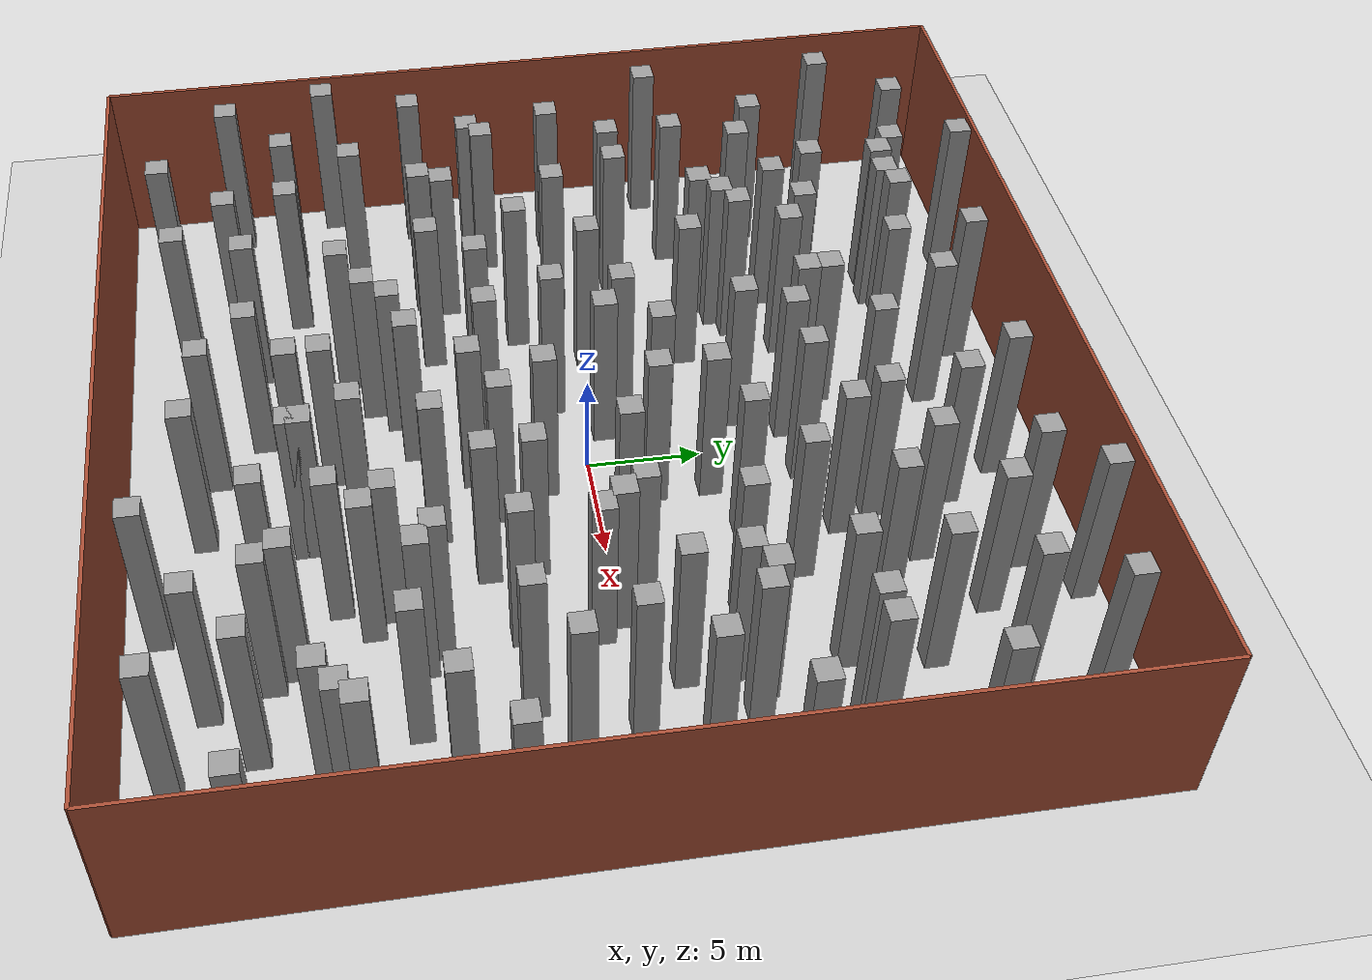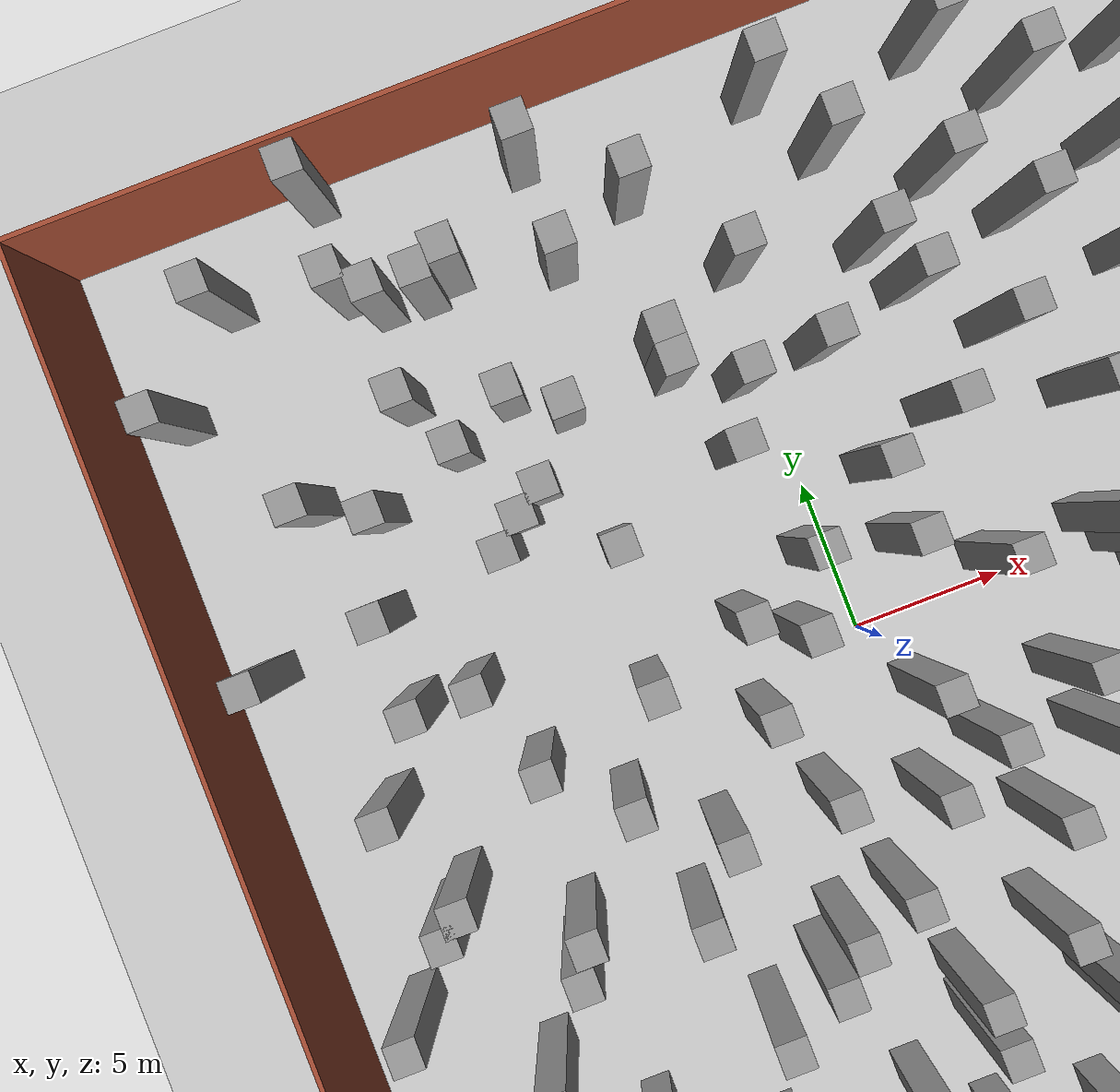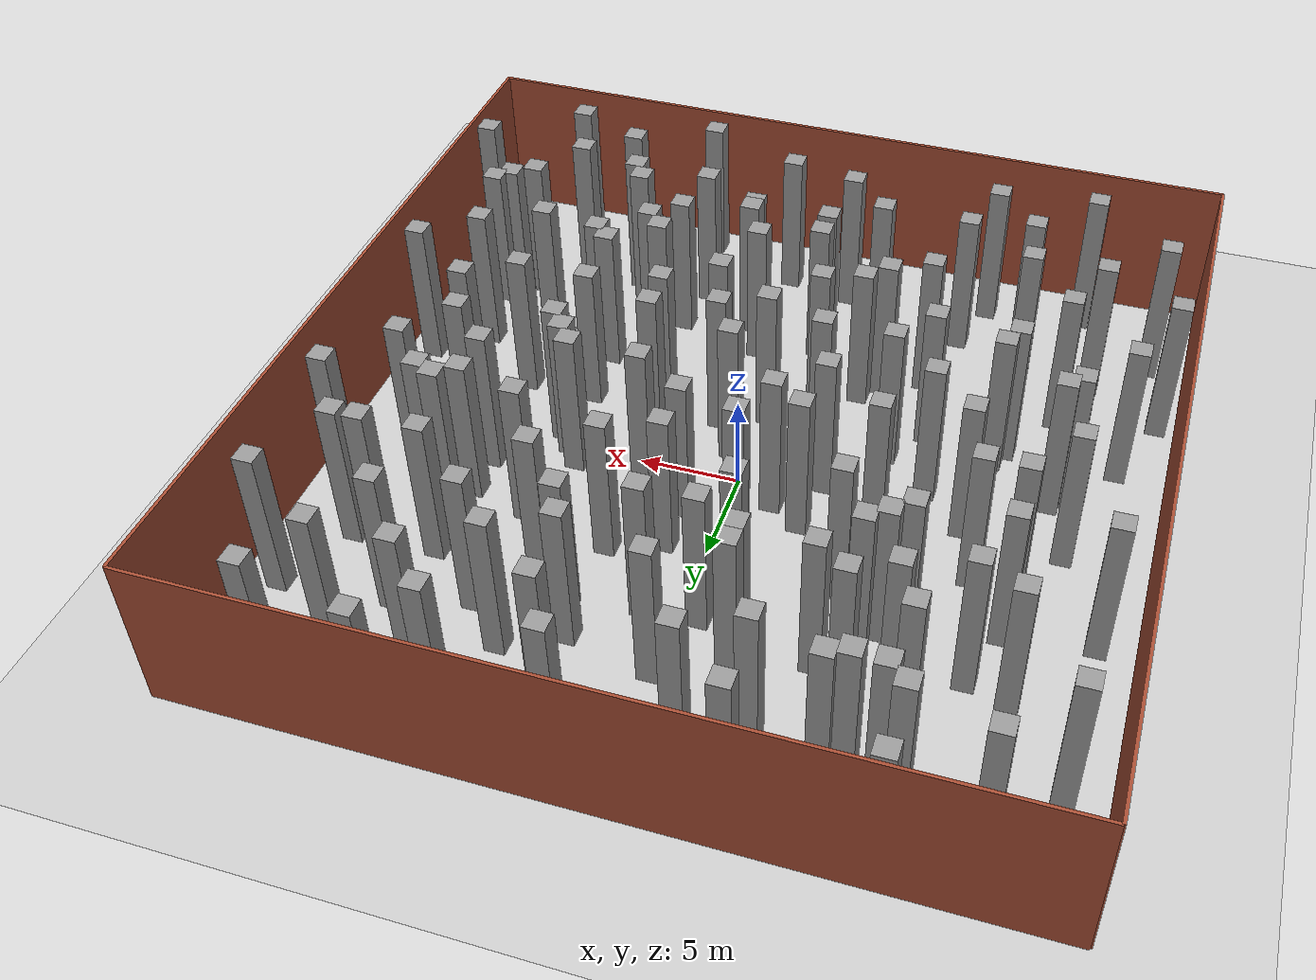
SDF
<sdf version="1.7">
 <world name="default">
  <light name="sun" type="directional">
   <pose>0 0 10 0 -0 0</pose>
   <diffuse>0.8 0.8 0.8 1</diffuse>
   <specular>0.2 0.2 0.2 1</specular>
   <attenuation>
    <range>1000</range>
    <constant>0.9</constant>
    <linear>0.01</linear>
    <quadratic>0.001</quadratic>
   </attenuation>
   <direction>-0.5 0.1 -0.9</direction>
   <spot><inner_angle>0</inner_angle><outer_angle>0</outer_angle><falloff>0</falloff></spot>
  </light>
  <model name="ground_plane">
   <static>1</static>
   <link name="link">
    <collision name="collision">
     <geometry><plane><normal>0 0 1</normal><size>100 100</size></plane></geometry>
     <surface>
      <contact><collide_bitmask>65535</collide_bitmask></contact>
      <friction><ode><mu>100</mu><mu2>50</mu2></ode></friction>
     </surface>
    </collision>
    <visual name="visual">
     <cast_shadows>0</cast_shadows>
     <geometry><plane><normal>0 0 1</normal><size>100 100</size></plane></geometry>
     <material>
      <script><uri>file://media/materials/scripts/gazebo.material</uri><name>Gazebo/Grey</name></script>
     </material>
    </visual>
   </link>
  </model>
  <gravity>0 0 -9.8</gravity>
  <magnetic_field>6e-06 2.3e-05 -4.2e-05</magnetic_field>
  <atmosphere type="adiabatic"/>
  <physics type="ode">
   <max_step_size>0.001</max_step_size>
   <real_time_factor>1</real_time_factor>
   <real_time_update_rate>1000</real_time_update_rate>
  </physics>
  <scene><ambient>0.4 0.4 0.4 1</ambient><background>0.7 0.7 0.7 1</background><shadows>1</shadows></scene>
  <spherical_coordinates>
   <surface_model>EARTH_WGS84</surface_model>
   <latitude_deg>0</latitude_deg>
   <longitude_deg>0</longitude_deg>
   <elevation>0</elevation>
   <heading_deg>0</heading_deg>
  </spherical_coordinates>
  <model name="sim_room_square">
   <link name="Wall_14">
    <collision name="Wall_14_Collision">
     <geometry><box><size>40 0.15 8</size></box></geometry>
     <pose>0 0 4 0 -0 0</pose>
    </collision>
    <visual name="Wall_14_Visual">
     <pose>0 0 4 0 -0 0</pose>
     <geometry><box><size>40 0.15 8</size></box></geometry>
     <material>
      <script><uri>file://media/materials/scripts/gazebo.material</uri><name>Gazebo/Bricks</name></script>
      <ambient>1 1 1 1</ambient>
     </material>
     <meta><layer>0</layer></meta>
    </visual>
    <pose>20 -0 0 0 -0 -1.5708</pose>
   </link>
   <link name="Wall_15">
    <collision name="Wall_15_Collision">
     <geometry><box><size>40 0.15 8</size></box></geometry>
     <pose>0 0 4 0 -0 0</pose>
    </collision>
    <visual name="Wall_15_Visual">
     <pose>0 0 4 0 -0 0</pose>
     <geometry><box><size>40 0.15 8</size></box></geometry>
     <material>
      <script><uri>file://media/materials/scripts/gazebo.material</uri><name>Gazebo/Bricks</name></script>
      <ambient>1 1 1 1</ambient>
     </material>
     <meta><layer>0</layer></meta>
    </visual>
    <pose>0 -20 0 0 -0 3.14159</pose>
   </link>
   <link name="Wall_16">
    <collision name="Wall_16_Collision">
     <geometry><box><size>40 0.15 8</size></box></geometry>
     <pose>0 0 4 0 -0 0</pose>
    </collision>
    <visual name="Wall_16_Visual">
     <pose>0 0 4 0 -0 0</pose>
     <geometry><box><size>40 0.15 8</size></box></geometry>
     <material>
      <script><uri>file://media/materials/scripts/gazebo.material</uri><name>Gazebo/Bricks</name></script>
      <ambient>1 1 1 1</ambient>
     </material>
     <meta><layer>0</layer></meta>
    </visual>
    <pose>-20 -0 0 0 -0 1.5708</pose>
   </link>
   <link name="Wall_19">
    <collision name="Wall_19_Collision">
     <geometry><box><size>40 0.15 8</size></box></geometry>
     <pose>0 0 4 0 -0 0</pose>
    </collision>
    <visual name="Wall_19_Visual">
     <pose>0 0 4 0 -0 0</pose>
     <geometry><box><size>40 0.15 8</size></box></geometry>
     <material>
      <script><uri>file://media/materials/scripts/gazebo.material</uri><name>Gazebo/Bricks</name></script>
      <ambient>1 1 1 1</ambient>
     </material>
     <meta><layer>0</layer></meta>
    </visual>
    <pose>0 20 0 0 -0 0</pose>
   </link>
   <static>1</static>
  </model>
  <model name="unit_box_static95">
   <link name="link">
    <inertial>
     <mass>1</mass>
     <inertia>
      <ixx>0.166667</ixx>
      <ixy>0</ixy>
      <ixz>0</ixz>
      <iyy>0.166667</iyy>
      <iyz>0</iyz>
      <izz>0.166667</izz>
     </inertia>
    </inertial>
    <visual name="visual">
     <geometry><box><size>1 1 8</size></box></geometry>
     <material>
      <script><name>Gazebo/Grey</name><uri>file://media/materials/scripts/gazebo.material</uri></script>
      <shader type="pixel"/>
     </material>
    </visual>
    <collision name="collision">
     <geometry><box><size>1 1 8</size></box></geometry>
     <surface>
      <friction>
       <ode><mu>1</mu><mu2>1</mu2><fdir1>0 0 0</fdir1><slip1>0</slip1><slip2>0</slip2></ode>
       <torsional>
        <coefficient>1</coefficient>
        <patch_radius>0</patch_radius>
        <surface_radius>0</surface_radius>
        <use_patch_radius>1</use_patch_radius>
        <ode><slip>0</slip></ode>
       </torsional>
      </friction>
      <bounce><restitution_coefficient>0</restitution_coefficient><threshold>1e+06</threshold></bounce>
      <contact>
       <collide_without_contact>0</collide_without_contact>
       <collide_without_contact_bitmask>1</collide_without_contact_bitmask>
       <collide_bitmask>1</collide_bitmask>
       <ode>
        <soft_cfm>0</soft_cfm>
        <soft_erp>0.2</soft_erp>
        <kp>1e+13</kp>
        <kd>1</kd>
        <max_vel>0.01</max_vel>
        <min_depth>0</min_depth>
       </ode>
       <bullet>
        <split_impulse>1</split_impulse>
        <split_impulse_penetration_threshold>-0.01</split_impulse_penetration_threshold>
        <soft_cfm>0</soft_cfm>
        <soft_erp>0.2</soft_erp>
        <kp>1e+13</kp>
        <kd>1</kd>
       </bullet>
      </contact>
     </surface>
    </collision>
   </link>
   <static>1</static>
   <pose>15.4272 17.8991 4 0 -0 0</pose>
  </model>
  <model name="unit_box_static95_clone">
   <link name="link">
    <inertial>
     <mass>1</mass>
     <inertia>
      <ixx>0.166667</ixx>
      <ixy>0</ixy>
      <ixz>0</ixz>
      <iyy>0.166667</iyy>
      <iyz>0</iyz>
      <izz>0.166667</izz>
     </inertia>
    </inertial>
    <visual name="visual">
     <geometry><box><size>1 1 8</size></box></geometry>
     <material>
      <script><name>Gazebo/Grey</name><uri>file://media/materials/scripts/gazebo.material</uri></script>
      <shader type="pixel"/>
     </material>
    </visual>
    <collision name="collision">
     <geometry><box><size>1 1 8</size></box></geometry>
     <surface>
      <friction>
       <ode><mu>1</mu><mu2>1</mu2><fdir1>0 0 0</fdir1><slip1>0</slip1><slip2>0</slip2></ode>
       <torsional>
        <coefficient>1</coefficient>
        <patch_radius>0</patch_radius>
        <surface_radius>0</surface_radius>
        <use_patch_radius>1</use_patch_radius>
        <ode><slip>0</slip></ode>
       </torsional>
      </friction>
      <bounce><restitution_coefficient>0</restitution_coefficient><threshold>1e+06</threshold></bounce>
      <contact>
       <collide_without_contact>0</collide_without_contact>
       <collide_without_contact_bitmask>1</collide_without_contact_bitmask>
       <collide_bitmask>1</collide_bitmask>
       <ode>
        <soft_cfm>0</soft_cfm>
        <soft_erp>0.2</soft_erp>
        <kp>1e+13</kp>
        <kd>1</kd>
        <max_vel>0.01</max_vel>
        <min_depth>0</min_depth>
       </ode>
       <bullet>
        <split_impulse>1</split_impulse>
        <split_impulse_penetration_threshold>-0.01</split_impulse_penetration_threshold>
        <soft_cfm>0</soft_cfm>
        <soft_erp>0.2</soft_erp>
        <kp>1e+13</kp>
        <kd>1</kd>
       </bullet>
      </contact>
     </surface>
    </collision>
   </link>
   <static>1</static>
   <pose>4.50167 1 4 0 -0 0</pose>
  </model>
  <model name="unit_box_static95_clone_0">
   <link name="link">
    <inertial>
     <mass>1</mass>
     <inertia>
      <ixx>0.166667</ixx>
      <ixy>0</ixy>
      <ixz>0</ixz>
      <iyy>0.166667</iyy>
      <iyz>0</iyz>
      <izz>0.166667</izz>
     </inertia>
    </inertial>
    <visual name="visual">
     <geometry><box><size>1 1 8</size></box></geometry>
     <material>
      <script><name>Gazebo/Grey</name><uri>file://media/materials/scripts/gazebo.material</uri></script>
      <shader type="pixel"/>
     </material>
    </visual>
    <collision name="collision">
     <geometry><box><size>1 1 8</size></box></geometry>
     <surface>
      <friction>
       <ode><mu>1</mu><mu2>1</mu2><fdir1>0 0 0</fdir1><slip1>0</slip1><slip2>0</slip2></ode>
       <torsional>
        <coefficient>1</coefficient>
        <patch_radius>0</patch_radius>
        <surface_radius>0</surface_radius>
        <use_patch_radius>1</use_patch_radius>
        <ode><slip>0</slip></ode>
       </torsional>
      </friction>
      <bounce><restitution_coefficient>0</restitution_coefficient><threshold>1e+06</threshold></bounce>
      <contact>
       <collide_without_contact>0</collide_without_contact>
       <collide_without_contact_bitmask>1</collide_without_contact_bitmask>
       <collide_bitmask>1</collide_bitmask>
       <ode>
        <soft_cfm>0</soft_cfm>
        <soft_erp>0.2</soft_erp>
        <kp>1e+13</kp>
        <kd>1</kd>
        <max_vel>0.01</max_vel>
        <min_depth>0</min_depth>
       </ode>
       <bullet>
        <split_impulse>1</split_impulse>
        <split_impulse_penetration_threshold>-0.01</split_impulse_penetration_threshold>
        <soft_cfm>0</soft_cfm>
        <soft_erp>0.2</soft_erp>
        <kp>1e+13</kp>
        <kd>1</kd>
       </bullet>
      </contact>
     </surface>
    </collision>
   </link>
   <static>1</static>
   <pose>5.40845 -3 4 0 -0 0</pose>
  </model>
  <model name="unit_box_static95_clone_1">
   <link name="link">
    <inertial>
     <mass>1</mass>
     <inertia>
      <ixx>0.166667</ixx>
      <ixy>0</ixy>
      <ixz>0</ixz>
      <iyy>0.166667</iyy>
      <iyz>0</iyz>
      <izz>0.166667</izz>
     </inertia>
    </inertial>
    <visual name="visual">
     <geometry><box><size>1 1 8</size></box></geometry>
     <material>
      <script><name>Gazebo/Grey</name><uri>file://media/materials/scripts/gazebo.material</uri></script>
      <shader type="pixel"/>
     </material>
    </visual>
    <collision name="collision">
     <geometry><box><size>1 1 8</size></box></geometry>
     <surface>
      <friction>
       <ode><mu>1</mu><mu2>1</mu2><fdir1>0 0 0</fdir1><slip1>0</slip1><slip2>0</slip2></ode>
       <torsional>
        <coefficient>1</coefficient>
        <patch_radius>0</patch_radius>
        <surface_radius>0</surface_radius>
        <use_patch_radius>1</use_patch_radius>
        <ode><slip>0</slip></ode>
       </torsional>
      </friction>
      <bounce><restitution_coefficient>0</restitution_coefficient><threshold>1e+06</threshold></bounce>
      <contact>
       <collide_without_contact>0</collide_without_contact>
       <collide_without_contact_bitmask>1</collide_without_contact_bitmask>
       <collide_bitmask>1</collide_bitmask>
       <ode>
        <soft_cfm>0</soft_cfm>
        <soft_erp>0.2</soft_erp>
        <kp>1e+13</kp>
        <kd>1</kd>
        <max_vel>0.01</max_vel>
        <min_depth>0</min_depth>
       </ode>
       <bullet>
        <split_impulse>1</split_impulse>
        <split_impulse_penetration_threshold>-0.01</split_impulse_penetration_threshold>
        <soft_cfm>0</soft_cfm>
        <soft_erp>0.2</soft_erp>
        <kp>1e+13</kp>
        <kd>1</kd>
       </bullet>
      </contact>
     </surface>
    </collision>
   </link>
   <static>1</static>
   <pose>5.51513 -5 4 0 -0 0</pose>
  </model>
  <model name="unit_box_static95_clone_2">
   <link name="link">
    <inertial>
     <mass>1</mass>
     <inertia>
      <ixx>0.166667</ixx>
      <ixy>0</ixy>
      <ixz>0</ixz>
      <iyy>0.166667</iyy>
      <iyz>0</iyz>
      <izz>0.166667</izz>
     </inertia>
    </inertial>
    <visual name="visual">
     <geometry><box><size>1 1 8</size></box></geometry>
     <material>
      <script><name>Gazebo/Grey</name><uri>file://media/materials/scripts/gazebo.material</uri></script>
      <shader type="pixel"/>
     </material>
    </visual>
    <collision name="collision">
     <geometry><box><size>1 1 8</size></box></geometry>
     <surface>
      <friction>
       <ode><mu>1</mu><mu2>1</mu2><fdir1>0 0 0</fdir1><slip1>0</slip1><slip2>0</slip2></ode>
       <torsional>
        <coefficient>1</coefficient>
        <patch_radius>0</patch_radius>
        <surface_radius>0</surface_radius>
        <use_patch_radius>1</use_patch_radius>
        <ode><slip>0</slip></ode>
       </torsional>
      </friction>
      <bounce><restitution_coefficient>0</restitution_coefficient><threshold>1e+06</threshold></bounce>
      <contact>
       <collide_without_contact>0</collide_without_contact>
       <collide_without_contact_bitmask>1</collide_without_contact_bitmask>
       <collide_bitmask>1</collide_bitmask>
       <ode>
        <soft_cfm>0</soft_cfm>
        <soft_erp>0.2</soft_erp>
        <kp>1e+13</kp>
        <kd>1</kd>
        <max_vel>0.01</max_vel>
        <min_depth>0</min_depth>
       </ode>
       <bullet>
        <split_impulse>1</split_impulse>
        <split_impulse_penetration_threshold>-0.01</split_impulse_penetration_threshold>
        <soft_cfm>0</soft_cfm>
        <soft_erp>0.2</soft_erp>
        <kp>1e+13</kp>
        <kd>1</kd>
       </bullet>
      </contact>
     </surface>
    </collision>
   </link>
   <static>1</static>
   <pose>2.2148 -4 4 0 -0 0</pose>
  </model>
  <model name="unit_box_static95_clone_3">
   <link name="link">
    <inertial>
     <mass>1</mass>
     <inertia>
      <ixx>0.166667</ixx>
      <ixy>0</ixy>
      <ixz>0</ixz>
      <iyy>0.166667</iyy>
      <iyz>0</iyz>
      <izz>0.166667</izz>
     </inertia>
    </inertial>
    <visual name="visual">
     <geometry><box><size>1 1 8</size></box></geometry>
     <material>
      <script><name>Gazebo/Grey</name><uri>file://media/materials/scripts/gazebo.material</uri></script>
      <shader type="pixel"/>
     </material>
    </visual>
    <collision name="collision">
     <geometry><box><size>1 1 8</size></box></geometry>
     <surface>
      <friction>
       <ode><mu>1</mu><mu2>1</mu2><fdir1>0 0 0</fdir1><slip1>0</slip1><slip2>0</slip2></ode>
       <torsional>
        <coefficient>1</coefficient>
        <patch_radius>0</patch_radius>
        <surface_radius>0</surface_radius>
        <use_patch_radius>1</use_patch_radius>
        <ode><slip>0</slip></ode>
       </torsional>
      </friction>
      <bounce><restitution_coefficient>0</restitution_coefficient><threshold>1e+06</threshold></bounce>
      <contact>
       <collide_without_contact>0</collide_without_contact>
       <collide_without_contact_bitmask>1</collide_without_contact_bitmask>
       <collide_bitmask>1</collide_bitmask>
       <ode>
        <soft_cfm>0</soft_cfm>
        <soft_erp>0.2</soft_erp>
        <kp>1e+13</kp>
        <kd>1</kd>
        <max_vel>0.01</max_vel>
        <min_depth>0</min_depth>
       </ode>
       <bullet>
        <split_impulse>1</split_impulse>
        <split_impulse_penetration_threshold>-0.01</split_impulse_penetration_threshold>
        <soft_cfm>0</soft_cfm>
        <soft_erp>0.2</soft_erp>
        <kp>1e+13</kp>
        <kd>1</kd>
       </bullet>
      </contact>
     </surface>
    </collision>
   </link>
   <static>1</static>
   <pose>0 -5 4 0 -0 0</pose>
  </model>
  <model name="unit_box_static95_clone_4">
   <link name="link">
    <inertial>
     <mass>1</mass>
     <inertia>
      <ixx>0.166667</ixx>
      <ixy>0</ixy>
      <ixz>0</ixz>
      <iyy>0.166667</iyy>
      <iyz>0</iyz>
      <izz>0.166667</izz>
     </inertia>
    </inertial>
    <visual name="visual">
     <geometry><box><size>1 1 8</size></box></geometry>
     <material>
      <script><name>Gazebo/Grey</name><uri>file://media/materials/scripts/gazebo.material</uri></script>
      <shader type="pixel"/>
     </material>
    </visual>
    <collision name="collision">
     <geometry><box><size>1 1 8</size></box></geometry>
     <surface>
      <friction>
       <ode><mu>1</mu><mu2>1</mu2><fdir1>0 0 0</fdir1><slip1>0</slip1><slip2>0</slip2></ode>
       <torsional>
        <coefficient>1</coefficient>
        <patch_radius>0</patch_radius>
        <surface_radius>0</surface_radius>
        <use_patch_radius>1</use_patch_radius>
        <ode><slip>0</slip></ode>
       </torsional>
      </friction>
      <bounce><restitution_coefficient>0</restitution_coefficient><threshold>1e+06</threshold></bounce>
      <contact>
       <collide_without_contact>0</collide_without_contact>
       <collide_without_contact_bitmask>1</collide_without_contact_bitmask>
       <collide_bitmask>1</collide_bitmask>
       <ode>
        <soft_cfm>0</soft_cfm>
        <soft_erp>0.2</soft_erp>
        <kp>1e+13</kp>
        <kd>1</kd>
        <max_vel>0.01</max_vel>
        <min_depth>0</min_depth>
       </ode>
       <bullet>
        <split_impulse>1</split_impulse>
        <split_impulse_penetration_threshold>-0.01</split_impulse_penetration_threshold>
        <soft_cfm>0</soft_cfm>
        <soft_erp>0.2</soft_erp>
        <kp>1e+13</kp>
        <kd>1</kd>
       </bullet>
      </contact>
     </surface>
    </collision>
   </link>
   <static>1</static>
   <pose>-3 -4 4 0 -0 0</pose>
  </model>
  <model name="unit_box_static95_clone_5">
   <link name="link">
    <inertial>
     <mass>1</mass>
     <inertia>
      <ixx>0.166667</ixx>
      <ixy>0</ixy>
      <ixz>0</ixz>
      <iyy>0.166667</iyy>
      <iyz>0</iyz>
      <izz>0.166667</izz>
     </inertia>
    </inertial>
    <visual name="visual">
     <geometry><box><size>1 1 8</size></box></geometry>
     <material>
      <script><name>Gazebo/Grey</name><uri>file://media/materials/scripts/gazebo.material</uri></script>
      <shader type="pixel"/>
     </material>
    </visual>
    <collision name="collision">
     <geometry><box><size>1 1 8</size></box></geometry>
     <surface>
      <friction>
       <ode><mu>1</mu><mu2>1</mu2><fdir1>0 0 0</fdir1><slip1>0</slip1><slip2>0</slip2></ode>
       <torsional>
        <coefficient>1</coefficient>
        <patch_radius>0</patch_radius>
        <surface_radius>0</surface_radius>
        <use_patch_radius>1</use_patch_radius>
        <ode><slip>0</slip></ode>
       </torsional>
      </friction>
      <bounce><restitution_coefficient>0</restitution_coefficient><threshold>1e+06</threshold></bounce>
      <contact>
       <collide_without_contact>0</collide_without_contact>
       <collide_without_contact_bitmask>1</collide_without_contact_bitmask>
       <collide_bitmask>1</collide_bitmask>
       <ode>
        <soft_cfm>0</soft_cfm>
        <soft_erp>0.2</soft_erp>
        <kp>1e+13</kp>
        <kd>1</kd>
        <max_vel>0.01</max_vel>
        <min_depth>0</min_depth>
       </ode>
       <bullet>
        <split_impulse>1</split_impulse>
        <split_impulse_penetration_threshold>-0.01</split_impulse_penetration_threshold>
        <soft_cfm>0</soft_cfm>
        <soft_erp>0.2</soft_erp>
        <kp>1e+13</kp>
        <kd>1</kd>
       </bullet>
      </contact>
     </surface>
    </collision>
   </link>
   <static>1</static>
   <pose>-4 -1 4 0 -0 0</pose>
  </model>
  <model name="unit_box_static95_clone_6">
   <link name="link">
    <inertial>
     <mass>1</mass>
     <inertia>
      <ixx>0.166667</ixx>
      <ixy>0</ixy>
      <ixz>0</ixz>
      <iyy>0.166667</iyy>
      <iyz>0</iyz>
      <izz>0.166667</izz>
     </inertia>
    </inertial>
    <visual name="visual">
     <geometry><box><size>1 1 8</size></box></geometry>
     <material>
      <script><name>Gazebo/Grey</name><uri>file://media/materials/scripts/gazebo.material</uri></script>
      <shader type="pixel"/>
     </material>
    </visual>
    <collision name="collision">
     <geometry><box><size>1 1 8</size></box></geometry>
     <surface>
      <friction>
       <ode><mu>1</mu><mu2>1</mu2><fdir1>0 0 0</fdir1><slip1>0</slip1><slip2>0</slip2></ode>
       <torsional>
        <coefficient>1</coefficient>
        <patch_radius>0</patch_radius>
        <surface_radius>0</surface_radius>
        <use_patch_radius>1</use_patch_radius>
        <ode><slip>0</slip></ode>
       </torsional>
      </friction>
      <bounce><restitution_coefficient>0</restitution_coefficient><threshold>1e+06</threshold></bounce>
      <contact>
       <collide_without_contact>0</collide_without_contact>
       <collide_without_contact_bitmask>1</collide_without_contact_bitmask>
       <collide_bitmask>1</collide_bitmask>
       <ode>
        <soft_cfm>0</soft_cfm>
        <soft_erp>0.2</soft_erp>
        <kp>1e+13</kp>
        <kd>1</kd>
        <max_vel>0.01</max_vel>
        <min_depth>0</min_depth>
       </ode>
       <bullet>
        <split_impulse>1</split_impulse>
        <split_impulse_penetration_threshold>-0.01</split_impulse_penetration_threshold>
        <soft_cfm>0</soft_cfm>
        <soft_erp>0.2</soft_erp>
        <kp>1e+13</kp>
        <kd>1</kd>
       </bullet>
      </contact>
     </surface>
    </collision>
   </link>
   <static>1</static>
   <pose>-6.45206 -4 4 0 -0 0</pose>
  </model>
  <model name="unit_box_static95_clone_7">
   <link name="link">
    <inertial>
     <mass>1</mass>
     <inertia>
      <ixx>0.166667</ixx>
      <ixy>0</ixy>
      <ixz>0</ixz>
      <iyy>0.166667</iyy>
      <iyz>0</iyz>
      <izz>0.166667</izz>
     </inertia>
    </inertial>
    <visual name="visual">
     <geometry><box><size>1 1 8</size></box></geometry>
     <material>
      <script><name>Gazebo/Grey</name><uri>file://media/materials/scripts/gazebo.material</uri></script>
      <shader type="pixel"/>
     </material>
    </visual>
    <collision name="collision">
     <geometry><box><size>1 1 8</size></box></geometry>
     <surface>
      <friction>
       <ode><mu>1</mu><mu2>1</mu2><fdir1>0 0 0</fdir1><slip1>0</slip1><slip2>0</slip2></ode>
       <torsional>
        <coefficient>1</coefficient>
        <patch_radius>0</patch_radius>
        <surface_radius>0</surface_radius>
        <use_patch_radius>1</use_patch_radius>
        <ode><slip>0</slip></ode>
       </torsional>
      </friction>
      <bounce><restitution_coefficient>0</restitution_coefficient><threshold>1e+06</threshold></bounce>
      <contact>
       <collide_without_contact>0</collide_without_contact>
       <collide_without_contact_bitmask>1</collide_without_contact_bitmask>
       <collide_bitmask>1</collide_bitmask>
       <ode>
        <soft_cfm>0</soft_cfm>
        <soft_erp>0.2</soft_erp>
        <kp>1e+13</kp>
        <kd>1</kd>
        <max_vel>0.01</max_vel>
        <min_depth>0</min_depth>
       </ode>
       <bullet>
        <split_impulse>1</split_impulse>
        <split_impulse_penetration_threshold>-0.01</split_impulse_penetration_threshold>
        <soft_cfm>0</soft_cfm>
        <soft_erp>0.2</soft_erp>
        <kp>1e+13</kp>
        <kd>1</kd>
       </bullet>
      </contact>
     </surface>
    </collision>
   </link>
   <static>1</static>
   <pose>-7 -10 4 0 -0 0</pose>
  </model>
  <model name="unit_box_static95_clone_8">
   <link name="link">
    <inertial>
     <mass>1</mass>
     <inertia>
      <ixx>0.166667</ixx>
      <ixy>0</ixy>
      <ixz>0</ixz>
      <iyy>0.166667</iyy>
      <iyz>0</iyz>
      <izz>0.166667</izz>
     </inertia>
    </inertial>
    <visual name="visual">
     <geometry><box><size>1 1 8</size></box></geometry>
     <material>
      <script><name>Gazebo/Grey</name><uri>file://media/materials/scripts/gazebo.material</uri></script>
      <shader type="pixel"/>
     </material>
    </visual>
    <collision name="collision">
     <geometry><box><size>1 1 8</size></box></geometry>
     <surface>
      <friction>
       <ode><mu>1</mu><mu2>1</mu2><fdir1>0 0 0</fdir1><slip1>0</slip1><slip2>0</slip2></ode>
       <torsional>
        <coefficient>1</coefficient>
        <patch_radius>0</patch_radius>
        <surface_radius>0</surface_radius>
        <use_patch_radius>1</use_patch_radius>
        <ode><slip>0</slip></ode>
       </torsional>
      </friction>
      <bounce><restitution_coefficient>0</restitution_coefficient><threshold>1e+06</threshold></bounce>
      <contact>
       <collide_without_contact>0</collide_without_contact>
       <collide_without_contact_bitmask>1</collide_without_contact_bitmask>
       <collide_bitmask>1</collide_bitmask>
       <ode>
        <soft_cfm>0</soft_cfm>
        <soft_erp>0.2</soft_erp>
        <kp>1e+13</kp>
        <kd>1</kd>
        <max_vel>0.01</max_vel>
        <min_depth>0</min_depth>
       </ode>
       <bullet>
        <split_impulse>1</split_impulse>
        <split_impulse_penetration_threshold>-0.01</split_impulse_penetration_threshold>
        <soft_cfm>0</soft_cfm>
        <soft_erp>0.2</soft_erp>
        <kp>1e+13</kp>
        <kd>1</kd>
       </bullet>
      </contact>
     </surface>
    </collision>
   </link>
   <static>1</static>
   <pose>-9 -17 4 0 -0 0</pose>
  </model>
  <model name="unit_box_static95_clone_9">
   <link name="link">
    <inertial>
     <mass>1</mass>
     <inertia>
      <ixx>0.166667</ixx>
      <ixy>0</ixy>
      <ixz>0</ixz>
      <iyy>0.166667</iyy>
      <iyz>0</iyz>
      <izz>0.166667</izz>
     </inertia>
    </inertial>
    <visual name="visual">
     <geometry><box><size>1 1 8</size></box></geometry>
     <material>
      <script><name>Gazebo/Grey</name><uri>file://media/materials/scripts/gazebo.material</uri></script>
      <shader type="pixel"/>
     </material>
    </visual>
    <collision name="collision">
     <geometry><box><size>1 1 8</size></box></geometry>
     <surface>
      <friction>
       <ode><mu>1</mu><mu2>1</mu2><fdir1>0 0 0</fdir1><slip1>0</slip1><slip2>0</slip2></ode>
       <torsional>
        <coefficient>1</coefficient>
        <patch_radius>0</patch_radius>
        <surface_radius>0</surface_radius>
        <use_patch_radius>1</use_patch_radius>
        <ode><slip>0</slip></ode>
       </torsional>
      </friction>
      <bounce><restitution_coefficient>0</restitution_coefficient><threshold>1e+06</threshold></bounce>
      <contact>
       <collide_without_contact>0</collide_without_contact>
       <collide_without_contact_bitmask>1</collide_without_contact_bitmask>
       <collide_bitmask>1</collide_bitmask>
       <ode>
        <soft_cfm>0</soft_cfm>
        <soft_erp>0.2</soft_erp>
        <kp>1e+13</kp>
        <kd>1</kd>
        <max_vel>0.01</max_vel>
        <min_depth>0</min_depth>
       </ode>
       <bullet>
        <split_impulse>1</split_impulse>
        <split_impulse_penetration_threshold>-0.01</split_impulse_penetration_threshold>
        <soft_cfm>0</soft_cfm>
        <soft_erp>0.2</soft_erp>
        <kp>1e+13</kp>
        <kd>1</kd>
       </bullet>
      </contact>
     </surface>
    </collision>
   </link>
   <static>1</static>
   <pose>-11.5727 -12 4 0 -0 0</pose>
  </model>
  <model name="unit_box_static95_clone_10">
   <link name="link">
    <inertial>
     <mass>1</mass>
     <inertia>
      <ixx>0.166667</ixx>
      <ixy>0</ixy>
      <ixz>0</ixz>
      <iyy>0.166667</iyy>
      <iyz>0</iyz>
      <izz>0.166667</izz>
     </inertia>
    </inertial>
    <visual name="visual">
     <geometry><box><size>1 1 8</size></box></geometry>
     <material>
      <script><name>Gazebo/Grey</name><uri>file://media/materials/scripts/gazebo.material</uri></script>
      <shader type="pixel"/>
     </material>
    </visual>
    <collision name="collision">
     <geometry><box><size>1 1 8</size></box></geometry>
     <surface>
      <friction>
       <ode><mu>1</mu><mu2>1</mu2><fdir1>0 0 0</fdir1><slip1>0</slip1><slip2>0</slip2></ode>
       <torsional>
        <coefficient>1</coefficient>
        <patch_radius>0</patch_radius>
        <surface_radius>0</surface_radius>
        <use_patch_radius>1</use_patch_radius>
        <ode><slip>0</slip></ode>
       </torsional>
      </friction>
      <bounce><restitution_coefficient>0</restitution_coefficient><threshold>1e+06</threshold></bounce>
      <contact>
       <collide_without_contact>0</collide_without_contact>
       <collide_without_contact_bitmask>1</collide_without_contact_bitmask>
       <collide_bitmask>1</collide_bitmask>
       <ode>
        <soft_cfm>0</soft_cfm>
        <soft_erp>0.2</soft_erp>
        <kp>1e+13</kp>
        <kd>1</kd>
        <max_vel>0.01</max_vel>
        <min_depth>0</min_depth>
       </ode>
       <bullet>
        <split_impulse>1</split_impulse>
        <split_impulse_penetration_threshold>-0.01</split_impulse_penetration_threshold>
        <soft_cfm>0</soft_cfm>
        <soft_erp>0.2</soft_erp>
        <kp>1e+13</kp>
        <kd>1</kd>
       </bullet>
      </contact>
     </surface>
    </collision>
   </link>
   <static>1</static>
   <pose>-12 -6 4 0 -0 0</pose>
  </model>
  <model name="unit_box_static95_clone_11">
   <link name="link">
    <inertial>
     <mass>1</mass>
     <inertia>
      <ixx>0.166667</ixx>
      <ixy>0</ixy>
      <ixz>0</ixz>
      <iyy>0.166667</iyy>
      <iyz>0</iyz>
      <izz>0.166667</izz>
     </inertia>
    </inertial>
    <visual name="visual">
     <geometry><box><size>1 1 8</size></box></geometry>
     <material>
      <script><name>Gazebo/Grey</name><uri>file://media/materials/scripts/gazebo.material</uri></script>
      <shader type="pixel"/>
     </material>
    </visual>
    <collision name="collision">
     <geometry><box><size>1 1 8</size></box></geometry>
     <surface>
      <friction>
       <ode><mu>1</mu><mu2>1</mu2><fdir1>0 0 0</fdir1><slip1>0</slip1><slip2>0</slip2></ode>
       <torsional>
        <coefficient>1</coefficient>
        <patch_radius>0</patch_radius>
        <surface_radius>0</surface_radius>
        <use_patch_radius>1</use_patch_radius>
        <ode><slip>0</slip></ode>
       </torsional>
      </friction>
      <bounce><restitution_coefficient>0</restitution_coefficient><threshold>1e+06</threshold></bounce>
      <contact>
       <collide_without_contact>0</collide_without_contact>
       <collide_without_contact_bitmask>1</collide_without_contact_bitmask>
       <collide_bitmask>1</collide_bitmask>
       <ode>
        <soft_cfm>0</soft_cfm>
        <soft_erp>0.2</soft_erp>
        <kp>1e+13</kp>
        <kd>1</kd>
        <max_vel>0.01</max_vel>
        <min_depth>0</min_depth>
       </ode>
       <bullet>
        <split_impulse>1</split_impulse>
        <split_impulse_penetration_threshold>-0.01</split_impulse_penetration_threshold>
        <soft_cfm>0</soft_cfm>
        <soft_erp>0.2</soft_erp>
        <kp>1e+13</kp>
        <kd>1</kd>
       </bullet>
      </contact>
     </surface>
    </collision>
   </link>
   <static>1</static>
   <pose>-14 3 4 0 -0 0</pose>
  </model>
  <model name="unit_box_static95_clone_12">
   <link name="link">
    <inertial>
     <mass>1</mass>
     <inertia>
      <ixx>0.166667</ixx>
      <ixy>0</ixy>
      <ixz>0</ixz>
      <iyy>0.166667</iyy>
      <iyz>0</iyz>
      <izz>0.166667</izz>
     </inertia>
    </inertial>
    <visual name="visual">
     <geometry><box><size>1 1 8</size></box></geometry>
     <material>
      <script><name>Gazebo/Grey</name><uri>file://media/materials/scripts/gazebo.material</uri></script>
      <shader type="pixel"/>
     </material>
    </visual>
    <collision name="collision">
     <geometry><box><size>1 1 8</size></box></geometry>
     <surface>
      <friction>
       <ode><mu>1</mu><mu2>1</mu2><fdir1>0 0 0</fdir1><slip1>0</slip1><slip2>0</slip2></ode>
       <torsional>
        <coefficient>1</coefficient>
        <patch_radius>0</patch_radius>
        <surface_radius>0</surface_radius>
        <use_patch_radius>1</use_patch_radius>
        <ode><slip>0</slip></ode>
       </torsional>
      </friction>
      <bounce><restitution_coefficient>0</restitution_coefficient><threshold>1e+06</threshold></bounce>
      <contact>
       <collide_without_contact>0</collide_without_contact>
       <collide_without_contact_bitmask>1</collide_without_contact_bitmask>
       <collide_bitmask>1</collide_bitmask>
       <ode>
        <soft_cfm>0</soft_cfm>
        <soft_erp>0.2</soft_erp>
        <kp>1e+13</kp>
        <kd>1</kd>
        <max_vel>0.01</max_vel>
        <min_depth>0</min_depth>
       </ode>
       <bullet>
        <split_impulse>1</split_impulse>
        <split_impulse_penetration_threshold>-0.01</split_impulse_penetration_threshold>
        <soft_cfm>0</soft_cfm>
        <soft_erp>0.2</soft_erp>
        <kp>1e+13</kp>
        <kd>1</kd>
       </bullet>
      </contact>
     </surface>
    </collision>
   </link>
   <static>1</static>
   <pose>-15 10 4 0 -0 0</pose>
  </model>
  <model name="unit_box_static95_clone_13">
   <link name="link">
    <inertial>
     <mass>1</mass>
     <inertia>
      <ixx>0.166667</ixx>
      <ixy>0</ixy>
      <ixz>0</ixz>
      <iyy>0.166667</iyy>
      <iyz>0</iyz>
      <izz>0.166667</izz>
     </inertia>
    </inertial>
    <visual name="visual">
     <geometry><box><size>1 1 8</size></box></geometry>
     <material>
      <script><name>Gazebo/Grey</name><uri>file://media/materials/scripts/gazebo.material</uri></script>
      <shader type="pixel"/>
     </material>
    </visual>
    <collision name="collision">
     <geometry><box><size>1 1 8</size></box></geometry>
     <surface>
      <friction>
       <ode><mu>1</mu><mu2>1</mu2><fdir1>0 0 0</fdir1><slip1>0</slip1><slip2>0</slip2></ode>
       <torsional>
        <coefficient>1</coefficient>
        <patch_radius>0</patch_radius>
        <surface_radius>0</surface_radius>
        <use_patch_radius>1</use_patch_radius>
        <ode><slip>0</slip></ode>
       </torsional>
      </friction>
      <bounce><restitution_coefficient>0</restitution_coefficient><threshold>1e+06</threshold></bounce>
      <contact>
       <collide_without_contact>0</collide_without_contact>
       <collide_without_contact_bitmask>1</collide_without_contact_bitmask>
       <collide_bitmask>1</collide_bitmask>
       <ode>
        <soft_cfm>0</soft_cfm>
        <soft_erp>0.2</soft_erp>
        <kp>1e+13</kp>
        <kd>1</kd>
        <max_vel>0.01</max_vel>
        <min_depth>0</min_depth>
       </ode>
       <bullet>
        <split_impulse>1</split_impulse>
        <split_impulse_penetration_threshold>-0.01</split_impulse_penetration_threshold>
        <soft_cfm>0</soft_cfm>
        <soft_erp>0.2</soft_erp>
        <kp>1e+13</kp>
        <kd>1</kd>
       </bullet>
      </contact>
     </surface>
    </collision>
   </link>
   <static>1</static>
   <pose>-11 12 4 0 -0 0</pose>
  </model>
  <model name="unit_box_static95_clone_14">
   <link name="link">
    <inertial>
     <mass>1</mass>
     <inertia>
      <ixx>0.166667</ixx>
      <ixy>0</ixy>
      <ixz>0</ixz>
      <iyy>0.166667</iyy>
      <iyz>0</iyz>
      <izz>0.166667</izz>
     </inertia>
    </inertial>
    <visual name="visual">
     <geometry><box><size>1 1 8</size></box></geometry>
     <material>
      <script><name>Gazebo/Grey</name><uri>file://media/materials/scripts/gazebo.material</uri></script>
      <shader type="pixel"/>
     </material>
    </visual>
    <collision name="collision">
     <geometry><box><size>1 1 8</size></box></geometry>
     <surface>
      <friction>
       <ode><mu>1</mu><mu2>1</mu2><fdir1>0 0 0</fdir1><slip1>0</slip1><slip2>0</slip2></ode>
       <torsional>
        <coefficient>1</coefficient>
        <patch_radius>0</patch_radius>
        <surface_radius>0</surface_radius>
        <use_patch_radius>1</use_patch_radius>
        <ode><slip>0</slip></ode>
       </torsional>
      </friction>
      <bounce><restitution_coefficient>0</restitution_coefficient><threshold>1e+06</threshold></bounce>
      <contact>
       <collide_without_contact>0</collide_without_contact>
       <collide_without_contact_bitmask>1</collide_without_contact_bitmask>
       <collide_bitmask>1</collide_bitmask>
       <ode>
        <soft_cfm>0</soft_cfm>
        <soft_erp>0.2</soft_erp>
        <kp>1e+13</kp>
        <kd>1</kd>
        <max_vel>0.01</max_vel>
        <min_depth>0</min_depth>
       </ode>
       <bullet>
        <split_impulse>1</split_impulse>
        <split_impulse_penetration_threshold>-0.01</split_impulse_penetration_threshold>
        <soft_cfm>0</soft_cfm>
        <soft_erp>0.2</soft_erp>
        <kp>1e+13</kp>
        <kd>1</kd>
       </bullet>
      </contact>
     </surface>
    </collision>
   </link>
   <static>1</static>
   <pose>-8 11 4 0 -0 0</pose>
  </model>
  <model name="unit_box_static95_clone_15">
   <link name="link">
    <inertial>
     <mass>1</mass>
     <inertia>
      <ixx>0.166667</ixx>
      <ixy>0</ixy>
      <ixz>0</ixz>
      <iyy>0.166667</iyy>
      <iyz>0</iyz>
      <izz>0.166667</izz>
     </inertia>
    </inertial>
    <visual name="visual">
     <geometry><box><size>1 1 8</size></box></geometry>
     <material>
      <script><name>Gazebo/Grey</name><uri>file://media/materials/scripts/gazebo.material</uri></script>
      <shader type="pixel"/>
     </material>
    </visual>
    <collision name="collision">
     <geometry><box><size>1 1 8</size></box></geometry>
     <surface>
      <friction>
       <ode><mu>1</mu><mu2>1</mu2><fdir1>0 0 0</fdir1><slip1>0</slip1><slip2>0</slip2></ode>
       <torsional>
        <coefficient>1</coefficient>
        <patch_radius>0</patch_radius>
        <surface_radius>0</surface_radius>
        <use_patch_radius>1</use_patch_radius>
        <ode><slip>0</slip></ode>
       </torsional>
      </friction>
      <bounce><restitution_coefficient>0</restitution_coefficient><threshold>1e+06</threshold></bounce>
      <contact>
       <collide_without_contact>0</collide_without_contact>
       <collide_without_contact_bitmask>1</collide_without_contact_bitmask>
       <collide_bitmask>1</collide_bitmask>
       <ode>
        <soft_cfm>0</soft_cfm>
        <soft_erp>0.2</soft_erp>
        <kp>1e+13</kp>
        <kd>1</kd>
        <max_vel>0.01</max_vel>
        <min_depth>0</min_depth>
       </ode>
       <bullet>
        <split_impulse>1</split_impulse>
        <split_impulse_penetration_threshold>-0.01</split_impulse_penetration_threshold>
        <soft_cfm>0</soft_cfm>
        <soft_erp>0.2</soft_erp>
        <kp>1e+13</kp>
        <kd>1</kd>
       </bullet>
      </contact>
     </surface>
    </collision>
   </link>
   <static>1</static>
   <pose>-6.4408 5.4534 4 0 -0 0</pose>
  </model>
  <model name="unit_box_static95_clone_16">
   <link name="link">
    <inertial>
     <mass>1</mass>
     <inertia>
      <ixx>0.166667</ixx>
      <ixy>0</ixy>
      <ixz>0</ixz>
      <iyy>0.166667</iyy>
      <iyz>0</iyz>
      <izz>0.166667</izz>
     </inertia>
    </inertial>
    <visual name="visual">
     <geometry><box><size>1 1 8</size></box></geometry>
     <material>
      <script><name>Gazebo/Grey</name><uri>file://media/materials/scripts/gazebo.material</uri></script>
      <shader type="pixel"/>
     </material>
    </visual>
    <collision name="collision">
     <geometry><box><size>1 1 8</size></box></geometry>
     <surface>
      <friction>
       <ode><mu>1</mu><mu2>1</mu2><fdir1>0 0 0</fdir1><slip1>0</slip1><slip2>0</slip2></ode>
       <torsional>
        <coefficient>1</coefficient>
        <patch_radius>0</patch_radius>
        <surface_radius>0</surface_radius>
        <use_patch_radius>1</use_patch_radius>
        <ode><slip>0</slip></ode>
       </torsional>
      </friction>
      <bounce><restitution_coefficient>0</restitution_coefficient><threshold>1e+06</threshold></bounce>
      <contact>
       <collide_without_contact>0</collide_without_contact>
       <collide_without_contact_bitmask>1</collide_without_contact_bitmask>
       <collide_bitmask>1</collide_bitmask>
       <ode>
        <soft_cfm>0</soft_cfm>
        <soft_erp>0.2</soft_erp>
        <kp>1e+13</kp>
        <kd>1</kd>
        <max_vel>0.01</max_vel>
        <min_depth>0</min_depth>
       </ode>
       <bullet>
        <split_impulse>1</split_impulse>
        <split_impulse_penetration_threshold>-0.01</split_impulse_penetration_threshold>
        <soft_cfm>0</soft_cfm>
        <soft_erp>0.2</soft_erp>
        <kp>1e+13</kp>
        <kd>1</kd>
       </bullet>
      </contact>
     </surface>
    </collision>
   </link>
   <static>1</static>
   <pose>-2 7 4 0 -0 0</pose>
  </model>
  <model name="unit_box_static95_clone_17">
   <link name="link">
    <inertial>
     <mass>1</mass>
     <inertia>
      <ixx>0.166667</ixx>
      <ixy>0</ixy>
      <ixz>0</ixz>
      <iyy>0.166667</iyy>
      <iyz>0</iyz>
      <izz>0.166667</izz>
     </inertia>
    </inertial>
    <visual name="visual">
     <geometry><box><size>1 1 8</size></box></geometry>
     <material>
      <script><name>Gazebo/Grey</name><uri>file://media/materials/scripts/gazebo.material</uri></script>
      <shader type="pixel"/>
     </material>
    </visual>
    <collision name="collision">
     <geometry><box><size>1 1 8</size></box></geometry>
     <surface>
      <friction>
       <ode><mu>1</mu><mu2>1</mu2><fdir1>0 0 0</fdir1><slip1>0</slip1><slip2>0</slip2></ode>
       <torsional>
        <coefficient>1</coefficient>
        <patch_radius>0</patch_radius>
        <surface_radius>0</surface_radius>
        <use_patch_radius>1</use_patch_radius>
        <ode><slip>0</slip></ode>
       </torsional>
      </friction>
      <bounce><restitution_coefficient>0</restitution_coefficient><threshold>1e+06</threshold></bounce>
      <contact>
       <collide_without_contact>0</collide_without_contact>
       <collide_without_contact_bitmask>1</collide_without_contact_bitmask>
       <collide_bitmask>1</collide_bitmask>
       <ode>
        <soft_cfm>0</soft_cfm>
        <soft_erp>0.2</soft_erp>
        <kp>1e+13</kp>
        <kd>1</kd>
        <max_vel>0.01</max_vel>
        <min_depth>0</min_depth>
       </ode>
       <bullet>
        <split_impulse>1</split_impulse>
        <split_impulse_penetration_threshold>-0.01</split_impulse_penetration_threshold>
        <soft_cfm>0</soft_cfm>
        <soft_erp>0.2</soft_erp>
        <kp>1e+13</kp>
        <kd>1</kd>
       </bullet>
      </contact>
     </surface>
    </collision>
   </link>
   <static>1</static>
   <pose>-3 11 4 0 -0 0</pose>
  </model>
  <model name="unit_box_static95_clone_18">
   <link name="link">
    <inertial>
     <mass>1</mass>
     <inertia>
      <ixx>0.166667</ixx>
      <ixy>0</ixy>
      <ixz>0</ixz>
      <iyy>0.166667</iyy>
      <iyz>0</iyz>
      <izz>0.166667</izz>
     </inertia>
    </inertial>
    <visual name="visual">
     <geometry><box><size>1 1 8</size></box></geometry>
     <material>
      <script><name>Gazebo/Grey</name><uri>file://media/materials/scripts/gazebo.material</uri></script>
      <shader type="pixel"/>
     </material>
    </visual>
    <collision name="collision">
     <geometry><box><size>1 1 8</size></box></geometry>
     <surface>
      <friction>
       <ode><mu>1</mu><mu2>1</mu2><fdir1>0 0 0</fdir1><slip1>0</slip1><slip2>0</slip2></ode>
       <torsional>
        <coefficient>1</coefficient>
        <patch_radius>0</patch_radius>
        <surface_radius>0</surface_radius>
        <use_patch_radius>1</use_patch_radius>
        <ode><slip>0</slip></ode>
       </torsional>
      </friction>
      <bounce><restitution_coefficient>0</restitution_coefficient><threshold>1e+06</threshold></bounce>
      <contact>
       <collide_without_contact>0</collide_without_contact>
       <collide_without_contact_bitmask>1</collide_without_contact_bitmask>
       <collide_bitmask>1</collide_bitmask>
       <ode>
        <soft_cfm>0</soft_cfm>
        <soft_erp>0.2</soft_erp>
        <kp>1e+13</kp>
        <kd>1</kd>
        <max_vel>0.01</max_vel>
        <min_depth>0</min_depth>
       </ode>
       <bullet>
        <split_impulse>1</split_impulse>
        <split_impulse_penetration_threshold>-0.01</split_impulse_penetration_threshold>
        <soft_cfm>0</soft_cfm>
        <soft_erp>0.2</soft_erp>
        <kp>1e+13</kp>
        <kd>1</kd>
       </bullet>
      </contact>
     </surface>
    </collision>
   </link>
   <static>1</static>
   <pose>-0.912699 3.25316 4 0 -0 0</pose>
  </model>
  <model name="unit_box_static95_clone_19">
   <link name="link">
    <inertial>
     <mass>1</mass>
     <inertia>
      <ixx>0.166667</ixx>
      <ixy>0</ixy>
      <ixz>0</ixz>
      <iyy>0.166667</iyy>
      <iyz>0</iyz>
      <izz>0.166667</izz>
     </inertia>
    </inertial>
    <visual name="visual">
     <geometry><box><size>1 1 8</size></box></geometry>
     <material>
      <script><name>Gazebo/Grey</name><uri>file://media/materials/scripts/gazebo.material</uri></script>
      <shader type="pixel"/>
     </material>
    </visual>
    <collision name="collision">
     <geometry><box><size>1 1 8</size></box></geometry>
     <surface>
      <friction>
       <ode><mu>1</mu><mu2>1</mu2><fdir1>0 0 0</fdir1><slip1>0</slip1><slip2>0</slip2></ode>
       <torsional>
        <coefficient>1</coefficient>
        <patch_radius>0</patch_radius>
        <surface_radius>0</surface_radius>
        <use_patch_radius>1</use_patch_radius>
        <ode><slip>0</slip></ode>
       </torsional>
      </friction>
      <bounce><restitution_coefficient>0</restitution_coefficient><threshold>1e+06</threshold></bounce>
      <contact>
       <collide_without_contact>0</collide_without_contact>
       <collide_without_contact_bitmask>1</collide_without_contact_bitmask>
       <collide_bitmask>1</collide_bitmask>
       <ode>
        <soft_cfm>0</soft_cfm>
        <soft_erp>0.2</soft_erp>
        <kp>1e+13</kp>
        <kd>1</kd>
        <max_vel>0.01</max_vel>
        <min_depth>0</min_depth>
       </ode>
       <bullet>
        <split_impulse>1</split_impulse>
        <split_impulse_penetration_threshold>-0.01</split_impulse_penetration_threshold>
        <soft_cfm>0</soft_cfm>
        <soft_erp>0.2</soft_erp>
        <kp>1e+13</kp>
        <kd>1</kd>
       </bullet>
      </contact>
     </surface>
    </collision>
   </link>
   <static>1</static>
   <pose>2 5 4 0 -0 0</pose>
  </model>
  <model name="unit_box_static95_clone_20">
   <link name="link">
    <inertial>
     <mass>1</mass>
     <inertia>
      <ixx>0.166667</ixx>
      <ixy>0</ixy>
      <ixz>0</ixz>
      <iyy>0.166667</iyy>
      <iyz>0</iyz>
      <izz>0.166667</izz>
     </inertia>
    </inertial>
    <visual name="visual">
     <geometry><box><size>1 1 8</size></box></geometry>
     <material>
      <script><name>Gazebo/Grey</name><uri>file://media/materials/scripts/gazebo.material</uri></script>
      <shader type="pixel"/>
     </material>
    </visual>
    <collision name="collision">
     <geometry><box><size>1 1 8</size></box></geometry>
     <surface>
      <friction>
       <ode><mu>1</mu><mu2>1</mu2><fdir1>0 0 0</fdir1><slip1>0</slip1><slip2>0</slip2></ode>
       <torsional>
        <coefficient>1</coefficient>
        <patch_radius>0</patch_radius>
        <surface_radius>0</surface_radius>
        <use_patch_radius>1</use_patch_radius>
        <ode><slip>0</slip></ode>
       </torsional>
      </friction>
      <bounce><restitution_coefficient>0</restitution_coefficient><threshold>1e+06</threshold></bounce>
      <contact>
       <collide_without_contact>0</collide_without_contact>
       <collide_without_contact_bitmask>1</collide_without_contact_bitmask>
       <collide_bitmask>1</collide_bitmask>
       <ode>
        <soft_cfm>0</soft_cfm>
        <soft_erp>0.2</soft_erp>
        <kp>1e+13</kp>
        <kd>1</kd>
        <max_vel>0.01</max_vel>
        <min_depth>0</min_depth>
       </ode>
       <bullet>
        <split_impulse>1</split_impulse>
        <split_impulse_penetration_threshold>-0.01</split_impulse_penetration_threshold>
        <soft_cfm>0</soft_cfm>
        <soft_erp>0.2</soft_erp>
        <kp>1e+13</kp>
        <kd>1</kd>
       </bullet>
      </contact>
     </surface>
    </collision>
   </link>
   <static>1</static>
   <pose>4.54204 6 4 0 -0 0</pose>
  </model>
  <model name="unit_box_static95_clone_21">
   <link name="link">
    <inertial>
     <mass>1</mass>
     <inertia>
      <ixx>0.166667</ixx>
      <ixy>0</ixy>
      <ixz>0</ixz>
      <iyy>0.166667</iyy>
      <iyz>0</iyz>
      <izz>0.166667</izz>
     </inertia>
    </inertial>
    <visual name="visual">
     <geometry><box><size>1 1 8</size></box></geometry>
     <material>
      <script><name>Gazebo/Grey</name><uri>file://media/materials/scripts/gazebo.material</uri></script>
      <shader type="pixel"/>
     </material>
    </visual>
    <collision name="collision">
     <geometry><box><size>1 1 8</size></box></geometry>
     <surface>
      <friction>
       <ode><mu>1</mu><mu2>1</mu2><fdir1>0 0 0</fdir1><slip1>0</slip1><slip2>0</slip2></ode>
       <torsional>
        <coefficient>1</coefficient>
        <patch_radius>0</patch_radius>
        <surface_radius>0</surface_radius>
        <use_patch_radius>1</use_patch_radius>
        <ode><slip>0</slip></ode>
       </torsional>
      </friction>
      <bounce><restitution_coefficient>0</restitution_coefficient><threshold>1e+06</threshold></bounce>
      <contact>
       <collide_without_contact>0</collide_without_contact>
       <collide_without_contact_bitmask>1</collide_without_contact_bitmask>
       <collide_bitmask>1</collide_bitmask>
       <ode>
        <soft_cfm>0</soft_cfm>
        <soft_erp>0.2</soft_erp>
        <kp>1e+13</kp>
        <kd>1</kd>
        <max_vel>0.01</max_vel>
        <min_depth>0</min_depth>
       </ode>
       <bullet>
        <split_impulse>1</split_impulse>
        <split_impulse_penetration_threshold>-0.01</split_impulse_penetration_threshold>
        <soft_cfm>0</soft_cfm>
        <soft_erp>0.2</soft_erp>
        <kp>1e+13</kp>
        <kd>1</kd>
       </bullet>
      </contact>
     </surface>
    </collision>
   </link>
   <static>1</static>
   <pose>7.14101 7.81791 4 0 -0 0</pose>
  </model>
  <model name="unit_box_static95_clone_22">
   <link name="link">
    <inertial>
     <mass>1</mass>
     <inertia>
      <ixx>0.166667</ixx>
      <ixy>0</ixy>
      <ixz>0</ixz>
      <iyy>0.166667</iyy>
      <iyz>0</iyz>
      <izz>0.166667</izz>
     </inertia>
    </inertial>
    <visual name="visual">
     <geometry><box><size>1 1 8</size></box></geometry>
     <material>
      <script><name>Gazebo/Grey</name><uri>file://media/materials/scripts/gazebo.material</uri></script>
      <shader type="pixel"/>
     </material>
    </visual>
    <collision name="collision">
     <geometry><box><size>1 1 8</size></box></geometry>
     <surface>
      <friction>
       <ode><mu>1</mu><mu2>1</mu2><fdir1>0 0 0</fdir1><slip1>0</slip1><slip2>0</slip2></ode>
       <torsional>
        <coefficient>1</coefficient>
        <patch_radius>0</patch_radius>
        <surface_radius>0</surface_radius>
        <use_patch_radius>1</use_patch_radius>
        <ode><slip>0</slip></ode>
       </torsional>
      </friction>
      <bounce><restitution_coefficient>0</restitution_coefficient><threshold>1e+06</threshold></bounce>
      <contact>
       <collide_without_contact>0</collide_without_contact>
       <collide_without_contact_bitmask>1</collide_without_contact_bitmask>
       <collide_bitmask>1</collide_bitmask>
       <ode>
        <soft_cfm>0</soft_cfm>
        <soft_erp>0.2</soft_erp>
        <kp>1e+13</kp>
        <kd>1</kd>
        <max_vel>0.01</max_vel>
        <min_depth>0</min_depth>
       </ode>
       <bullet>
        <split_impulse>1</split_impulse>
        <split_impulse_penetration_threshold>-0.01</split_impulse_penetration_threshold>
        <soft_cfm>0</soft_cfm>
        <soft_erp>0.2</soft_erp>
        <kp>1e+13</kp>
        <kd>1</kd>
       </bullet>
      </contact>
     </surface>
    </collision>
   </link>
   <static>1</static>
   <pose>9 5 4 0 -0 0</pose>
  </model>
  <model name="unit_box_static95_clone_23">
   <link name="link">
    <inertial>
     <mass>1</mass>
     <inertia>
      <ixx>0.166667</ixx>
      <ixy>0</ixy>
      <ixz>0</ixz>
      <iyy>0.166667</iyy>
      <iyz>0</iyz>
      <izz>0.166667</izz>
     </inertia>
    </inertial>
    <visual name="visual">
     <geometry><box><size>1 1 8</size></box></geometry>
     <material>
      <script><name>Gazebo/Grey</name><uri>file://media/materials/scripts/gazebo.material</uri></script>
      <shader type="pixel"/>
     </material>
    </visual>
    <collision name="collision">
     <geometry><box><size>1 1 8</size></box></geometry>
     <surface>
      <friction>
       <ode><mu>1</mu><mu2>1</mu2><fdir1>0 0 0</fdir1><slip1>0</slip1><slip2>0</slip2></ode>
       <torsional>
        <coefficient>1</coefficient>
        <patch_radius>0</patch_radius>
        <surface_radius>0</surface_radius>
        <use_patch_radius>1</use_patch_radius>
        <ode><slip>0</slip></ode>
       </torsional>
      </friction>
      <bounce><restitution_coefficient>0</restitution_coefficient><threshold>1e+06</threshold></bounce>
      <contact>
       <collide_without_contact>0</collide_without_contact>
       <collide_without_contact_bitmask>1</collide_without_contact_bitmask>
       <collide_bitmask>1</collide_bitmask>
       <ode>
        <soft_cfm>0</soft_cfm>
        <soft_erp>0.2</soft_erp>
        <kp>1e+13</kp>
        <kd>1</kd>
        <max_vel>0.01</max_vel>
        <min_depth>0</min_depth>
       </ode>
       <bullet>
        <split_impulse>1</split_impulse>
        <split_impulse_penetration_threshold>-0.01</split_impulse_penetration_threshold>
        <soft_cfm>0</soft_cfm>
        <soft_erp>0.2</soft_erp>
        <kp>1e+13</kp>
        <kd>1</kd>
       </bullet>
      </contact>
     </surface>
    </collision>
   </link>
   <static>1</static>
   <pose>12 2 4 0 -0 0</pose>
  </model>
  <model name="unit_box_static95_clone_24">
   <link name="link">
    <inertial>
     <mass>1</mass>
     <inertia>
      <ixx>0.166667</ixx>
      <ixy>0</ixy>
      <ixz>0</ixz>
      <iyy>0.166667</iyy>
      <iyz>0</iyz>
      <izz>0.166667</izz>
     </inertia>
    </inertial>
    <visual name="visual">
     <geometry><box><size>1 1 8</size></box></geometry>
     <material>
      <script><name>Gazebo/Grey</name><uri>file://media/materials/scripts/gazebo.material</uri></script>
      <shader type="pixel"/>
     </material>
    </visual>
    <collision name="collision">
     <geometry><box><size>1 1 8</size></box></geometry>
     <surface>
      <friction>
       <ode><mu>1</mu><mu2>1</mu2><fdir1>0 0 0</fdir1><slip1>0</slip1><slip2>0</slip2></ode>
       <torsional>
        <coefficient>1</coefficient>
        <patch_radius>0</patch_radius>
        <surface_radius>0</surface_radius>
        <use_patch_radius>1</use_patch_radius>
        <ode><slip>0</slip></ode>
       </torsional>
      </friction>
      <bounce><restitution_coefficient>0</restitution_coefficient><threshold>1e+06</threshold></bounce>
      <contact>
       <collide_without_contact>0</collide_without_contact>
       <collide_without_contact_bitmask>1</collide_without_contact_bitmask>
       <collide_bitmask>1</collide_bitmask>
       <ode>
        <soft_cfm>0</soft_cfm>
        <soft_erp>0.2</soft_erp>
        <kp>1e+13</kp>
        <kd>1</kd>
        <max_vel>0.01</max_vel>
        <min_depth>0</min_depth>
       </ode>
       <bullet>
        <split_impulse>1</split_impulse>
        <split_impulse_penetration_threshold>-0.01</split_impulse_penetration_threshold>
        <soft_cfm>0</soft_cfm>
        <soft_erp>0.2</soft_erp>
        <kp>1e+13</kp>
        <kd>1</kd>
       </bullet>
      </contact>
     </surface>
    </collision>
   </link>
   <static>1</static>
   <pose>15 -2.50734 4 0 -0 0</pose>
  </model>
  <model name="unit_box_static95_clone_25">
   <link name="link">
    <inertial>
     <mass>1</mass>
     <inertia>
      <ixx>0.166667</ixx>
      <ixy>0</ixy>
      <ixz>0</ixz>
      <iyy>0.166667</iyy>
      <iyz>0</iyz>
      <izz>0.166667</izz>
     </inertia>
    </inertial>
    <visual name="visual">
     <geometry><box><size>1 1 8</size></box></geometry>
     <material>
      <script><name>Gazebo/Grey</name><uri>file://media/materials/scripts/gazebo.material</uri></script>
      <shader type="pixel"/>
     </material>
    </visual>
    <collision name="collision">
     <geometry><box><size>1 1 8</size></box></geometry>
     <surface>
      <friction>
       <ode><mu>1</mu><mu2>1</mu2><fdir1>0 0 0</fdir1><slip1>0</slip1><slip2>0</slip2></ode>
       <torsional>
        <coefficient>1</coefficient>
        <patch_radius>0</patch_radius>
        <surface_radius>0</surface_radius>
        <use_patch_radius>1</use_patch_radius>
        <ode><slip>0</slip></ode>
       </torsional>
      </friction>
      <bounce><restitution_coefficient>0</restitution_coefficient><threshold>1e+06</threshold></bounce>
      <contact>
       <collide_without_contact>0</collide_without_contact>
       <collide_without_contact_bitmask>1</collide_without_contact_bitmask>
       <collide_bitmask>1</collide_bitmask>
       <ode>
        <soft_cfm>0</soft_cfm>
        <soft_erp>0.2</soft_erp>
        <kp>1e+13</kp>
        <kd>1</kd>
        <max_vel>0.01</max_vel>
        <min_depth>0</min_depth>
       </ode>
       <bullet>
        <split_impulse>1</split_impulse>
        <split_impulse_penetration_threshold>-0.01</split_impulse_penetration_threshold>
        <soft_cfm>0</soft_cfm>
        <soft_erp>0.2</soft_erp>
        <kp>1e+13</kp>
        <kd>1</kd>
       </bullet>
      </contact>
     </surface>
    </collision>
   </link>
   <static>1</static>
   <pose>16 -7 4 0 -0 0</pose>
  </model>
  <model name="unit_box_static95_clone_26">
   <link name="link">
    <inertial>
     <mass>1</mass>
     <inertia>
      <ixx>0.166667</ixx>
      <ixy>0</ixy>
      <ixz>0</ixz>
      <iyy>0.166667</iyy>
      <iyz>0</iyz>
      <izz>0.166667</izz>
     </inertia>
    </inertial>
    <visual name="visual">
     <geometry><box><size>1 1 8</size></box></geometry>
     <material>
      <script><name>Gazebo/Grey</name><uri>file://media/materials/scripts/gazebo.material</uri></script>
      <shader type="pixel"/>
     </material>
    </visual>
    <collision name="collision">
     <geometry><box><size>1 1 8</size></box></geometry>
     <surface>
      <friction>
       <ode><mu>1</mu><mu2>1</mu2><fdir1>0 0 0</fdir1><slip1>0</slip1><slip2>0</slip2></ode>
       <torsional>
        <coefficient>1</coefficient>
        <patch_radius>0</patch_radius>
        <surface_radius>0</surface_radius>
        <use_patch_radius>1</use_patch_radius>
        <ode><slip>0</slip></ode>
       </torsional>
      </friction>
      <bounce><restitution_coefficient>0</restitution_coefficient><threshold>1e+06</threshold></bounce>
      <contact>
       <collide_without_contact>0</collide_without_contact>
       <collide_without_contact_bitmask>1</collide_without_contact_bitmask>
       <collide_bitmask>1</collide_bitmask>
       <ode>
        <soft_cfm>0</soft_cfm>
        <soft_erp>0.2</soft_erp>
        <kp>1e+13</kp>
        <kd>1</kd>
        <max_vel>0.01</max_vel>
        <min_depth>0</min_depth>
       </ode>
       <bullet>
        <split_impulse>1</split_impulse>
        <split_impulse_penetration_threshold>-0.01</split_impulse_penetration_threshold>
        <soft_cfm>0</soft_cfm>
        <soft_erp>0.2</soft_erp>
        <kp>1e+13</kp>
        <kd>1</kd>
       </bullet>
      </contact>
     </surface>
    </collision>
   </link>
   <static>1</static>
   <pose>15 -12 4 0 -0 0</pose>
  </model>
  <model name="unit_box_static95_clone_27">
   <link name="link">
    <inertial>
     <mass>1</mass>
     <inertia>
      <ixx>0.166667</ixx>
      <ixy>0</ixy>
      <ixz>0</ixz>
      <iyy>0.166667</iyy>
      <iyz>0</iyz>
      <izz>0.166667</izz>
     </inertia>
    </inertial>
    <visual name="visual">
     <geometry><box><size>1 1 8</size></box></geometry>
     <material>
      <script><name>Gazebo/Grey</name><uri>file://media/materials/scripts/gazebo.material</uri></script>
      <shader type="pixel"/>
     </material>
    </visual>
    <collision name="collision">
     <geometry><box><size>1 1 8</size></box></geometry>
     <surface>
      <friction>
       <ode><mu>1</mu><mu2>1</mu2><fdir1>0 0 0</fdir1><slip1>0</slip1><slip2>0</slip2></ode>
       <torsional>
        <coefficient>1</coefficient>
        <patch_radius>0</patch_radius>
        <surface_radius>0</surface_radius>
        <use_patch_radius>1</use_patch_radius>
        <ode><slip>0</slip></ode>
       </torsional>
      </friction>
      <bounce><restitution_coefficient>0</restitution_coefficient><threshold>1e+06</threshold></bounce>
      <contact>
       <collide_without_contact>0</collide_without_contact>
       <collide_without_contact_bitmask>1</collide_without_contact_bitmask>
       <collide_bitmask>1</collide_bitmask>
       <ode>
        <soft_cfm>0</soft_cfm>
        <soft_erp>0.2</soft_erp>
        <kp>1e+13</kp>
        <kd>1</kd>
        <max_vel>0.01</max_vel>
        <min_depth>0</min_depth>
       </ode>
       <bullet>
        <split_impulse>1</split_impulse>
        <split_impulse_penetration_threshold>-0.01</split_impulse_penetration_threshold>
        <soft_cfm>0</soft_cfm>
        <soft_erp>0.2</soft_erp>
        <kp>1e+13</kp>
        <kd>1</kd>
       </bullet>
      </contact>
     </surface>
    </collision>
   </link>
   <static>1</static>
   <pose>10 -14 4 0 -0 0</pose>
  </model>
  <model name="unit_box_static95_clone_28">
   <link name="link">
    <inertial>
     <mass>1</mass>
     <inertia>
      <ixx>0.166667</ixx>
      <ixy>0</ixy>
      <ixz>0</ixz>
      <iyy>0.166667</iyy>
      <iyz>0</iyz>
      <izz>0.166667</izz>
     </inertia>
    </inertial>
    <visual name="visual">
     <geometry><box><size>1 1 8</size></box></geometry>
     <material>
      <script><name>Gazebo/Grey</name><uri>file://media/materials/scripts/gazebo.material</uri></script>
      <shader type="pixel"/>
     </material>
    </visual>
    <collision name="collision">
     <geometry><box><size>1 1 8</size></box></geometry>
     <surface>
      <friction>
       <ode><mu>1</mu><mu2>1</mu2><fdir1>0 0 0</fdir1><slip1>0</slip1><slip2>0</slip2></ode>
       <torsional>
        <coefficient>1</coefficient>
        <patch_radius>0</patch_radius>
        <surface_radius>0</surface_radius>
        <use_patch_radius>1</use_patch_radius>
        <ode><slip>0</slip></ode>
       </torsional>
      </friction>
      <bounce><restitution_coefficient>0</restitution_coefficient><threshold>1e+06</threshold></bounce>
      <contact>
       <collide_without_contact>0</collide_without_contact>
       <collide_without_contact_bitmask>1</collide_without_contact_bitmask>
       <collide_bitmask>1</collide_bitmask>
       <ode>
        <soft_cfm>0</soft_cfm>
        <soft_erp>0.2</soft_erp>
        <kp>1e+13</kp>
        <kd>1</kd>
        <max_vel>0.01</max_vel>
        <min_depth>0</min_depth>
       </ode>
       <bullet>
        <split_impulse>1</split_impulse>
        <split_impulse_penetration_threshold>-0.01</split_impulse_penetration_threshold>
        <soft_cfm>0</soft_cfm>
        <soft_erp>0.2</soft_erp>
        <kp>1e+13</kp>
        <kd>1</kd>
       </bullet>
      </contact>
     </surface>
    </collision>
   </link>
   <static>1</static>
   <pose>6 -14 4 0 -0 0</pose>
  </model>
  <model name="unit_box_static95_clone_29">
   <link name="link">
    <inertial>
     <mass>1</mass>
     <inertia>
      <ixx>0.166667</ixx>
      <ixy>0</ixy>
      <ixz>0</ixz>
      <iyy>0.166667</iyy>
      <iyz>0</iyz>
      <izz>0.166667</izz>
     </inertia>
    </inertial>
    <visual name="visual">
     <geometry><box><size>1 1 8</size></box></geometry>
     <material>
      <script><name>Gazebo/Grey</name><uri>file://media/materials/scripts/gazebo.material</uri></script>
      <shader type="pixel"/>
     </material>
    </visual>
    <collision name="collision">
     <geometry><box><size>1 1 8</size></box></geometry>
     <surface>
      <friction>
       <ode><mu>1</mu><mu2>1</mu2><fdir1>0 0 0</fdir1><slip1>0</slip1><slip2>0</slip2></ode>
       <torsional>
        <coefficient>1</coefficient>
        <patch_radius>0</patch_radius>
        <surface_radius>0</surface_radius>
        <use_patch_radius>1</use_patch_radius>
        <ode><slip>0</slip></ode>
       </torsional>
      </friction>
      <bounce><restitution_coefficient>0</restitution_coefficient><threshold>1e+06</threshold></bounce>
      <contact>
       <collide_without_contact>0</collide_without_contact>
       <collide_without_contact_bitmask>1</collide_without_contact_bitmask>
       <collide_bitmask>1</collide_bitmask>
       <ode>
        <soft_cfm>0</soft_cfm>
        <soft_erp>0.2</soft_erp>
        <kp>1e+13</kp>
        <kd>1</kd>
        <max_vel>0.01</max_vel>
        <min_depth>0</min_depth>
       </ode>
       <bullet>
        <split_impulse>1</split_impulse>
        <split_impulse_penetration_threshold>-0.01</split_impulse_penetration_threshold>
        <soft_cfm>0</soft_cfm>
        <soft_erp>0.2</soft_erp>
        <kp>1e+13</kp>
        <kd>1</kd>
       </bullet>
      </contact>
     </surface>
    </collision>
   </link>
   <static>1</static>
   <pose>3 -12.4205 4 0 -0 0</pose>
  </model>
  <model name="unit_box_static95_clone_30">
   <link name="link">
    <inertial>
     <mass>1</mass>
     <inertia>
      <ixx>0.166667</ixx>
      <ixy>0</ixy>
      <ixz>0</ixz>
      <iyy>0.166667</iyy>
      <iyz>0</iyz>
      <izz>0.166667</izz>
     </inertia>
    </inertial>
    <visual name="visual">
     <geometry><box><size>1 1 8</size></box></geometry>
     <material>
      <script><name>Gazebo/Grey</name><uri>file://media/materials/scripts/gazebo.material</uri></script>
      <shader type="pixel"/>
     </material>
    </visual>
    <collision name="collision">
     <geometry><box><size>1 1 8</size></box></geometry>
     <surface>
      <friction>
       <ode><mu>1</mu><mu2>1</mu2><fdir1>0 0 0</fdir1><slip1>0</slip1><slip2>0</slip2></ode>
       <torsional>
        <coefficient>1</coefficient>
        <patch_radius>0</patch_radius>
        <surface_radius>0</surface_radius>
        <use_patch_radius>1</use_patch_radius>
        <ode><slip>0</slip></ode>
       </torsional>
      </friction>
      <bounce><restitution_coefficient>0</restitution_coefficient><threshold>1e+06</threshold></bounce>
      <contact>
       <collide_without_contact>0</collide_without_contact>
       <collide_without_contact_bitmask>1</collide_without_contact_bitmask>
       <collide_bitmask>1</collide_bitmask>
       <ode>
        <soft_cfm>0</soft_cfm>
        <soft_erp>0.2</soft_erp>
        <kp>1e+13</kp>
        <kd>1</kd>
        <max_vel>0.01</max_vel>
        <min_depth>0</min_depth>
       </ode>
       <bullet>
        <split_impulse>1</split_impulse>
        <split_impulse_penetration_threshold>-0.01</split_impulse_penetration_threshold>
        <soft_cfm>0</soft_cfm>
        <soft_erp>0.2</soft_erp>
        <kp>1e+13</kp>
        <kd>1</kd>
       </bullet>
      </contact>
     </surface>
    </collision>
   </link>
   <static>1</static>
   <pose>-1 -11 4 0 -0 0</pose>
  </model>
  <model name="unit_box_static95_clone_31">
   <link name="link">
    <inertial>
     <mass>1</mass>
     <inertia>
      <ixx>0.166667</ixx>
      <ixy>0</ixy>
      <ixz>0</ixz>
      <iyy>0.166667</iyy>
      <iyz>0</iyz>
      <izz>0.166667</izz>
     </inertia>
    </inertial>
    <visual name="visual">
     <geometry><box><size>1 1 8</size></box></geometry>
     <material>
      <script><name>Gazebo/Grey</name><uri>file://media/materials/scripts/gazebo.material</uri></script>
      <shader type="pixel"/>
     </material>
    </visual>
    <collision name="collision">
     <geometry><box><size>1 1 8</size></box></geometry>
     <surface>
      <friction>
       <ode><mu>1</mu><mu2>1</mu2><fdir1>0 0 0</fdir1><slip1>0</slip1><slip2>0</slip2></ode>
       <torsional>
        <coefficient>1</coefficient>
        <patch_radius>0</patch_radius>
        <surface_radius>0</surface_radius>
        <use_patch_radius>1</use_patch_radius>
        <ode><slip>0</slip></ode>
       </torsional>
      </friction>
      <bounce><restitution_coefficient>0</restitution_coefficient><threshold>1e+06</threshold></bounce>
      <contact>
       <collide_without_contact>0</collide_without_contact>
       <collide_without_contact_bitmask>1</collide_without_contact_bitmask>
       <collide_bitmask>1</collide_bitmask>
       <ode>
        <soft_cfm>0</soft_cfm>
        <soft_erp>0.2</soft_erp>
        <kp>1e+13</kp>
        <kd>1</kd>
        <max_vel>0.01</max_vel>
        <min_depth>0</min_depth>
       </ode>
       <bullet>
        <split_impulse>1</split_impulse>
        <split_impulse_penetration_threshold>-0.01</split_impulse_penetration_threshold>
        <soft_cfm>0</soft_cfm>
        <soft_erp>0.2</soft_erp>
        <kp>1e+13</kp>
        <kd>1</kd>
       </bullet>
      </contact>
     </surface>
    </collision>
   </link>
   <static>1</static>
   <pose>-3.52618 -14 4 0 -0 0</pose>
  </model>
  <model name="unit_box_static95_clone_32">
   <link name="link">
    <inertial>
     <mass>1</mass>
     <inertia>
      <ixx>0.166667</ixx>
      <ixy>0</ixy>
      <ixz>0</ixz>
      <iyy>0.166667</iyy>
      <iyz>0</iyz>
      <izz>0.166667</izz>
     </inertia>
    </inertial>
    <visual name="visual">
     <geometry><box><size>1 1 8</size></box></geometry>
     <material>
      <script><name>Gazebo/Grey</name><uri>file://media/materials/scripts/gazebo.material</uri></script>
      <shader type="pixel"/>
     </material>
    </visual>
    <collision name="collision">
     <geometry><box><size>1 1 8</size></box></geometry>
     <surface>
      <friction>
       <ode><mu>1</mu><mu2>1</mu2><fdir1>0 0 0</fdir1><slip1>0</slip1><slip2>0</slip2></ode>
       <torsional>
        <coefficient>1</coefficient>
        <patch_radius>0</patch_radius>
        <surface_radius>0</surface_radius>
        <use_patch_radius>1</use_patch_radius>
        <ode><slip>0</slip></ode>
       </torsional>
      </friction>
      <bounce><restitution_coefficient>0</restitution_coefficient><threshold>1e+06</threshold></bounce>
      <contact>
       <collide_without_contact>0</collide_without_contact>
       <collide_without_contact_bitmask>1</collide_without_contact_bitmask>
       <collide_bitmask>1</collide_bitmask>
       <ode>
        <soft_cfm>0</soft_cfm>
        <soft_erp>0.2</soft_erp>
        <kp>1e+13</kp>
        <kd>1</kd>
        <max_vel>0.01</max_vel>
        <min_depth>0</min_depth>
       </ode>
       <bullet>
        <split_impulse>1</split_impulse>
        <split_impulse_penetration_threshold>-0.01</split_impulse_penetration_threshold>
        <soft_cfm>0</soft_cfm>
        <soft_erp>0.2</soft_erp>
        <kp>1e+13</kp>
        <kd>1</kd>
       </bullet>
      </contact>
     </surface>
    </collision>
   </link>
   <static>1</static>
   <pose>-5 -9 4 0 -0 0</pose>
  </model>
  <model name="unit_box_static95_clone_33">
   <link name="link">
    <inertial>
     <mass>1</mass>
     <inertia>
      <ixx>0.166667</ixx>
      <ixy>0</ixy>
      <ixz>0</ixz>
      <iyy>0.166667</iyy>
      <iyz>0</iyz>
      <izz>0.166667</izz>
     </inertia>
    </inertial>
    <visual name="visual">
     <geometry><box><size>1 1 8</size></box></geometry>
     <material>
      <script><name>Gazebo/Grey</name><uri>file://media/materials/scripts/gazebo.material</uri></script>
      <shader type="pixel"/>
     </material>
    </visual>
    <collision name="collision">
     <geometry><box><size>1 1 8</size></box></geometry>
     <surface>
      <friction>
       <ode><mu>1</mu><mu2>1</mu2><fdir1>0 0 0</fdir1><slip1>0</slip1><slip2>0</slip2></ode>
       <torsional>
        <coefficient>1</coefficient>
        <patch_radius>0</patch_radius>
        <surface_radius>0</surface_radius>
        <use_patch_radius>1</use_patch_radius>
        <ode><slip>0</slip></ode>
       </torsional>
      </friction>
      <bounce><restitution_coefficient>0</restitution_coefficient><threshold>1e+06</threshold></bounce>
      <contact>
       <collide_without_contact>0</collide_without_contact>
       <collide_without_contact_bitmask>1</collide_without_contact_bitmask>
       <collide_bitmask>1</collide_bitmask>
       <ode>
        <soft_cfm>0</soft_cfm>
        <soft_erp>0.2</soft_erp>
        <kp>1e+13</kp>
        <kd>1</kd>
        <max_vel>0.01</max_vel>
        <min_depth>0</min_depth>
       </ode>
       <bullet>
        <split_impulse>1</split_impulse>
        <split_impulse_penetration_threshold>-0.01</split_impulse_penetration_threshold>
        <soft_cfm>0</soft_cfm>
        <soft_erp>0.2</soft_erp>
        <kp>1e+13</kp>
        <kd>1</kd>
       </bullet>
      </contact>
     </surface>
    </collision>
   </link>
   <static>1</static>
   <pose>-8 -6 4 0 -0 0</pose>
  </model>
  <model name="unit_box_static95_clone_34">
   <link name="link">
    <inertial>
     <mass>1</mass>
     <inertia>
      <ixx>0.166667</ixx>
      <ixy>0</ixy>
      <ixz>0</ixz>
      <iyy>0.166667</iyy>
      <iyz>0</iyz>
      <izz>0.166667</izz>
     </inertia>
    </inertial>
    <visual name="visual">
     <geometry><box><size>1 1 8</size></box></geometry>
     <material>
      <script><name>Gazebo/Grey</name><uri>file://media/materials/scripts/gazebo.material</uri></script>
      <shader type="pixel"/>
     </material>
    </visual>
    <collision name="collision">
     <geometry><box><size>1 1 8</size></box></geometry>
     <surface>
      <friction>
       <ode><mu>1</mu><mu2>1</mu2><fdir1>0 0 0</fdir1><slip1>0</slip1><slip2>0</slip2></ode>
       <torsional>
        <coefficient>1</coefficient>
        <patch_radius>0</patch_radius>
        <surface_radius>0</surface_radius>
        <use_patch_radius>1</use_patch_radius>
        <ode><slip>0</slip></ode>
       </torsional>
      </friction>
      <bounce><restitution_coefficient>0</restitution_coefficient><threshold>1e+06</threshold></bounce>
      <contact>
       <collide_without_contact>0</collide_without_contact>
       <collide_without_contact_bitmask>1</collide_without_contact_bitmask>
       <collide_bitmask>1</collide_bitmask>
       <ode>
        <soft_cfm>0</soft_cfm>
        <soft_erp>0.2</soft_erp>
        <kp>1e+13</kp>
        <kd>1</kd>
        <max_vel>0.01</max_vel>
        <min_depth>0</min_depth>
       </ode>
       <bullet>
        <split_impulse>1</split_impulse>
        <split_impulse_penetration_threshold>-0.01</split_impulse_penetration_threshold>
        <soft_cfm>0</soft_cfm>
        <soft_erp>0.2</soft_erp>
        <kp>1e+13</kp>
        <kd>1</kd>
       </bullet>
      </contact>
     </surface>
    </collision>
   </link>
   <static>1</static>
   <pose>-14.6808 -2.83326 4 0 -0 0</pose>
  </model>
  <model name="unit_box_static95_clone_35">
   <link name="link">
    <inertial>
     <mass>1</mass>
     <inertia>
      <ixx>0.166667</ixx>
      <ixy>0</ixy>
      <ixz>0</ixz>
      <iyy>0.166667</iyy>
      <iyz>0</iyz>
      <izz>0.166667</izz>
     </inertia>
    </inertial>
    <visual name="visual">
     <geometry><box><size>1 1 8</size></box></geometry>
     <material>
      <script><name>Gazebo/Grey</name><uri>file://media/materials/scripts/gazebo.material</uri></script>
      <shader type="pixel"/>
     </material>
    </visual>
    <collision name="collision">
     <geometry><box><size>1 1 8</size></box></geometry>
     <surface>
      <friction>
       <ode><mu>1</mu><mu2>1</mu2><fdir1>0 0 0</fdir1><slip1>0</slip1><slip2>0</slip2></ode>
       <torsional>
        <coefficient>1</coefficient>
        <patch_radius>0</patch_radius>
        <surface_radius>0</surface_radius>
        <use_patch_radius>1</use_patch_radius>
        <ode><slip>0</slip></ode>
       </torsional>
      </friction>
      <bounce><restitution_coefficient>0</restitution_coefficient><threshold>1e+06</threshold></bounce>
      <contact>
       <collide_without_contact>0</collide_without_contact>
       <collide_without_contact_bitmask>1</collide_without_contact_bitmask>
       <collide_bitmask>1</collide_bitmask>
       <ode>
        <soft_cfm>0</soft_cfm>
        <soft_erp>0.2</soft_erp>
        <kp>1e+13</kp>
        <kd>1</kd>
        <max_vel>0.01</max_vel>
        <min_depth>0</min_depth>
       </ode>
       <bullet>
        <split_impulse>1</split_impulse>
        <split_impulse_penetration_threshold>-0.01</split_impulse_penetration_threshold>
        <soft_cfm>0</soft_cfm>
        <soft_erp>0.2</soft_erp>
        <kp>1e+13</kp>
        <kd>1</kd>
       </bullet>
      </contact>
     </surface>
    </collision>
   </link>
   <static>1</static>
   <pose>-12 3 4 0 -0 0</pose>
  </model>
  <model name="unit_box_static95_clone_36">
   <link name="link">
    <inertial>
     <mass>1</mass>
     <inertia>
      <ixx>0.166667</ixx>
      <ixy>0</ixy>
      <ixz>0</ixz>
      <iyy>0.166667</iyy>
      <iyz>0</iyz>
      <izz>0.166667</izz>
     </inertia>
    </inertial>
    <visual name="visual">
     <geometry><box><size>1 1 8</size></box></geometry>
     <material>
      <script><name>Gazebo/Grey</name><uri>file://media/materials/scripts/gazebo.material</uri></script>
      <shader type="pixel"/>
     </material>
    </visual>
    <collision name="collision">
     <geometry><box><size>1 1 8</size></box></geometry>
     <surface>
      <friction>
       <ode><mu>1</mu><mu2>1</mu2><fdir1>0 0 0</fdir1><slip1>0</slip1><slip2>0</slip2></ode>
       <torsional>
        <coefficient>1</coefficient>
        <patch_radius>0</patch_radius>
        <surface_radius>0</surface_radius>
        <use_patch_radius>1</use_patch_radius>
        <ode><slip>0</slip></ode>
       </torsional>
      </friction>
      <bounce><restitution_coefficient>0</restitution_coefficient><threshold>1e+06</threshold></bounce>
      <contact>
       <collide_without_contact>0</collide_without_contact>
       <collide_without_contact_bitmask>1</collide_without_contact_bitmask>
       <collide_bitmask>1</collide_bitmask>
       <ode>
        <soft_cfm>0</soft_cfm>
        <soft_erp>0.2</soft_erp>
        <kp>1e+13</kp>
        <kd>1</kd>
        <max_vel>0.01</max_vel>
        <min_depth>0</min_depth>
       </ode>
       <bullet>
        <split_impulse>1</split_impulse>
        <split_impulse_penetration_threshold>-0.01</split_impulse_penetration_threshold>
        <soft_cfm>0</soft_cfm>
        <soft_erp>0.2</soft_erp>
        <kp>1e+13</kp>
        <kd>1</kd>
       </bullet>
      </contact>
     </surface>
    </collision>
   </link>
   <static>1</static>
   <pose>-13 9 4 0 -0 0</pose>
  </model>
  <model name="unit_box_static95_clone_37">
   <link name="link">
    <inertial>
     <mass>1</mass>
     <inertia>
      <ixx>0.166667</ixx>
      <ixy>0</ixy>
      <ixz>0</ixz>
      <iyy>0.166667</iyy>
      <iyz>0</iyz>
      <izz>0.166667</izz>
     </inertia>
    </inertial>
    <visual name="visual">
     <geometry><box><size>1 1 8</size></box></geometry>
     <material>
      <script><name>Gazebo/Grey</name><uri>file://media/materials/scripts/gazebo.material</uri></script>
      <shader type="pixel"/>
     </material>
    </visual>
    <collision name="collision">
     <geometry><box><size>1 1 8</size></box></geometry>
     <surface>
      <friction>
       <ode><mu>1</mu><mu2>1</mu2><fdir1>0 0 0</fdir1><slip1>0</slip1><slip2>0</slip2></ode>
       <torsional>
        <coefficient>1</coefficient>
        <patch_radius>0</patch_radius>
        <surface_radius>0</surface_radius>
        <use_patch_radius>1</use_patch_radius>
        <ode><slip>0</slip></ode>
       </torsional>
      </friction>
      <bounce><restitution_coefficient>0</restitution_coefficient><threshold>1e+06</threshold></bounce>
      <contact>
       <collide_without_contact>0</collide_without_contact>
       <collide_without_contact_bitmask>1</collide_without_contact_bitmask>
       <collide_bitmask>1</collide_bitmask>
       <ode>
        <soft_cfm>0</soft_cfm>
        <soft_erp>0.2</soft_erp>
        <kp>1e+13</kp>
        <kd>1</kd>
        <max_vel>0.01</max_vel>
        <min_depth>0</min_depth>
       </ode>
       <bullet>
        <split_impulse>1</split_impulse>
        <split_impulse_penetration_threshold>-0.01</split_impulse_penetration_threshold>
        <soft_cfm>0</soft_cfm>
        <soft_erp>0.2</soft_erp>
        <kp>1e+13</kp>
        <kd>1</kd>
       </bullet>
      </contact>
     </surface>
    </collision>
   </link>
   <static>1</static>
   <pose>-10 10 4 0 -0 0</pose>
  </model>
  <model name="unit_box_static95_clone_38">
   <link name="link">
    <inertial>
     <mass>1</mass>
     <inertia>
      <ixx>0.166667</ixx>
      <ixy>0</ixy>
      <ixz>0</ixz>
      <iyy>0.166667</iyy>
      <iyz>0</iyz>
      <izz>0.166667</izz>
     </inertia>
    </inertial>
    <visual name="visual">
     <geometry><box><size>1 1 8</size></box></geometry>
     <material>
      <script><name>Gazebo/Grey</name><uri>file://media/materials/scripts/gazebo.material</uri></script>
      <shader type="pixel"/>
     </material>
    </visual>
    <collision name="collision">
     <geometry><box><size>1 1 8</size></box></geometry>
     <surface>
      <friction>
       <ode><mu>1</mu><mu2>1</mu2><fdir1>0 0 0</fdir1><slip1>0</slip1><slip2>0</slip2></ode>
       <torsional>
        <coefficient>1</coefficient>
        <patch_radius>0</patch_radius>
        <surface_radius>0</surface_radius>
        <use_patch_radius>1</use_patch_radius>
        <ode><slip>0</slip></ode>
       </torsional>
      </friction>
      <bounce><restitution_coefficient>0</restitution_coefficient><threshold>1e+06</threshold></bounce>
      <contact>
       <collide_without_contact>0</collide_without_contact>
       <collide_without_contact_bitmask>1</collide_without_contact_bitmask>
       <collide_bitmask>1</collide_bitmask>
       <ode>
        <soft_cfm>0</soft_cfm>
        <soft_erp>0.2</soft_erp>
        <kp>1e+13</kp>
        <kd>1</kd>
        <max_vel>0.01</max_vel>
        <min_depth>0</min_depth>
       </ode>
       <bullet>
        <split_impulse>1</split_impulse>
        <split_impulse_penetration_threshold>-0.01</split_impulse_penetration_threshold>
        <soft_cfm>0</soft_cfm>
        <soft_erp>0.2</soft_erp>
        <kp>1e+13</kp>
        <kd>1</kd>
       </bullet>
      </contact>
     </surface>
    </collision>
   </link>
   <static>1</static>
   <pose>-6.48288 10 4 0 -0 0</pose>
  </model>
  <model name="unit_box_static95_clone_39">
   <link name="link">
    <inertial>
     <mass>1</mass>
     <inertia>
      <ixx>0.166667</ixx>
      <ixy>0</ixy>
      <ixz>0</ixz>
      <iyy>0.166667</iyy>
      <iyz>0</iyz>
      <izz>0.166667</izz>
     </inertia>
    </inertial>
    <visual name="visual">
     <geometry><box><size>1 1 8</size></box></geometry>
     <material>
      <script><name>Gazebo/Grey</name><uri>file://media/materials/scripts/gazebo.material</uri></script>
      <shader type="pixel"/>
     </material>
    </visual>
    <collision name="collision">
     <geometry><box><size>1 1 8</size></box></geometry>
     <surface>
      <friction>
       <ode><mu>1</mu><mu2>1</mu2><fdir1>0 0 0</fdir1><slip1>0</slip1><slip2>0</slip2></ode>
       <torsional>
        <coefficient>1</coefficient>
        <patch_radius>0</patch_radius>
        <surface_radius>0</surface_radius>
        <use_patch_radius>1</use_patch_radius>
        <ode><slip>0</slip></ode>
       </torsional>
      </friction>
      <bounce><restitution_coefficient>0</restitution_coefficient><threshold>1e+06</threshold></bounce>
      <contact>
       <collide_without_contact>0</collide_without_contact>
       <collide_without_contact_bitmask>1</collide_without_contact_bitmask>
       <collide_bitmask>1</collide_bitmask>
       <ode>
        <soft_cfm>0</soft_cfm>
        <soft_erp>0.2</soft_erp>
        <kp>1e+13</kp>
        <kd>1</kd>
        <max_vel>0.01</max_vel>
        <min_depth>0</min_depth>
       </ode>
       <bullet>
        <split_impulse>1</split_impulse>
        <split_impulse_penetration_threshold>-0.01</split_impulse_penetration_threshold>
        <soft_cfm>0</soft_cfm>
        <soft_erp>0.2</soft_erp>
        <kp>1e+13</kp>
        <kd>1</kd>
       </bullet>
      </contact>
     </surface>
    </collision>
   </link>
   <static>1</static>
   <pose>-5 14.5086 4 0 -0 0</pose>
  </model>
  <model name="unit_box_static95_clone_40">
   <link name="link">
    <inertial>
     <mass>1</mass>
     <inertia>
      <ixx>0.166667</ixx>
      <ixy>0</ixy>
      <ixz>0</ixz>
      <iyy>0.166667</iyy>
      <iyz>0</iyz>
      <izz>0.166667</izz>
     </inertia>
    </inertial>
    <visual name="visual">
     <geometry><box><size>1 1 8</size></box></geometry>
     <material>
      <script><name>Gazebo/Grey</name><uri>file://media/materials/scripts/gazebo.material</uri></script>
      <shader type="pixel"/>
     </material>
    </visual>
    <collision name="collision">
     <geometry><box><size>1 1 8</size></box></geometry>
     <surface>
      <friction>
       <ode><mu>1</mu><mu2>1</mu2><fdir1>0 0 0</fdir1><slip1>0</slip1><slip2>0</slip2></ode>
       <torsional>
        <coefficient>1</coefficient>
        <patch_radius>0</patch_radius>
        <surface_radius>0</surface_radius>
        <use_patch_radius>1</use_patch_radius>
        <ode><slip>0</slip></ode>
       </torsional>
      </friction>
      <bounce><restitution_coefficient>0</restitution_coefficient><threshold>1e+06</threshold></bounce>
      <contact>
       <collide_without_contact>0</collide_without_contact>
       <collide_without_contact_bitmask>1</collide_without_contact_bitmask>
       <collide_bitmask>1</collide_bitmask>
       <ode>
        <soft_cfm>0</soft_cfm>
        <soft_erp>0.2</soft_erp>
        <kp>1e+13</kp>
        <kd>1</kd>
        <max_vel>0.01</max_vel>
        <min_depth>0</min_depth>
       </ode>
       <bullet>
        <split_impulse>1</split_impulse>
        <split_impulse_penetration_threshold>-0.01</split_impulse_penetration_threshold>
        <soft_cfm>0</soft_cfm>
        <soft_erp>0.2</soft_erp>
        <kp>1e+13</kp>
        <kd>1</kd>
       </bullet>
      </contact>
     </surface>
    </collision>
   </link>
   <static>1</static>
   <pose>-3 10 4 0 -0 0</pose>
  </model>
  <model name="unit_box_static95_clone_41">
   <link name="link">
    <inertial>
     <mass>1</mass>
     <inertia>
      <ixx>0.166667</ixx>
      <ixy>0</ixy>
      <ixz>0</ixz>
      <iyy>0.166667</iyy>
      <iyz>0</iyz>
      <izz>0.166667</izz>
     </inertia>
    </inertial>
    <visual name="visual">
     <geometry><box><size>1 1 8</size></box></geometry>
     <material>
      <script><name>Gazebo/Grey</name><uri>file://media/materials/scripts/gazebo.material</uri></script>
      <shader type="pixel"/>
     </material>
    </visual>
    <collision name="collision">
     <geometry><box><size>1 1 8</size></box></geometry>
     <surface>
      <friction>
       <ode><mu>1</mu><mu2>1</mu2><fdir1>0 0 0</fdir1><slip1>0</slip1><slip2>0</slip2></ode>
       <torsional>
        <coefficient>1</coefficient>
        <patch_radius>0</patch_radius>
        <surface_radius>0</surface_radius>
        <use_patch_radius>1</use_patch_radius>
        <ode><slip>0</slip></ode>
       </torsional>
      </friction>
      <bounce><restitution_coefficient>0</restitution_coefficient><threshold>1e+06</threshold></bounce>
      <contact>
       <collide_without_contact>0</collide_without_contact>
       <collide_without_contact_bitmask>1</collide_without_contact_bitmask>
       <collide_bitmask>1</collide_bitmask>
       <ode>
        <soft_cfm>0</soft_cfm>
        <soft_erp>0.2</soft_erp>
        <kp>1e+13</kp>
        <kd>1</kd>
        <max_vel>0.01</max_vel>
        <min_depth>0</min_depth>
       </ode>
       <bullet>
        <split_impulse>1</split_impulse>
        <split_impulse_penetration_threshold>-0.01</split_impulse_penetration_threshold>
        <soft_cfm>0</soft_cfm>
        <soft_erp>0.2</soft_erp>
        <kp>1e+13</kp>
        <kd>1</kd>
       </bullet>
      </contact>
     </surface>
    </collision>
   </link>
   <static>1</static>
   <pose>1.60899 9.14534 4 0 -0 0</pose>
  </model>
  <model name="unit_box_static95_clone_42">
   <link name="link">
    <inertial>
     <mass>1</mass>
     <inertia>
      <ixx>0.166667</ixx>
      <ixy>0</ixy>
      <ixz>0</ixz>
      <iyy>0.166667</iyy>
      <iyz>0</iyz>
      <izz>0.166667</izz>
     </inertia>
    </inertial>
    <visual name="visual">
     <geometry><box><size>1 1 8</size></box></geometry>
     <material>
      <script><name>Gazebo/Grey</name><uri>file://media/materials/scripts/gazebo.material</uri></script>
      <shader type="pixel"/>
     </material>
    </visual>
    <collision name="collision">
     <geometry><box><size>1 1 8</size></box></geometry>
     <surface>
      <friction>
       <ode><mu>1</mu><mu2>1</mu2><fdir1>0 0 0</fdir1><slip1>0</slip1><slip2>0</slip2></ode>
       <torsional>
        <coefficient>1</coefficient>
        <patch_radius>0</patch_radius>
        <surface_radius>0</surface_radius>
        <use_patch_radius>1</use_patch_radius>
        <ode><slip>0</slip></ode>
       </torsional>
      </friction>
      <bounce><restitution_coefficient>0</restitution_coefficient><threshold>1e+06</threshold></bounce>
      <contact>
       <collide_without_contact>0</collide_without_contact>
       <collide_without_contact_bitmask>1</collide_without_contact_bitmask>
       <collide_bitmask>1</collide_bitmask>
       <ode>
        <soft_cfm>0</soft_cfm>
        <soft_erp>0.2</soft_erp>
        <kp>1e+13</kp>
        <kd>1</kd>
        <max_vel>0.01</max_vel>
        <min_depth>0</min_depth>
       </ode>
       <bullet>
        <split_impulse>1</split_impulse>
        <split_impulse_penetration_threshold>-0.01</split_impulse_penetration_threshold>
        <soft_cfm>0</soft_cfm>
        <soft_erp>0.2</soft_erp>
        <kp>1e+13</kp>
        <kd>1</kd>
       </bullet>
      </contact>
     </surface>
    </collision>
   </link>
   <static>1</static>
   <pose>2.58303 17.4887 4 0 -0 0</pose>
  </model>
  <model name="unit_box_static95_clone_43">
   <link name="link">
    <inertial>
     <mass>1</mass>
     <inertia>
      <ixx>0.166667</ixx>
      <ixy>0</ixy>
      <ixz>0</ixz>
      <iyy>0.166667</iyy>
      <iyz>0</iyz>
      <izz>0.166667</izz>
     </inertia>
    </inertial>
    <visual name="visual">
     <geometry><box><size>1 1 8</size></box></geometry>
     <material>
      <script><name>Gazebo/Grey</name><uri>file://media/materials/scripts/gazebo.material</uri></script>
      <shader type="pixel"/>
     </material>
    </visual>
    <collision name="collision">
     <geometry><box><size>1 1 8</size></box></geometry>
     <surface>
      <friction>
       <ode><mu>1</mu><mu2>1</mu2><fdir1>0 0 0</fdir1><slip1>0</slip1><slip2>0</slip2></ode>
       <torsional>
        <coefficient>1</coefficient>
        <patch_radius>0</patch_radius>
        <surface_radius>0</surface_radius>
        <use_patch_radius>1</use_patch_radius>
        <ode><slip>0</slip></ode>
       </torsional>
      </friction>
      <bounce><restitution_coefficient>0</restitution_coefficient><threshold>1e+06</threshold></bounce>
      <contact>
       <collide_without_contact>0</collide_without_contact>
       <collide_without_contact_bitmask>1</collide_without_contact_bitmask>
       <collide_bitmask>1</collide_bitmask>
       <ode>
        <soft_cfm>0</soft_cfm>
        <soft_erp>0.2</soft_erp>
        <kp>1e+13</kp>
        <kd>1</kd>
        <max_vel>0.01</max_vel>
        <min_depth>0</min_depth>
       </ode>
       <bullet>
        <split_impulse>1</split_impulse>
        <split_impulse_penetration_threshold>-0.01</split_impulse_penetration_threshold>
        <soft_cfm>0</soft_cfm>
        <soft_erp>0.2</soft_erp>
        <kp>1e+13</kp>
        <kd>1</kd>
       </bullet>
      </contact>
     </surface>
    </collision>
   </link>
   <static>1</static>
   <pose>4 15 4 0 -0 0</pose>
  </model>
  <model name="unit_box_static95_clone_44">
   <link name="link">
    <inertial>
     <mass>1</mass>
     <inertia>
      <ixx>0.166667</ixx>
      <ixy>0</ixy>
      <ixz>0</ixz>
      <iyy>0.166667</iyy>
      <iyz>0</iyz>
      <izz>0.166667</izz>
     </inertia>
    </inertial>
    <visual name="visual">
     <geometry><box><size>1 1 8</size></box></geometry>
     <material>
      <script><name>Gazebo/Grey</name><uri>file://media/materials/scripts/gazebo.material</uri></script>
      <shader type="pixel"/>
     </material>
    </visual>
    <collision name="collision">
     <geometry><box><size>1 1 8</size></box></geometry>
     <surface>
      <friction>
       <ode><mu>1</mu><mu2>1</mu2><fdir1>0 0 0</fdir1><slip1>0</slip1><slip2>0</slip2></ode>
       <torsional>
        <coefficient>1</coefficient>
        <patch_radius>0</patch_radius>
        <surface_radius>0</surface_radius>
        <use_patch_radius>1</use_patch_radius>
        <ode><slip>0</slip></ode>
       </torsional>
      </friction>
      <bounce><restitution_coefficient>0</restitution_coefficient><threshold>1e+06</threshold></bounce>
      <contact>
       <collide_without_contact>0</collide_without_contact>
       <collide_without_contact_bitmask>1</collide_without_contact_bitmask>
       <collide_bitmask>1</collide_bitmask>
       <ode>
        <soft_cfm>0</soft_cfm>
        <soft_erp>0.2</soft_erp>
        <kp>1e+13</kp>
        <kd>1</kd>
        <max_vel>0.01</max_vel>
        <min_depth>0</min_depth>
       </ode>
       <bullet>
        <split_impulse>1</split_impulse>
        <split_impulse_penetration_threshold>-0.01</split_impulse_penetration_threshold>
        <soft_cfm>0</soft_cfm>
        <soft_erp>0.2</soft_erp>
        <kp>1e+13</kp>
        <kd>1</kd>
       </bullet>
      </contact>
     </surface>
    </collision>
   </link>
   <static>1</static>
   <pose>7 13 4 0 -0 0</pose>
  </model>
  <model name="unit_box_static95_clone_45">
   <link name="link">
    <inertial>
     <mass>1</mass>
     <inertia>
      <ixx>0.166667</ixx>
      <ixy>0</ixy>
      <ixz>0</ixz>
      <iyy>0.166667</iyy>
      <iyz>0</iyz>
      <izz>0.166667</izz>
     </inertia>
    </inertial>
    <visual name="visual">
     <geometry><box><size>1 1 8</size></box></geometry>
     <material>
      <script><name>Gazebo/Grey</name><uri>file://media/materials/scripts/gazebo.material</uri></script>
      <shader type="pixel"/>
     </material>
    </visual>
    <collision name="collision">
     <geometry><box><size>1 1 8</size></box></geometry>
     <surface>
      <friction>
       <ode><mu>1</mu><mu2>1</mu2><fdir1>0 0 0</fdir1><slip1>0</slip1><slip2>0</slip2></ode>
       <torsional>
        <coefficient>1</coefficient>
        <patch_radius>0</patch_radius>
        <surface_radius>0</surface_radius>
        <use_patch_radius>1</use_patch_radius>
        <ode><slip>0</slip></ode>
       </torsional>
      </friction>
      <bounce><restitution_coefficient>0</restitution_coefficient><threshold>1e+06</threshold></bounce>
      <contact>
       <collide_without_contact>0</collide_without_contact>
       <collide_without_contact_bitmask>1</collide_without_contact_bitmask>
       <collide_bitmask>1</collide_bitmask>
       <ode>
        <soft_cfm>0</soft_cfm>
        <soft_erp>0.2</soft_erp>
        <kp>1e+13</kp>
        <kd>1</kd>
        <max_vel>0.01</max_vel>
        <min_depth>0</min_depth>
       </ode>
       <bullet>
        <split_impulse>1</split_impulse>
        <split_impulse_penetration_threshold>-0.01</split_impulse_penetration_threshold>
        <soft_cfm>0</soft_cfm>
        <soft_erp>0.2</soft_erp>
        <kp>1e+13</kp>
        <kd>1</kd>
       </bullet>
      </contact>
     </surface>
    </collision>
   </link>
   <static>1</static>
   <pose>12.535 12 4 0 -0 0</pose>
  </model>
  <model name="unit_box_static95_clone_46">
   <link name="link">
    <inertial>
     <mass>1</mass>
     <inertia>
      <ixx>0.166667</ixx>
      <ixy>0</ixy>
      <ixz>0</ixz>
      <iyy>0.166667</iyy>
      <iyz>0</iyz>
      <izz>0.166667</izz>
     </inertia>
    </inertial>
    <visual name="visual">
     <geometry><box><size>1 1 8</size></box></geometry>
     <material>
      <script><name>Gazebo/Grey</name><uri>file://media/materials/scripts/gazebo.material</uri></script>
      <shader type="pixel"/>
     </material>
    </visual>
    <collision name="collision">
     <geometry><box><size>1 1 8</size></box></geometry>
     <surface>
      <friction>
       <ode><mu>1</mu><mu2>1</mu2><fdir1>0 0 0</fdir1><slip1>0</slip1><slip2>0</slip2></ode>
       <torsional>
        <coefficient>1</coefficient>
        <patch_radius>0</patch_radius>
        <surface_radius>0</surface_radius>
        <use_patch_radius>1</use_patch_radius>
        <ode><slip>0</slip></ode>
       </torsional>
      </friction>
      <bounce><restitution_coefficient>0</restitution_coefficient><threshold>1e+06</threshold></bounce>
      <contact>
       <collide_without_contact>0</collide_without_contact>
       <collide_without_contact_bitmask>1</collide_without_contact_bitmask>
       <collide_bitmask>1</collide_bitmask>
       <ode>
        <soft_cfm>0</soft_cfm>
        <soft_erp>0.2</soft_erp>
        <kp>1e+13</kp>
        <kd>1</kd>
        <max_vel>0.01</max_vel>
        <min_depth>0</min_depth>
       </ode>
       <bullet>
        <split_impulse>1</split_impulse>
        <split_impulse_penetration_threshold>-0.01</split_impulse_penetration_threshold>
        <soft_cfm>0</soft_cfm>
        <soft_erp>0.2</soft_erp>
        <kp>1e+13</kp>
        <kd>1</kd>
       </bullet>
      </contact>
     </surface>
    </collision>
   </link>
   <static>1</static>
   <pose>14 15 4 0 -0 0</pose>
  </model>
  <model name="unit_box_static95_clone_47">
   <link name="link">
    <inertial>
     <mass>1</mass>
     <inertia>
      <ixx>0.166667</ixx>
      <ixy>0</ixy>
      <ixz>0</ixz>
      <iyy>0.166667</iyy>
      <iyz>0</iyz>
      <izz>0.166667</izz>
     </inertia>
    </inertial>
    <visual name="visual">
     <geometry><box><size>1 1 8</size></box></geometry>
     <material>
      <script><name>Gazebo/Grey</name><uri>file://media/materials/scripts/gazebo.material</uri></script>
      <shader type="pixel"/>
     </material>
    </visual>
    <collision name="collision">
     <geometry><box><size>1 1 8</size></box></geometry>
     <surface>
      <friction>
       <ode><mu>1</mu><mu2>1</mu2><fdir1>0 0 0</fdir1><slip1>0</slip1><slip2>0</slip2></ode>
       <torsional>
        <coefficient>1</coefficient>
        <patch_radius>0</patch_radius>
        <surface_radius>0</surface_radius>
        <use_patch_radius>1</use_patch_radius>
        <ode><slip>0</slip></ode>
       </torsional>
      </friction>
      <bounce><restitution_coefficient>0</restitution_coefficient><threshold>1e+06</threshold></bounce>
      <contact>
       <collide_without_contact>0</collide_without_contact>
       <collide_without_contact_bitmask>1</collide_without_contact_bitmask>
       <collide_bitmask>1</collide_bitmask>
       <ode>
        <soft_cfm>0</soft_cfm>
        <soft_erp>0.2</soft_erp>
        <kp>1e+13</kp>
        <kd>1</kd>
        <max_vel>0.01</max_vel>
        <min_depth>0</min_depth>
       </ode>
       <bullet>
        <split_impulse>1</split_impulse>
        <split_impulse_penetration_threshold>-0.01</split_impulse_penetration_threshold>
        <soft_cfm>0</soft_cfm>
        <soft_erp>0.2</soft_erp>
        <kp>1e+13</kp>
        <kd>1</kd>
       </bullet>
      </contact>
     </surface>
    </collision>
   </link>
   <static>1</static>
   <pose>10 19 4 0 -0 0</pose>
  </model>
  <model name="unit_box_static95_clone_48">
   <link name="link">
    <inertial>
     <mass>1</mass>
     <inertia>
      <ixx>0.166667</ixx>
      <ixy>0</ixy>
      <ixz>0</ixz>
      <iyy>0.166667</iyy>
      <iyz>0</iyz>
      <izz>0.166667</izz>
     </inertia>
    </inertial>
    <visual name="visual">
     <geometry><box><size>1 1 8</size></box></geometry>
     <material>
      <script><name>Gazebo/Grey</name><uri>file://media/materials/scripts/gazebo.material</uri></script>
      <shader type="pixel"/>
     </material>
    </visual>
    <collision name="collision">
     <geometry><box><size>1 1 8</size></box></geometry>
     <surface>
      <friction>
       <ode><mu>1</mu><mu2>1</mu2><fdir1>0 0 0</fdir1><slip1>0</slip1><slip2>0</slip2></ode>
       <torsional>
        <coefficient>1</coefficient>
        <patch_radius>0</patch_radius>
        <surface_radius>0</surface_radius>
        <use_patch_radius>1</use_patch_radius>
        <ode><slip>0</slip></ode>
       </torsional>
      </friction>
      <bounce><restitution_coefficient>0</restitution_coefficient><threshold>1e+06</threshold></bounce>
      <contact>
       <collide_without_contact>0</collide_without_contact>
       <collide_without_contact_bitmask>1</collide_without_contact_bitmask>
       <collide_bitmask>1</collide_bitmask>
       <ode>
        <soft_cfm>0</soft_cfm>
        <soft_erp>0.2</soft_erp>
        <kp>1e+13</kp>
        <kd>1</kd>
        <max_vel>0.01</max_vel>
        <min_depth>0</min_depth>
       </ode>
       <bullet>
        <split_impulse>1</split_impulse>
        <split_impulse_penetration_threshold>-0.01</split_impulse_penetration_threshold>
        <soft_cfm>0</soft_cfm>
        <soft_erp>0.2</soft_erp>
        <kp>1e+13</kp>
        <kd>1</kd>
       </bullet>
      </contact>
     </surface>
    </collision>
   </link>
   <static>1</static>
   <pose>9 11 4 0 -0 0</pose>
  </model>
  <model name="unit_box_static95_clone_49">
   <link name="link">
    <inertial>
     <mass>1</mass>
     <inertia>
      <ixx>0.166667</ixx>
      <ixy>0</ixy>
      <ixz>0</ixz>
      <iyy>0.166667</iyy>
      <iyz>0</iyz>
      <izz>0.166667</izz>
     </inertia>
    </inertial>
    <visual name="visual">
     <geometry><box><size>1 1 8</size></box></geometry>
     <material>
      <script><name>Gazebo/Grey</name><uri>file://media/materials/scripts/gazebo.material</uri></script>
      <shader type="pixel"/>
     </material>
    </visual>
    <collision name="collision">
     <geometry><box><size>1 1 8</size></box></geometry>
     <surface>
      <friction>
       <ode><mu>1</mu><mu2>1</mu2><fdir1>0 0 0</fdir1><slip1>0</slip1><slip2>0</slip2></ode>
       <torsional>
        <coefficient>1</coefficient>
        <patch_radius>0</patch_radius>
        <surface_radius>0</surface_radius>
        <use_patch_radius>1</use_patch_radius>
        <ode><slip>0</slip></ode>
       </torsional>
      </friction>
      <bounce><restitution_coefficient>0</restitution_coefficient><threshold>1e+06</threshold></bounce>
      <contact>
       <collide_without_contact>0</collide_without_contact>
       <collide_without_contact_bitmask>1</collide_without_contact_bitmask>
       <collide_bitmask>1</collide_bitmask>
       <ode>
        <soft_cfm>0</soft_cfm>
        <soft_erp>0.2</soft_erp>
        <kp>1e+13</kp>
        <kd>1</kd>
        <max_vel>0.01</max_vel>
        <min_depth>0</min_depth>
       </ode>
       <bullet>
        <split_impulse>1</split_impulse>
        <split_impulse_penetration_threshold>-0.01</split_impulse_penetration_threshold>
        <soft_cfm>0</soft_cfm>
        <soft_erp>0.2</soft_erp>
        <kp>1e+13</kp>
        <kd>1</kd>
       </bullet>
      </contact>
     </surface>
    </collision>
   </link>
   <static>1</static>
   <pose>5 10 4 0 -0 0</pose>
  </model>
  <model name="unit_box_static95_clone_50">
   <link name="link">
    <inertial>
     <mass>1</mass>
     <inertia>
      <ixx>0.166667</ixx>
      <ixy>0</ixy>
      <ixz>0</ixz>
      <iyy>0.166667</iyy>
      <iyz>0</iyz>
      <izz>0.166667</izz>
     </inertia>
    </inertial>
    <visual name="visual">
     <geometry><box><size>1 1 8</size></box></geometry>
     <material>
      <script><name>Gazebo/Grey</name><uri>file://media/materials/scripts/gazebo.material</uri></script>
      <shader type="pixel"/>
     </material>
    </visual>
    <collision name="collision">
     <geometry><box><size>1 1 8</size></box></geometry>
     <surface>
      <friction>
       <ode><mu>1</mu><mu2>1</mu2><fdir1>0 0 0</fdir1><slip1>0</slip1><slip2>0</slip2></ode>
       <torsional>
        <coefficient>1</coefficient>
        <patch_radius>0</patch_radius>
        <surface_radius>0</surface_radius>
        <use_patch_radius>1</use_patch_radius>
        <ode><slip>0</slip></ode>
       </torsional>
      </friction>
      <bounce><restitution_coefficient>0</restitution_coefficient><threshold>1e+06</threshold></bounce>
      <contact>
       <collide_without_contact>0</collide_without_contact>
       <collide_without_contact_bitmask>1</collide_without_contact_bitmask>
       <collide_bitmask>1</collide_bitmask>
       <ode>
        <soft_cfm>0</soft_cfm>
        <soft_erp>0.2</soft_erp>
        <kp>1e+13</kp>
        <kd>1</kd>
        <max_vel>0.01</max_vel>
        <min_depth>0</min_depth>
       </ode>
       <bullet>
        <split_impulse>1</split_impulse>
        <split_impulse_penetration_threshold>-0.01</split_impulse_penetration_threshold>
        <soft_cfm>0</soft_cfm>
        <soft_erp>0.2</soft_erp>
        <kp>1e+13</kp>
        <kd>1</kd>
       </bullet>
      </contact>
     </surface>
    </collision>
   </link>
   <static>1</static>
   <pose>0.063386 12.5238 4 0 -0 0</pose>
  </model>
  <model name="unit_box_static95_clone_51">
   <link name="link">
    <inertial>
     <mass>1</mass>
     <inertia>
      <ixx>0.166667</ixx>
      <ixy>0</ixy>
      <ixz>0</ixz>
      <iyy>0.166667</iyy>
      <iyz>0</iyz>
      <izz>0.166667</izz>
     </inertia>
    </inertial>
    <visual name="visual">
     <geometry><box><size>1 1 8</size></box></geometry>
     <material>
      <script><name>Gazebo/Grey</name><uri>file://media/materials/scripts/gazebo.material</uri></script>
      <shader type="pixel"/>
     </material>
    </visual>
    <collision name="collision">
     <geometry><box><size>1 1 8</size></box></geometry>
     <surface>
      <friction>
       <ode><mu>1</mu><mu2>1</mu2><fdir1>0 0 0</fdir1><slip1>0</slip1><slip2>0</slip2></ode>
       <torsional>
        <coefficient>1</coefficient>
        <patch_radius>0</patch_radius>
        <surface_radius>0</surface_radius>
        <use_patch_radius>1</use_patch_radius>
        <ode><slip>0</slip></ode>
       </torsional>
      </friction>
      <bounce><restitution_coefficient>0</restitution_coefficient><threshold>1e+06</threshold></bounce>
      <contact>
       <collide_without_contact>0</collide_without_contact>
       <collide_without_contact_bitmask>1</collide_without_contact_bitmask>
       <collide_bitmask>1</collide_bitmask>
       <ode>
        <soft_cfm>0</soft_cfm>
        <soft_erp>0.2</soft_erp>
        <kp>1e+13</kp>
        <kd>1</kd>
        <max_vel>0.01</max_vel>
        <min_depth>0</min_depth>
       </ode>
       <bullet>
        <split_impulse>1</split_impulse>
        <split_impulse_penetration_threshold>-0.01</split_impulse_penetration_threshold>
        <soft_cfm>0</soft_cfm>
        <soft_erp>0.2</soft_erp>
        <kp>1e+13</kp>
        <kd>1</kd>
       </bullet>
      </contact>
     </surface>
    </collision>
   </link>
   <static>1</static>
   <pose>8 17 4 0 -0 0</pose>
  </model>
  <model name="unit_box_static95_clone_52">
   <link name="link">
    <inertial>
     <mass>1</mass>
     <inertia>
      <ixx>0.166667</ixx>
      <ixy>0</ixy>
      <ixz>0</ixz>
      <iyy>0.166667</iyy>
      <iyz>0</iyz>
      <izz>0.166667</izz>
     </inertia>
    </inertial>
    <visual name="visual">
     <geometry><box><size>1 1 8</size></box></geometry>
     <material>
      <script><name>Gazebo/Grey</name><uri>file://media/materials/scripts/gazebo.material</uri></script>
      <shader type="pixel"/>
     </material>
    </visual>
    <collision name="collision">
     <geometry><box><size>1 1 8</size></box></geometry>
     <surface>
      <friction>
       <ode><mu>1</mu><mu2>1</mu2><fdir1>0 0 0</fdir1><slip1>0</slip1><slip2>0</slip2></ode>
       <torsional>
        <coefficient>1</coefficient>
        <patch_radius>0</patch_radius>
        <surface_radius>0</surface_radius>
        <use_patch_radius>1</use_patch_radius>
        <ode><slip>0</slip></ode>
       </torsional>
      </friction>
      <bounce><restitution_coefficient>0</restitution_coefficient><threshold>1e+06</threshold></bounce>
      <contact>
       <collide_without_contact>0</collide_without_contact>
       <collide_without_contact_bitmask>1</collide_without_contact_bitmask>
       <collide_bitmask>1</collide_bitmask>
       <ode>
        <soft_cfm>0</soft_cfm>
        <soft_erp>0.2</soft_erp>
        <kp>1e+13</kp>
        <kd>1</kd>
        <max_vel>0.01</max_vel>
        <min_depth>0</min_depth>
       </ode>
       <bullet>
        <split_impulse>1</split_impulse>
        <split_impulse_penetration_threshold>-0.01</split_impulse_penetration_threshold>
        <soft_cfm>0</soft_cfm>
        <soft_erp>0.2</soft_erp>
        <kp>1e+13</kp>
        <kd>1</kd>
       </bullet>
      </contact>
     </surface>
    </collision>
   </link>
   <static>1</static>
   <pose>12 8.53253 4 0 -0 0</pose>
  </model>
  <model name="unit_box_static95_clone_53">
   <link name="link">
    <inertial>
     <mass>1</mass>
     <inertia>
      <ixx>0.166667</ixx>
      <ixy>0</ixy>
      <ixz>0</ixz>
      <iyy>0.166667</iyy>
      <iyz>0</iyz>
      <izz>0.166667</izz>
     </inertia>
    </inertial>
    <visual name="visual">
     <geometry><box><size>1 1 8</size></box></geometry>
     <material>
      <script><name>Gazebo/Grey</name><uri>file://media/materials/scripts/gazebo.material</uri></script>
      <shader type="pixel"/>
     </material>
    </visual>
    <collision name="collision">
     <geometry><box><size>1 1 8</size></box></geometry>
     <surface>
      <friction>
       <ode><mu>1</mu><mu2>1</mu2><fdir1>0 0 0</fdir1><slip1>0</slip1><slip2>0</slip2></ode>
       <torsional>
        <coefficient>1</coefficient>
        <patch_radius>0</patch_radius>
        <surface_radius>0</surface_radius>
        <use_patch_radius>1</use_patch_radius>
        <ode><slip>0</slip></ode>
       </torsional>
      </friction>
      <bounce><restitution_coefficient>0</restitution_coefficient><threshold>1e+06</threshold></bounce>
      <contact>
       <collide_without_contact>0</collide_without_contact>
       <collide_without_contact_bitmask>1</collide_without_contact_bitmask>
       <collide_bitmask>1</collide_bitmask>
       <ode>
        <soft_cfm>0</soft_cfm>
        <soft_erp>0.2</soft_erp>
        <kp>1e+13</kp>
        <kd>1</kd>
        <max_vel>0.01</max_vel>
        <min_depth>0</min_depth>
       </ode>
       <bullet>
        <split_impulse>1</split_impulse>
        <split_impulse_penetration_threshold>-0.01</split_impulse_penetration_threshold>
        <soft_cfm>0</soft_cfm>
        <soft_erp>0.2</soft_erp>
        <kp>1e+13</kp>
        <kd>1</kd>
       </bullet>
      </contact>
     </surface>
    </collision>
   </link>
   <static>1</static>
   <pose>18.3113 5.48316 4 0 -0 0</pose>
  </model>
  <model name="unit_box_static95_clone_54">
   <link name="link">
    <inertial>
     <mass>1</mass>
     <inertia>
      <ixx>0.166667</ixx>
      <ixy>0</ixy>
      <ixz>0</ixz>
      <iyy>0.166667</iyy>
      <iyz>0</iyz>
      <izz>0.166667</izz>
     </inertia>
    </inertial>
    <visual name="visual">
     <geometry><box><size>1 1 8</size></box></geometry>
     <material>
      <script><name>Gazebo/Grey</name><uri>file://media/materials/scripts/gazebo.material</uri></script>
      <shader type="pixel"/>
     </material>
    </visual>
    <collision name="collision">
     <geometry><box><size>1 1 8</size></box></geometry>
     <surface>
      <friction>
       <ode><mu>1</mu><mu2>1</mu2><fdir1>0 0 0</fdir1><slip1>0</slip1><slip2>0</slip2></ode>
       <torsional>
        <coefficient>1</coefficient>
        <patch_radius>0</patch_radius>
        <surface_radius>0</surface_radius>
        <use_patch_radius>1</use_patch_radius>
        <ode><slip>0</slip></ode>
       </torsional>
      </friction>
      <bounce><restitution_coefficient>0</restitution_coefficient><threshold>1e+06</threshold></bounce>
      <contact>
       <collide_without_contact>0</collide_without_contact>
       <collide_without_contact_bitmask>1</collide_without_contact_bitmask>
       <collide_bitmask>1</collide_bitmask>
       <ode>
        <soft_cfm>0</soft_cfm>
        <soft_erp>0.2</soft_erp>
        <kp>1e+13</kp>
        <kd>1</kd>
        <max_vel>0.01</max_vel>
        <min_depth>0</min_depth>
       </ode>
       <bullet>
        <split_impulse>1</split_impulse>
        <split_impulse_penetration_threshold>-0.01</split_impulse_penetration_threshold>
        <soft_cfm>0</soft_cfm>
        <soft_erp>0.2</soft_erp>
        <kp>1e+13</kp>
        <kd>1</kd>
       </bullet>
      </contact>
     </surface>
    </collision>
   </link>
   <static>1</static>
   <pose>13 5 4 0 -0 0</pose>
  </model>
  <model name="unit_box_static95_clone_55">
   <link name="link">
    <inertial>
     <mass>1</mass>
     <inertia>
      <ixx>0.166667</ixx>
      <ixy>0</ixy>
      <ixz>0</ixz>
      <iyy>0.166667</iyy>
      <iyz>0</iyz>
      <izz>0.166667</izz>
     </inertia>
    </inertial>
    <visual name="visual">
     <geometry><box><size>1 1 8</size></box></geometry>
     <material>
      <script><name>Gazebo/Grey</name><uri>file://media/materials/scripts/gazebo.material</uri></script>
      <shader type="pixel"/>
     </material>
    </visual>
    <collision name="collision">
     <geometry><box><size>1 1 8</size></box></geometry>
     <surface>
      <friction>
       <ode><mu>1</mu><mu2>1</mu2><fdir1>0 0 0</fdir1><slip1>0</slip1><slip2>0</slip2></ode>
       <torsional>
        <coefficient>1</coefficient>
        <patch_radius>0</patch_radius>
        <surface_radius>0</surface_radius>
        <use_patch_radius>1</use_patch_radius>
        <ode><slip>0</slip></ode>
       </torsional>
      </friction>
      <bounce><restitution_coefficient>0</restitution_coefficient><threshold>1e+06</threshold></bounce>
      <contact>
       <collide_without_contact>0</collide_without_contact>
       <collide_without_contact_bitmask>1</collide_without_contact_bitmask>
       <collide_bitmask>1</collide_bitmask>
       <ode>
        <soft_cfm>0</soft_cfm>
        <soft_erp>0.2</soft_erp>
        <kp>1e+13</kp>
        <kd>1</kd>
        <max_vel>0.01</max_vel>
        <min_depth>0</min_depth>
       </ode>
       <bullet>
        <split_impulse>1</split_impulse>
        <split_impulse_penetration_threshold>-0.01</split_impulse_penetration_threshold>
        <soft_cfm>0</soft_cfm>
        <soft_erp>0.2</soft_erp>
        <kp>1e+13</kp>
        <kd>1</kd>
       </bullet>
      </contact>
     </surface>
    </collision>
   </link>
   <static>1</static>
   <pose>9 -4 4 0 -0 0</pose>
  </model>
  <model name="unit_box_static95_clone_56">
   <link name="link">
    <inertial>
     <mass>1</mass>
     <inertia>
      <ixx>0.166667</ixx>
      <ixy>0</ixy>
      <ixz>0</ixz>
      <iyy>0.166667</iyy>
      <iyz>0</iyz>
      <izz>0.166667</izz>
     </inertia>
    </inertial>
    <visual name="visual">
     <geometry><box><size>1 1 8</size></box></geometry>
     <material>
      <script><name>Gazebo/Grey</name><uri>file://media/materials/scripts/gazebo.material</uri></script>
      <shader type="pixel"/>
     </material>
    </visual>
    <collision name="collision">
     <geometry><box><size>1 1 8</size></box></geometry>
     <surface>
      <friction>
       <ode><mu>1</mu><mu2>1</mu2><fdir1>0 0 0</fdir1><slip1>0</slip1><slip2>0</slip2></ode>
       <torsional>
        <coefficient>1</coefficient>
        <patch_radius>0</patch_radius>
        <surface_radius>0</surface_radius>
        <use_patch_radius>1</use_patch_radius>
        <ode><slip>0</slip></ode>
       </torsional>
      </friction>
      <bounce><restitution_coefficient>0</restitution_coefficient><threshold>1e+06</threshold></bounce>
      <contact>
       <collide_without_contact>0</collide_without_contact>
       <collide_without_contact_bitmask>1</collide_without_contact_bitmask>
       <collide_bitmask>1</collide_bitmask>
       <ode>
        <soft_cfm>0</soft_cfm>
        <soft_erp>0.2</soft_erp>
        <kp>1e+13</kp>
        <kd>1</kd>
        <max_vel>0.01</max_vel>
        <min_depth>0</min_depth>
       </ode>
       <bullet>
        <split_impulse>1</split_impulse>
        <split_impulse_penetration_threshold>-0.01</split_impulse_penetration_threshold>
        <soft_cfm>0</soft_cfm>
        <soft_erp>0.2</soft_erp>
        <kp>1e+13</kp>
        <kd>1</kd>
       </bullet>
      </contact>
     </surface>
    </collision>
   </link>
   <static>1</static>
   <pose>8 1 4 0 -0 0</pose>
  </model>
  <model name="unit_box_static95_clone_57">
   <link name="link">
    <inertial>
     <mass>1</mass>
     <inertia>
      <ixx>0.166667</ixx>
      <ixy>0</ixy>
      <ixz>0</ixz>
      <iyy>0.166667</iyy>
      <iyz>0</iyz>
      <izz>0.166667</izz>
     </inertia>
    </inertial>
    <visual name="visual">
     <geometry><box><size>1 1 8</size></box></geometry>
     <material>
      <script><name>Gazebo/Grey</name><uri>file://media/materials/scripts/gazebo.material</uri></script>
      <shader type="pixel"/>
     </material>
    </visual>
    <collision name="collision">
     <geometry><box><size>1 1 8</size></box></geometry>
     <surface>
      <friction>
       <ode><mu>1</mu><mu2>1</mu2><fdir1>0 0 0</fdir1><slip1>0</slip1><slip2>0</slip2></ode>
       <torsional>
        <coefficient>1</coefficient>
        <patch_radius>0</patch_radius>
        <surface_radius>0</surface_radius>
        <use_patch_radius>1</use_patch_radius>
        <ode><slip>0</slip></ode>
       </torsional>
      </friction>
      <bounce><restitution_coefficient>0</restitution_coefficient><threshold>1e+06</threshold></bounce>
      <contact>
       <collide_without_contact>0</collide_without_contact>
       <collide_without_contact_bitmask>1</collide_without_contact_bitmask>
       <collide_bitmask>1</collide_bitmask>
       <ode>
        <soft_cfm>0</soft_cfm>
        <soft_erp>0.2</soft_erp>
        <kp>1e+13</kp>
        <kd>1</kd>
        <max_vel>0.01</max_vel>
        <min_depth>0</min_depth>
       </ode>
       <bullet>
        <split_impulse>1</split_impulse>
        <split_impulse_penetration_threshold>-0.01</split_impulse_penetration_threshold>
        <soft_cfm>0</soft_cfm>
        <soft_erp>0.2</soft_erp>
        <kp>1e+13</kp>
        <kd>1</kd>
       </bullet>
      </contact>
     </surface>
    </collision>
   </link>
   <static>1</static>
   <pose>7 -9 4 0 -0 0</pose>
  </model>
  <model name="unit_box_static95_clone_58">
   <link name="link">
    <inertial>
     <mass>1</mass>
     <inertia>
      <ixx>0.166667</ixx>
      <ixy>0</ixy>
      <ixz>0</ixz>
      <iyy>0.166667</iyy>
      <iyz>0</iyz>
      <izz>0.166667</izz>
     </inertia>
    </inertial>
    <visual name="visual">
     <geometry><box><size>1 1 8</size></box></geometry>
     <material>
      <script><name>Gazebo/Grey</name><uri>file://media/materials/scripts/gazebo.material</uri></script>
      <shader type="pixel"/>
     </material>
    </visual>
    <collision name="collision">
     <geometry><box><size>1 1 8</size></box></geometry>
     <surface>
      <friction>
       <ode><mu>1</mu><mu2>1</mu2><fdir1>0 0 0</fdir1><slip1>0</slip1><slip2>0</slip2></ode>
       <torsional>
        <coefficient>1</coefficient>
        <patch_radius>0</patch_radius>
        <surface_radius>0</surface_radius>
        <use_patch_radius>1</use_patch_radius>
        <ode><slip>0</slip></ode>
       </torsional>
      </friction>
      <bounce><restitution_coefficient>0</restitution_coefficient><threshold>1e+06</threshold></bounce>
      <contact>
       <collide_without_contact>0</collide_without_contact>
       <collide_without_contact_bitmask>1</collide_without_contact_bitmask>
       <collide_bitmask>1</collide_bitmask>
       <ode>
        <soft_cfm>0</soft_cfm>
        <soft_erp>0.2</soft_erp>
        <kp>1e+13</kp>
        <kd>1</kd>
        <max_vel>0.01</max_vel>
        <min_depth>0</min_depth>
       </ode>
       <bullet>
        <split_impulse>1</split_impulse>
        <split_impulse_penetration_threshold>-0.01</split_impulse_penetration_threshold>
        <soft_cfm>0</soft_cfm>
        <soft_erp>0.2</soft_erp>
        <kp>1e+13</kp>
        <kd>1</kd>
       </bullet>
      </contact>
     </surface>
    </collision>
   </link>
   <static>1</static>
   <pose>2 -10 4 0 -0 0</pose>
  </model>
  <model name="unit_box_static95_clone_59">
   <link name="link">
    <inertial>
     <mass>1</mass>
     <inertia>
      <ixx>0.166667</ixx>
      <ixy>0</ixy>
      <ixz>0</ixz>
      <iyy>0.166667</iyy>
      <iyz>0</iyz>
      <izz>0.166667</izz>
     </inertia>
    </inertial>
    <visual name="visual">
     <geometry><box><size>1 1 8</size></box></geometry>
     <material>
      <script><name>Gazebo/Grey</name><uri>file://media/materials/scripts/gazebo.material</uri></script>
      <shader type="pixel"/>
     </material>
    </visual>
    <collision name="collision">
     <geometry><box><size>1 1 8</size></box></geometry>
     <surface>
      <friction>
       <ode><mu>1</mu><mu2>1</mu2><fdir1>0 0 0</fdir1><slip1>0</slip1><slip2>0</slip2></ode>
       <torsional>
        <coefficient>1</coefficient>
        <patch_radius>0</patch_radius>
        <surface_radius>0</surface_radius>
        <use_patch_radius>1</use_patch_radius>
        <ode><slip>0</slip></ode>
       </torsional>
      </friction>
      <bounce><restitution_coefficient>0</restitution_coefficient><threshold>1e+06</threshold></bounce>
      <contact>
       <collide_without_contact>0</collide_without_contact>
       <collide_without_contact_bitmask>1</collide_without_contact_bitmask>
       <collide_bitmask>1</collide_bitmask>
       <ode>
        <soft_cfm>0</soft_cfm>
        <soft_erp>0.2</soft_erp>
        <kp>1e+13</kp>
        <kd>1</kd>
        <max_vel>0.01</max_vel>
        <min_depth>0</min_depth>
       </ode>
       <bullet>
        <split_impulse>1</split_impulse>
        <split_impulse_penetration_threshold>-0.01</split_impulse_penetration_threshold>
        <soft_cfm>0</soft_cfm>
        <soft_erp>0.2</soft_erp>
        <kp>1e+13</kp>
        <kd>1</kd>
       </bullet>
      </contact>
     </surface>
    </collision>
   </link>
   <static>1</static>
   <pose>-2 -7.41636 4 0 -0 0</pose>
  </model>
  <model name="unit_box_static95_clone_60">
   <link name="link">
    <inertial>
     <mass>1</mass>
     <inertia>
      <ixx>0.166667</ixx>
      <ixy>0</ixy>
      <ixz>0</ixz>
      <iyy>0.166667</iyy>
      <iyz>0</iyz>
      <izz>0.166667</izz>
     </inertia>
    </inertial>
    <visual name="visual">
     <geometry><box><size>1 1 8</size></box></geometry>
     <material>
      <script><name>Gazebo/Grey</name><uri>file://media/materials/scripts/gazebo.material</uri></script>
      <shader type="pixel"/>
     </material>
    </visual>
    <collision name="collision">
     <geometry><box><size>1 1 8</size></box></geometry>
     <surface>
      <friction>
       <ode><mu>1</mu><mu2>1</mu2><fdir1>0 0 0</fdir1><slip1>0</slip1><slip2>0</slip2></ode>
       <torsional>
        <coefficient>1</coefficient>
        <patch_radius>0</patch_radius>
        <surface_radius>0</surface_radius>
        <use_patch_radius>1</use_patch_radius>
        <ode><slip>0</slip></ode>
       </torsional>
      </friction>
      <bounce><restitution_coefficient>0</restitution_coefficient><threshold>1e+06</threshold></bounce>
      <contact>
       <collide_without_contact>0</collide_without_contact>
       <collide_without_contact_bitmask>1</collide_without_contact_bitmask>
       <collide_bitmask>1</collide_bitmask>
       <ode>
        <soft_cfm>0</soft_cfm>
        <soft_erp>0.2</soft_erp>
        <kp>1e+13</kp>
        <kd>1</kd>
        <max_vel>0.01</max_vel>
        <min_depth>0</min_depth>
       </ode>
       <bullet>
        <split_impulse>1</split_impulse>
        <split_impulse_penetration_threshold>-0.01</split_impulse_penetration_threshold>
        <soft_cfm>0</soft_cfm>
        <soft_erp>0.2</soft_erp>
        <kp>1e+13</kp>
        <kd>1</kd>
       </bullet>
      </contact>
     </surface>
    </collision>
   </link>
   <static>1</static>
   <pose>-4 -8 4 0 -0 0</pose>
  </model>
  <model name="unit_box_static95_clone_61">
   <link name="link">
    <inertial>
     <mass>1</mass>
     <inertia>
      <ixx>0.166667</ixx>
      <ixy>0</ixy>
      <ixz>0</ixz>
      <iyy>0.166667</iyy>
      <iyz>0</iyz>
      <izz>0.166667</izz>
     </inertia>
    </inertial>
    <visual name="visual">
     <geometry><box><size>1 1 8</size></box></geometry>
     <material>
      <script><name>Gazebo/Grey</name><uri>file://media/materials/scripts/gazebo.material</uri></script>
      <shader type="pixel"/>
     </material>
    </visual>
    <collision name="collision">
     <geometry><box><size>1 1 8</size></box></geometry>
     <surface>
      <friction>
       <ode><mu>1</mu><mu2>1</mu2><fdir1>0 0 0</fdir1><slip1>0</slip1><slip2>0</slip2></ode>
       <torsional>
        <coefficient>1</coefficient>
        <patch_radius>0</patch_radius>
        <surface_radius>0</surface_radius>
        <use_patch_radius>1</use_patch_radius>
        <ode><slip>0</slip></ode>
       </torsional>
      </friction>
      <bounce><restitution_coefficient>0</restitution_coefficient><threshold>1e+06</threshold></bounce>
      <contact>
       <collide_without_contact>0</collide_without_contact>
       <collide_without_contact_bitmask>1</collide_without_contact_bitmask>
       <collide_bitmask>1</collide_bitmask>
       <ode>
        <soft_cfm>0</soft_cfm>
        <soft_erp>0.2</soft_erp>
        <kp>1e+13</kp>
        <kd>1</kd>
        <max_vel>0.01</max_vel>
        <min_depth>0</min_depth>
       </ode>
       <bullet>
        <split_impulse>1</split_impulse>
        <split_impulse_penetration_threshold>-0.01</split_impulse_penetration_threshold>
        <soft_cfm>0</soft_cfm>
        <soft_erp>0.2</soft_erp>
        <kp>1e+13</kp>
        <kd>1</kd>
       </bullet>
      </contact>
     </surface>
    </collision>
   </link>
   <static>1</static>
   <pose>-7 1 4 0 -0 0</pose>
  </model>
  <model name="unit_box_static95_clone_62">
   <link name="link">
    <inertial>
     <mass>1</mass>
     <inertia>
      <ixx>0.166667</ixx>
      <ixy>0</ixy>
      <ixz>0</ixz>
      <iyy>0.166667</iyy>
      <iyz>0</iyz>
      <izz>0.166667</izz>
     </inertia>
    </inertial>
    <visual name="visual">
     <geometry><box><size>1 1 8</size></box></geometry>
     <material>
      <script><name>Gazebo/Grey</name><uri>file://media/materials/scripts/gazebo.material</uri></script>
      <shader type="pixel"/>
     </material>
    </visual>
    <collision name="collision">
     <geometry><box><size>1 1 8</size></box></geometry>
     <surface>
      <friction>
       <ode><mu>1</mu><mu2>1</mu2><fdir1>0 0 0</fdir1><slip1>0</slip1><slip2>0</slip2></ode>
       <torsional>
        <coefficient>1</coefficient>
        <patch_radius>0</patch_radius>
        <surface_radius>0</surface_radius>
        <use_patch_radius>1</use_patch_radius>
        <ode><slip>0</slip></ode>
       </torsional>
      </friction>
      <bounce><restitution_coefficient>0</restitution_coefficient><threshold>1e+06</threshold></bounce>
      <contact>
       <collide_without_contact>0</collide_without_contact>
       <collide_without_contact_bitmask>1</collide_without_contact_bitmask>
       <collide_bitmask>1</collide_bitmask>
       <ode>
        <soft_cfm>0</soft_cfm>
        <soft_erp>0.2</soft_erp>
        <kp>1e+13</kp>
        <kd>1</kd>
        <max_vel>0.01</max_vel>
        <min_depth>0</min_depth>
       </ode>
       <bullet>
        <split_impulse>1</split_impulse>
        <split_impulse_penetration_threshold>-0.01</split_impulse_penetration_threshold>
        <soft_cfm>0</soft_cfm>
        <soft_erp>0.2</soft_erp>
        <kp>1e+13</kp>
        <kd>1</kd>
       </bullet>
      </contact>
     </surface>
    </collision>
   </link>
   <static>1</static>
   <pose>-11 0 4 0 -0 0</pose>
  </model>
  <model name="unit_box_static95_clone_63">
   <link name="link">
    <inertial>
     <mass>1</mass>
     <inertia>
      <ixx>0.166667</ixx>
      <ixy>0</ixy>
      <ixz>0</ixz>
      <iyy>0.166667</iyy>
      <iyz>0</iyz>
      <izz>0.166667</izz>
     </inertia>
    </inertial>
    <visual name="visual">
     <geometry><box><size>1 1 8</size></box></geometry>
     <material>
      <script><name>Gazebo/Grey</name><uri>file://media/materials/scripts/gazebo.material</uri></script>
      <shader type="pixel"/>
     </material>
    </visual>
    <collision name="collision">
     <geometry><box><size>1 1 8</size></box></geometry>
     <surface>
      <friction>
       <ode><mu>1</mu><mu2>1</mu2><fdir1>0 0 0</fdir1><slip1>0</slip1><slip2>0</slip2></ode>
       <torsional>
        <coefficient>1</coefficient>
        <patch_radius>0</patch_radius>
        <surface_radius>0</surface_radius>
        <use_patch_radius>1</use_patch_radius>
        <ode><slip>0</slip></ode>
       </torsional>
      </friction>
      <bounce><restitution_coefficient>0</restitution_coefficient><threshold>1e+06</threshold></bounce>
      <contact>
       <collide_without_contact>0</collide_without_contact>
       <collide_without_contact_bitmask>1</collide_without_contact_bitmask>
       <collide_bitmask>1</collide_bitmask>
       <ode>
        <soft_cfm>0</soft_cfm>
        <soft_erp>0.2</soft_erp>
        <kp>1e+13</kp>
        <kd>1</kd>
        <max_vel>0.01</max_vel>
        <min_depth>0</min_depth>
       </ode>
       <bullet>
        <split_impulse>1</split_impulse>
        <split_impulse_penetration_threshold>-0.01</split_impulse_penetration_threshold>
        <soft_cfm>0</soft_cfm>
        <soft_erp>0.2</soft_erp>
        <kp>1e+13</kp>
        <kd>1</kd>
       </bullet>
      </contact>
     </surface>
    </collision>
   </link>
   <static>1</static>
   <pose>-15.3485 -3.40813 4 0 -0 0</pose>
  </model>
  <model name="unit_box_static95_clone_64">
   <link name="link">
    <inertial>
     <mass>1</mass>
     <inertia>
      <ixx>0.166667</ixx>
      <ixy>0</ixy>
      <ixz>0</ixz>
      <iyy>0.166667</iyy>
      <iyz>0</iyz>
      <izz>0.166667</izz>
     </inertia>
    </inertial>
    <visual name="visual">
     <geometry><box><size>1 1 8</size></box></geometry>
     <material>
      <script><name>Gazebo/Grey</name><uri>file://media/materials/scripts/gazebo.material</uri></script>
      <shader type="pixel"/>
     </material>
    </visual>
    <collision name="collision">
     <geometry><box><size>1 1 8</size></box></geometry>
     <surface>
      <friction>
       <ode><mu>1</mu><mu2>1</mu2><fdir1>0 0 0</fdir1><slip1>0</slip1><slip2>0</slip2></ode>
       <torsional>
        <coefficient>1</coefficient>
        <patch_radius>0</patch_radius>
        <surface_radius>0</surface_radius>
        <use_patch_radius>1</use_patch_radius>
        <ode><slip>0</slip></ode>
       </torsional>
      </friction>
      <bounce><restitution_coefficient>0</restitution_coefficient><threshold>1e+06</threshold></bounce>
      <contact>
       <collide_without_contact>0</collide_without_contact>
       <collide_without_contact_bitmask>1</collide_without_contact_bitmask>
       <collide_bitmask>1</collide_bitmask>
       <ode>
        <soft_cfm>0</soft_cfm>
        <soft_erp>0.2</soft_erp>
        <kp>1e+13</kp>
        <kd>1</kd>
        <max_vel>0.01</max_vel>
        <min_depth>0</min_depth>
       </ode>
       <bullet>
        <split_impulse>1</split_impulse>
        <split_impulse_penetration_threshold>-0.01</split_impulse_penetration_threshold>
        <soft_cfm>0</soft_cfm>
        <soft_erp>0.2</soft_erp>
        <kp>1e+13</kp>
        <kd>1</kd>
       </bullet>
      </contact>
     </surface>
    </collision>
   </link>
   <static>1</static>
   <pose>-1.46309 -15.9685 4 0 -0 0</pose>
  </model>
  <model name="unit_box_static95_clone_65">
   <link name="link">
    <inertial>
     <mass>1</mass>
     <inertia>
      <ixx>0.166667</ixx>
      <ixy>0</ixy>
      <ixz>0</ixz>
      <iyy>0.166667</iyy>
      <iyz>0</iyz>
      <izz>0.166667</izz>
     </inertia>
    </inertial>
    <visual name="visual">
     <geometry><box><size>1 1 8</size></box></geometry>
     <material>
      <script><name>Gazebo/Grey</name><uri>file://media/materials/scripts/gazebo.material</uri></script>
      <shader type="pixel"/>
     </material>
    </visual>
    <collision name="collision">
     <geometry><box><size>1 1 8</size></box></geometry>
     <surface>
      <friction>
       <ode><mu>1</mu><mu2>1</mu2><fdir1>0 0 0</fdir1><slip1>0</slip1><slip2>0</slip2></ode>
       <torsional>
        <coefficient>1</coefficient>
        <patch_radius>0</patch_radius>
        <surface_radius>0</surface_radius>
        <use_patch_radius>1</use_patch_radius>
        <ode><slip>0</slip></ode>
       </torsional>
      </friction>
      <bounce><restitution_coefficient>0</restitution_coefficient><threshold>1e+06</threshold></bounce>
      <contact>
       <collide_without_contact>0</collide_without_contact>
       <collide_without_contact_bitmask>1</collide_without_contact_bitmask>
       <collide_bitmask>1</collide_bitmask>
       <ode>
        <soft_cfm>0</soft_cfm>
        <soft_erp>0.2</soft_erp>
        <kp>1e+13</kp>
        <kd>1</kd>
        <max_vel>0.01</max_vel>
        <min_depth>0</min_depth>
       </ode>
       <bullet>
        <split_impulse>1</split_impulse>
        <split_impulse_penetration_threshold>-0.01</split_impulse_penetration_threshold>
        <soft_cfm>0</soft_cfm>
        <soft_erp>0.2</soft_erp>
        <kp>1e+13</kp>
        <kd>1</kd>
       </bullet>
      </contact>
     </surface>
    </collision>
   </link>
   <static>1</static>
   <pose>2 -16.6149 4 0 -0 0</pose>
  </model>
  <model name="unit_box_static95_clone_66">
   <link name="link">
    <inertial>
     <mass>1</mass>
     <inertia>
      <ixx>0.166667</ixx>
      <ixy>0</ixy>
      <ixz>0</ixz>
      <iyy>0.166667</iyy>
      <iyz>0</iyz>
      <izz>0.166667</izz>
     </inertia>
    </inertial>
    <visual name="visual">
     <geometry><box><size>1 1 8</size></box></geometry>
     <material>
      <script><name>Gazebo/Grey</name><uri>file://media/materials/scripts/gazebo.material</uri></script>
      <shader type="pixel"/>
     </material>
    </visual>
    <collision name="collision">
     <geometry><box><size>1 1 8</size></box></geometry>
     <surface>
      <friction>
       <ode><mu>1</mu><mu2>1</mu2><fdir1>0 0 0</fdir1><slip1>0</slip1><slip2>0</slip2></ode>
       <torsional>
        <coefficient>1</coefficient>
        <patch_radius>0</patch_radius>
        <surface_radius>0</surface_radius>
        <use_patch_radius>1</use_patch_radius>
        <ode><slip>0</slip></ode>
       </torsional>
      </friction>
      <bounce><restitution_coefficient>0</restitution_coefficient><threshold>1e+06</threshold></bounce>
      <contact>
       <collide_without_contact>0</collide_without_contact>
       <collide_without_contact_bitmask>1</collide_without_contact_bitmask>
       <collide_bitmask>1</collide_bitmask>
       <ode>
        <soft_cfm>0</soft_cfm>
        <soft_erp>0.2</soft_erp>
        <kp>1e+13</kp>
        <kd>1</kd>
        <max_vel>0.01</max_vel>
        <min_depth>0</min_depth>
       </ode>
       <bullet>
        <split_impulse>1</split_impulse>
        <split_impulse_penetration_threshold>-0.01</split_impulse_penetration_threshold>
        <soft_cfm>0</soft_cfm>
        <soft_erp>0.2</soft_erp>
        <kp>1e+13</kp>
        <kd>1</kd>
       </bullet>
      </contact>
     </surface>
    </collision>
   </link>
   <static>1</static>
   <pose>7 -18.4596 4 0 -0 0</pose>
  </model>
  <model name="unit_box_static95_clone_67">
   <link name="link">
    <inertial>
     <mass>1</mass>
     <inertia>
      <ixx>0.166667</ixx>
      <ixy>0</ixy>
      <ixz>0</ixz>
      <iyy>0.166667</iyy>
      <iyz>0</iyz>
      <izz>0.166667</izz>
     </inertia>
    </inertial>
    <visual name="visual">
     <geometry><box><size>1 1 8</size></box></geometry>
     <material>
      <script><name>Gazebo/Grey</name><uri>file://media/materials/scripts/gazebo.material</uri></script>
      <shader type="pixel"/>
     </material>
    </visual>
    <collision name="collision">
     <geometry><box><size>1 1 8</size></box></geometry>
     <surface>
      <friction>
       <ode><mu>1</mu><mu2>1</mu2><fdir1>0 0 0</fdir1><slip1>0</slip1><slip2>0</slip2></ode>
       <torsional>
        <coefficient>1</coefficient>
        <patch_radius>0</patch_radius>
        <surface_radius>0</surface_radius>
        <use_patch_radius>1</use_patch_radius>
        <ode><slip>0</slip></ode>
       </torsional>
      </friction>
      <bounce><restitution_coefficient>0</restitution_coefficient><threshold>1e+06</threshold></bounce>
      <contact>
       <collide_without_contact>0</collide_without_contact>
       <collide_without_contact_bitmask>1</collide_without_contact_bitmask>
       <collide_bitmask>1</collide_bitmask>
       <ode>
        <soft_cfm>0</soft_cfm>
        <soft_erp>0.2</soft_erp>
        <kp>1e+13</kp>
        <kd>1</kd>
        <max_vel>0.01</max_vel>
        <min_depth>0</min_depth>
       </ode>
       <bullet>
        <split_impulse>1</split_impulse>
        <split_impulse_penetration_threshold>-0.01</split_impulse_penetration_threshold>
        <soft_cfm>0</soft_cfm>
        <soft_erp>0.2</soft_erp>
        <kp>1e+13</kp>
        <kd>1</kd>
       </bullet>
      </contact>
     </surface>
    </collision>
   </link>
   <static>1</static>
   <pose>11 -16.5289 4 0 -0 0</pose>
  </model>
  <model name="unit_box_static95_clone_68">
   <link name="link">
    <inertial>
     <mass>1</mass>
     <inertia>
      <ixx>0.166667</ixx>
      <ixy>0</ixy>
      <ixz>0</ixz>
      <iyy>0.166667</iyy>
      <iyz>0</iyz>
      <izz>0.166667</izz>
     </inertia>
    </inertial>
    <visual name="visual">
     <geometry><box><size>1 1 8</size></box></geometry>
     <material>
      <script><name>Gazebo/Grey</name><uri>file://media/materials/scripts/gazebo.material</uri></script>
      <shader type="pixel"/>
     </material>
    </visual>
    <collision name="collision">
     <geometry><box><size>1 1 8</size></box></geometry>
     <surface>
      <friction>
       <ode><mu>1</mu><mu2>1</mu2><fdir1>0 0 0</fdir1><slip1>0</slip1><slip2>0</slip2></ode>
       <torsional>
        <coefficient>1</coefficient>
        <patch_radius>0</patch_radius>
        <surface_radius>0</surface_radius>
        <use_patch_radius>1</use_patch_radius>
        <ode><slip>0</slip></ode>
       </torsional>
      </friction>
      <bounce><restitution_coefficient>0</restitution_coefficient><threshold>1e+06</threshold></bounce>
      <contact>
       <collide_without_contact>0</collide_without_contact>
       <collide_without_contact_bitmask>1</collide_without_contact_bitmask>
       <collide_bitmask>1</collide_bitmask>
       <ode>
        <soft_cfm>0</soft_cfm>
        <soft_erp>0.2</soft_erp>
        <kp>1e+13</kp>
        <kd>1</kd>
        <max_vel>0.01</max_vel>
        <min_depth>0</min_depth>
       </ode>
       <bullet>
        <split_impulse>1</split_impulse>
        <split_impulse_penetration_threshold>-0.01</split_impulse_penetration_threshold>
        <soft_cfm>0</soft_cfm>
        <soft_erp>0.2</soft_erp>
        <kp>1e+13</kp>
        <kd>1</kd>
       </bullet>
      </contact>
     </surface>
    </collision>
   </link>
   <static>1</static>
   <pose>14.513 -18 4 0 -0 0</pose>
  </model>
  <model name="unit_box_static95_clone_69">
   <link name="link">
    <inertial>
     <mass>1</mass>
     <inertia>
      <ixx>0.166667</ixx>
      <ixy>0</ixy>
      <ixz>0</ixz>
      <iyy>0.166667</iyy>
      <iyz>0</iyz>
      <izz>0.166667</izz>
     </inertia>
    </inertial>
    <visual name="visual">
     <geometry><box><size>1 1 8</size></box></geometry>
     <material>
      <script><name>Gazebo/Grey</name><uri>file://media/materials/scripts/gazebo.material</uri></script>
      <shader type="pixel"/>
     </material>
    </visual>
    <collision name="collision">
     <geometry><box><size>1 1 8</size></box></geometry>
     <surface>
      <friction>
       <ode><mu>1</mu><mu2>1</mu2><fdir1>0 0 0</fdir1><slip1>0</slip1><slip2>0</slip2></ode>
       <torsional>
        <coefficient>1</coefficient>
        <patch_radius>0</patch_radius>
        <surface_radius>0</surface_radius>
        <use_patch_radius>1</use_patch_radius>
        <ode><slip>0</slip></ode>
       </torsional>
      </friction>
      <bounce><restitution_coefficient>0</restitution_coefficient><threshold>1e+06</threshold></bounce>
      <contact>
       <collide_without_contact>0</collide_without_contact>
       <collide_without_contact_bitmask>1</collide_without_contact_bitmask>
       <collide_bitmask>1</collide_bitmask>
       <ode>
        <soft_cfm>0</soft_cfm>
        <soft_erp>0.2</soft_erp>
        <kp>1e+13</kp>
        <kd>1</kd>
        <max_vel>0.01</max_vel>
        <min_depth>0</min_depth>
       </ode>
       <bullet>
        <split_impulse>1</split_impulse>
        <split_impulse_penetration_threshold>-0.01</split_impulse_penetration_threshold>
        <soft_cfm>0</soft_cfm>
        <soft_erp>0.2</soft_erp>
        <kp>1e+13</kp>
        <kd>1</kd>
       </bullet>
      </contact>
     </surface>
    </collision>
   </link>
   <static>1</static>
   <pose>19 -15 4 0 -0 0</pose>
  </model>
  <model name="unit_box_static95_clone_70">
   <link name="link">
    <inertial>
     <mass>1</mass>
     <inertia>
      <ixx>0.166667</ixx>
      <ixy>0</ixy>
      <ixz>0</ixz>
      <iyy>0.166667</iyy>
      <iyz>0</iyz>
      <izz>0.166667</izz>
     </inertia>
    </inertial>
    <visual name="visual">
     <geometry><box><size>1 1 8</size></box></geometry>
     <material>
      <script><name>Gazebo/Grey</name><uri>file://media/materials/scripts/gazebo.material</uri></script>
      <shader type="pixel"/>
     </material>
    </visual>
    <collision name="collision">
     <geometry><box><size>1 1 8</size></box></geometry>
     <surface>
      <friction>
       <ode><mu>1</mu><mu2>1</mu2><fdir1>0 0 0</fdir1><slip1>0</slip1><slip2>0</slip2></ode>
       <torsional>
        <coefficient>1</coefficient>
        <patch_radius>0</patch_radius>
        <surface_radius>0</surface_radius>
        <use_patch_radius>1</use_patch_radius>
        <ode><slip>0</slip></ode>
       </torsional>
      </friction>
      <bounce><restitution_coefficient>0</restitution_coefficient><threshold>1e+06</threshold></bounce>
      <contact>
       <collide_without_contact>0</collide_without_contact>
       <collide_without_contact_bitmask>1</collide_without_contact_bitmask>
       <collide_bitmask>1</collide_bitmask>
       <ode>
        <soft_cfm>0</soft_cfm>
        <soft_erp>0.2</soft_erp>
        <kp>1e+13</kp>
        <kd>1</kd>
        <max_vel>0.01</max_vel>
        <min_depth>0</min_depth>
       </ode>
       <bullet>
        <split_impulse>1</split_impulse>
        <split_impulse_penetration_threshold>-0.01</split_impulse_penetration_threshold>
        <soft_cfm>0</soft_cfm>
        <soft_erp>0.2</soft_erp>
        <kp>1e+13</kp>
        <kd>1</kd>
       </bullet>
      </contact>
     </surface>
    </collision>
   </link>
   <static>1</static>
   <pose>18.4673 -4.96302 4 0 -0 0</pose>
  </model>
  <model name="unit_box_static95_clone_71">
   <link name="link">
    <inertial>
     <mass>1</mass>
     <inertia>
      <ixx>0.166667</ixx>
      <ixy>0</ixy>
      <ixz>0</ixz>
      <iyy>0.166667</iyy>
      <iyz>0</iyz>
      <izz>0.166667</izz>
     </inertia>
    </inertial>
    <visual name="visual">
     <geometry><box><size>1 1 8</size></box></geometry>
     <material>
      <script><name>Gazebo/Grey</name><uri>file://media/materials/scripts/gazebo.material</uri></script>
      <shader type="pixel"/>
     </material>
    </visual>
    <collision name="collision">
     <geometry><box><size>1 1 8</size></box></geometry>
     <surface>
      <friction>
       <ode><mu>1</mu><mu2>1</mu2><fdir1>0 0 0</fdir1><slip1>0</slip1><slip2>0</slip2></ode>
       <torsional>
        <coefficient>1</coefficient>
        <patch_radius>0</patch_radius>
        <surface_radius>0</surface_radius>
        <use_patch_radius>1</use_patch_radius>
        <ode><slip>0</slip></ode>
       </torsional>
      </friction>
      <bounce><restitution_coefficient>0</restitution_coefficient><threshold>1e+06</threshold></bounce>
      <contact>
       <collide_without_contact>0</collide_without_contact>
       <collide_without_contact_bitmask>1</collide_without_contact_bitmask>
       <collide_bitmask>1</collide_bitmask>
       <ode>
        <soft_cfm>0</soft_cfm>
        <soft_erp>0.2</soft_erp>
        <kp>1e+13</kp>
        <kd>1</kd>
        <max_vel>0.01</max_vel>
        <min_depth>0</min_depth>
       </ode>
       <bullet>
        <split_impulse>1</split_impulse>
        <split_impulse_penetration_threshold>-0.01</split_impulse_penetration_threshold>
        <soft_cfm>0</soft_cfm>
        <soft_erp>0.2</soft_erp>
        <kp>1e+13</kp>
        <kd>1</kd>
       </bullet>
      </contact>
     </surface>
    </collision>
   </link>
   <static>1</static>
   <pose>14.0793 0 4 0 -0 0</pose>
  </model>
  <model name="unit_box_static95_clone_72">
   <link name="link">
    <inertial>
     <mass>1</mass>
     <inertia>
      <ixx>0.166667</ixx>
      <ixy>0</ixy>
      <ixz>0</ixz>
      <iyy>0.166667</iyy>
      <iyz>0</iyz>
      <izz>0.166667</izz>
     </inertia>
    </inertial>
    <visual name="visual">
     <geometry><box><size>1 1 8</size></box></geometry>
     <material>
      <script><name>Gazebo/Grey</name><uri>file://media/materials/scripts/gazebo.material</uri></script>
      <shader type="pixel"/>
     </material>
    </visual>
    <collision name="collision">
     <geometry><box><size>1 1 8</size></box></geometry>
     <surface>
      <friction>
       <ode><mu>1</mu><mu2>1</mu2><fdir1>0 0 0</fdir1><slip1>0</slip1><slip2>0</slip2></ode>
       <torsional>
        <coefficient>1</coefficient>
        <patch_radius>0</patch_radius>
        <surface_radius>0</surface_radius>
        <use_patch_radius>1</use_patch_radius>
        <ode><slip>0</slip></ode>
       </torsional>
      </friction>
      <bounce><restitution_coefficient>0</restitution_coefficient><threshold>1e+06</threshold></bounce>
      <contact>
       <collide_without_contact>0</collide_without_contact>
       <collide_without_contact_bitmask>1</collide_without_contact_bitmask>
       <collide_bitmask>1</collide_bitmask>
       <ode>
        <soft_cfm>0</soft_cfm>
        <soft_erp>0.2</soft_erp>
        <kp>1e+13</kp>
        <kd>1</kd>
        <max_vel>0.01</max_vel>
        <min_depth>0</min_depth>
       </ode>
       <bullet>
        <split_impulse>1</split_impulse>
        <split_impulse_penetration_threshold>-0.01</split_impulse_penetration_threshold>
        <soft_cfm>0</soft_cfm>
        <soft_erp>0.2</soft_erp>
        <kp>1e+13</kp>
        <kd>1</kd>
       </bullet>
      </contact>
     </surface>
    </collision>
   </link>
   <static>1</static>
   <pose>16.1414 8.66989 4 0 -0 0</pose>
  </model>
  <model name="unit_box_static95_clone_73">
   <link name="link">
    <inertial>
     <mass>1</mass>
     <inertia>
      <ixx>0.166667</ixx>
      <ixy>0</ixy>
      <ixz>0</ixz>
      <iyy>0.166667</iyy>
      <iyz>0</iyz>
      <izz>0.166667</izz>
     </inertia>
    </inertial>
    <visual name="visual">
     <geometry><box><size>1 1 8</size></box></geometry>
     <material>
      <script><name>Gazebo/Grey</name><uri>file://media/materials/scripts/gazebo.material</uri></script>
      <shader type="pixel"/>
     </material>
    </visual>
    <collision name="collision">
     <geometry><box><size>1 1 8</size></box></geometry>
     <surface>
      <friction>
       <ode><mu>1</mu><mu2>1</mu2><fdir1>0 0 0</fdir1><slip1>0</slip1><slip2>0</slip2></ode>
       <torsional>
        <coefficient>1</coefficient>
        <patch_radius>0</patch_radius>
        <surface_radius>0</surface_radius>
        <use_patch_radius>1</use_patch_radius>
        <ode><slip>0</slip></ode>
       </torsional>
      </friction>
      <bounce><restitution_coefficient>0</restitution_coefficient><threshold>1e+06</threshold></bounce>
      <contact>
       <collide_without_contact>0</collide_without_contact>
       <collide_without_contact_bitmask>1</collide_without_contact_bitmask>
       <collide_bitmask>1</collide_bitmask>
       <ode>
        <soft_cfm>0</soft_cfm>
        <soft_erp>0.2</soft_erp>
        <kp>1e+13</kp>
        <kd>1</kd>
        <max_vel>0.01</max_vel>
        <min_depth>0</min_depth>
       </ode>
       <bullet>
        <split_impulse>1</split_impulse>
        <split_impulse_penetration_threshold>-0.01</split_impulse_penetration_threshold>
        <soft_cfm>0</soft_cfm>
        <soft_erp>0.2</soft_erp>
        <kp>1e+13</kp>
        <kd>1</kd>
       </bullet>
      </contact>
     </surface>
    </collision>
   </link>
   <static>1</static>
   <pose>18 12.4955 4 0 -0 0</pose>
  </model>
  <model name="unit_box_static95_clone_74">
   <link name="link">
    <inertial>
     <mass>1</mass>
     <inertia>
      <ixx>0.166667</ixx>
      <ixy>0</ixy>
      <ixz>0</ixz>
      <iyy>0.166667</iyy>
      <iyz>0</iyz>
      <izz>0.166667</izz>
     </inertia>
    </inertial>
    <visual name="visual">
     <geometry><box><size>1 1 8</size></box></geometry>
     <material>
      <script><name>Gazebo/Grey</name><uri>file://media/materials/scripts/gazebo.material</uri></script>
      <shader type="pixel"/>
     </material>
    </visual>
    <collision name="collision">
     <geometry><box><size>1 1 8</size></box></geometry>
     <surface>
      <friction>
       <ode><mu>1</mu><mu2>1</mu2><fdir1>0 0 0</fdir1><slip1>0</slip1><slip2>0</slip2></ode>
       <torsional>
        <coefficient>1</coefficient>
        <patch_radius>0</patch_radius>
        <surface_radius>0</surface_radius>
        <use_patch_radius>1</use_patch_radius>
        <ode><slip>0</slip></ode>
       </torsional>
      </friction>
      <bounce><restitution_coefficient>0</restitution_coefficient><threshold>1e+06</threshold></bounce>
      <contact>
       <collide_without_contact>0</collide_without_contact>
       <collide_without_contact_bitmask>1</collide_without_contact_bitmask>
       <collide_bitmask>1</collide_bitmask>
       <ode>
        <soft_cfm>0</soft_cfm>
        <soft_erp>0.2</soft_erp>
        <kp>1e+13</kp>
        <kd>1</kd>
        <max_vel>0.01</max_vel>
        <min_depth>0</min_depth>
       </ode>
       <bullet>
        <split_impulse>1</split_impulse>
        <split_impulse_penetration_threshold>-0.01</split_impulse_penetration_threshold>
        <soft_cfm>0</soft_cfm>
        <soft_erp>0.2</soft_erp>
        <kp>1e+13</kp>
        <kd>1</kd>
       </bullet>
      </contact>
     </surface>
    </collision>
   </link>
   <static>1</static>
   <pose>-5 18 4 0 -0 0</pose>
  </model>
  <model name="unit_box_static95_clone_75">
   <link name="link">
    <inertial>
     <mass>1</mass>
     <inertia>
      <ixx>0.166667</ixx>
      <ixy>0</ixy>
      <ixz>0</ixz>
      <iyy>0.166667</iyy>
      <iyz>0</iyz>
      <izz>0.166667</izz>
     </inertia>
    </inertial>
    <visual name="visual">
     <geometry><box><size>1 1 8</size></box></geometry>
     <material>
      <script><name>Gazebo/Grey</name><uri>file://media/materials/scripts/gazebo.material</uri></script>
      <shader type="pixel"/>
     </material>
    </visual>
    <collision name="collision">
     <geometry><box><size>1 1 8</size></box></geometry>
     <surface>
      <friction>
       <ode><mu>1</mu><mu2>1</mu2><fdir1>0 0 0</fdir1><slip1>0</slip1><slip2>0</slip2></ode>
       <torsional>
        <coefficient>1</coefficient>
        <patch_radius>0</patch_radius>
        <surface_radius>0</surface_radius>
        <use_patch_radius>1</use_patch_radius>
        <ode><slip>0</slip></ode>
       </torsional>
      </friction>
      <bounce><restitution_coefficient>0</restitution_coefficient><threshold>1e+06</threshold></bounce>
      <contact>
       <collide_without_contact>0</collide_without_contact>
       <collide_without_contact_bitmask>1</collide_without_contact_bitmask>
       <collide_bitmask>1</collide_bitmask>
       <ode>
        <soft_cfm>0</soft_cfm>
        <soft_erp>0.2</soft_erp>
        <kp>1e+13</kp>
        <kd>1</kd>
        <max_vel>0.01</max_vel>
        <min_depth>0</min_depth>
       </ode>
       <bullet>
        <split_impulse>1</split_impulse>
        <split_impulse_penetration_threshold>-0.01</split_impulse_penetration_threshold>
        <soft_cfm>0</soft_cfm>
        <soft_erp>0.2</soft_erp>
        <kp>1e+13</kp>
        <kd>1</kd>
       </bullet>
      </contact>
     </surface>
    </collision>
   </link>
   <static>1</static>
   <pose>-15.3372 17 4 0 -0 0</pose>
  </model>
  <model name="unit_box_static95_clone_76">
   <link name="link">
    <inertial>
     <mass>1</mass>
     <inertia>
      <ixx>0.166667</ixx>
      <ixy>0</ixy>
      <ixz>0</ixz>
      <iyy>0.166667</iyy>
      <iyz>0</iyz>
      <izz>0.166667</izz>
     </inertia>
    </inertial>
    <visual name="visual">
     <geometry><box><size>1 1 8</size></box></geometry>
     <material>
      <script><name>Gazebo/Grey</name><uri>file://media/materials/scripts/gazebo.material</uri></script>
      <shader type="pixel"/>
     </material>
    </visual>
    <collision name="collision">
     <geometry><box><size>1 1 8</size></box></geometry>
     <surface>
      <friction>
       <ode><mu>1</mu><mu2>1</mu2><fdir1>0 0 0</fdir1><slip1>0</slip1><slip2>0</slip2></ode>
       <torsional>
        <coefficient>1</coefficient>
        <patch_radius>0</patch_radius>
        <surface_radius>0</surface_radius>
        <use_patch_radius>1</use_patch_radius>
        <ode><slip>0</slip></ode>
       </torsional>
      </friction>
      <bounce><restitution_coefficient>0</restitution_coefficient><threshold>1e+06</threshold></bounce>
      <contact>
       <collide_without_contact>0</collide_without_contact>
       <collide_without_contact_bitmask>1</collide_without_contact_bitmask>
       <collide_bitmask>1</collide_bitmask>
       <ode>
        <soft_cfm>0</soft_cfm>
        <soft_erp>0.2</soft_erp>
        <kp>1e+13</kp>
        <kd>1</kd>
        <max_vel>0.01</max_vel>
        <min_depth>0</min_depth>
       </ode>
       <bullet>
        <split_impulse>1</split_impulse>
        <split_impulse_penetration_threshold>-0.01</split_impulse_penetration_threshold>
        <soft_cfm>0</soft_cfm>
        <soft_erp>0.2</soft_erp>
        <kp>1e+13</kp>
        <kd>1</kd>
       </bullet>
      </contact>
     </surface>
    </collision>
   </link>
   <static>1</static>
   <pose>-11.5867 16 4 0 -0 0</pose>
  </model>
  <model name="unit_box_static95_clone_77">
   <link name="link">
    <inertial>
     <mass>1</mass>
     <inertia>
      <ixx>0.166667</ixx>
      <ixy>0</ixy>
      <ixz>0</ixz>
      <iyy>0.166667</iyy>
      <iyz>0</iyz>
      <izz>0.166667</izz>
     </inertia>
    </inertial>
    <visual name="visual">
     <geometry><box><size>1 1 8</size></box></geometry>
     <material>
      <script><name>Gazebo/Grey</name><uri>file://media/materials/scripts/gazebo.material</uri></script>
      <shader type="pixel"/>
     </material>
    </visual>
    <collision name="collision">
     <geometry><box><size>1 1 8</size></box></geometry>
     <surface>
      <friction>
       <ode><mu>1</mu><mu2>1</mu2><fdir1>0 0 0</fdir1><slip1>0</slip1><slip2>0</slip2></ode>
       <torsional>
        <coefficient>1</coefficient>
        <patch_radius>0</patch_radius>
        <surface_radius>0</surface_radius>
        <use_patch_radius>1</use_patch_radius>
        <ode><slip>0</slip></ode>
       </torsional>
      </friction>
      <bounce><restitution_coefficient>0</restitution_coefficient><threshold>1e+06</threshold></bounce>
      <contact>
       <collide_without_contact>0</collide_without_contact>
       <collide_without_contact_bitmask>1</collide_without_contact_bitmask>
       <collide_bitmask>1</collide_bitmask>
       <ode>
        <soft_cfm>0</soft_cfm>
        <soft_erp>0.2</soft_erp>
        <kp>1e+13</kp>
        <kd>1</kd>
        <max_vel>0.01</max_vel>
        <min_depth>0</min_depth>
       </ode>
       <bullet>
        <split_impulse>1</split_impulse>
        <split_impulse_penetration_threshold>-0.01</split_impulse_penetration_threshold>
        <soft_cfm>0</soft_cfm>
        <soft_erp>0.2</soft_erp>
        <kp>1e+13</kp>
        <kd>1</kd>
       </bullet>
      </contact>
     </surface>
    </collision>
   </link>
   <static>1</static>
   <pose>-18 14 4 0 -0 0</pose>
  </model>
  <model name="unit_box_static95_clone_78">
   <link name="link">
    <inertial>
     <mass>1</mass>
     <inertia>
      <ixx>0.166667</ixx>
      <ixy>0</ixy>
      <ixz>0</ixz>
      <iyy>0.166667</iyy>
      <iyz>0</iyz>
      <izz>0.166667</izz>
     </inertia>
    </inertial>
    <visual name="visual">
     <geometry><box><size>1 1 8</size></box></geometry>
     <material>
      <script><name>Gazebo/Grey</name><uri>file://media/materials/scripts/gazebo.material</uri></script>
      <shader type="pixel"/>
     </material>
    </visual>
    <collision name="collision">
     <geometry><box><size>1 1 8</size></box></geometry>
     <surface>
      <friction>
       <ode><mu>1</mu><mu2>1</mu2><fdir1>0 0 0</fdir1><slip1>0</slip1><slip2>0</slip2></ode>
       <torsional>
        <coefficient>1</coefficient>
        <patch_radius>0</patch_radius>
        <surface_radius>0</surface_radius>
        <use_patch_radius>1</use_patch_radius>
        <ode><slip>0</slip></ode>
       </torsional>
      </friction>
      <bounce><restitution_coefficient>0</restitution_coefficient><threshold>1e+06</threshold></bounce>
      <contact>
       <collide_without_contact>0</collide_without_contact>
       <collide_without_contact_bitmask>1</collide_without_contact_bitmask>
       <collide_bitmask>1</collide_bitmask>
       <ode>
        <soft_cfm>0</soft_cfm>
        <soft_erp>0.2</soft_erp>
        <kp>1e+13</kp>
        <kd>1</kd>
        <max_vel>0.01</max_vel>
        <min_depth>0</min_depth>
       </ode>
       <bullet>
        <split_impulse>1</split_impulse>
        <split_impulse_penetration_threshold>-0.01</split_impulse_penetration_threshold>
        <soft_cfm>0</soft_cfm>
        <soft_erp>0.2</soft_erp>
        <kp>1e+13</kp>
        <kd>1</kd>
       </bullet>
      </contact>
     </surface>
    </collision>
   </link>
   <static>1</static>
   <pose>-18.1673 5.45747 4 0 -0 0</pose>
  </model>
  <model name="unit_box_static95_clone_79">
   <link name="link">
    <inertial>
     <mass>1</mass>
     <inertia>
      <ixx>0.166667</ixx>
      <ixy>0</ixy>
      <ixz>0</ixz>
      <iyy>0.166667</iyy>
      <iyz>0</iyz>
      <izz>0.166667</izz>
     </inertia>
    </inertial>
    <visual name="visual">
     <geometry><box><size>1 1 8</size></box></geometry>
     <material>
      <script><name>Gazebo/Grey</name><uri>file://media/materials/scripts/gazebo.material</uri></script>
      <shader type="pixel"/>
     </material>
    </visual>
    <collision name="collision">
     <geometry><box><size>1 1 8</size></box></geometry>
     <surface>
      <friction>
       <ode><mu>1</mu><mu2>1</mu2><fdir1>0 0 0</fdir1><slip1>0</slip1><slip2>0</slip2></ode>
       <torsional>
        <coefficient>1</coefficient>
        <patch_radius>0</patch_radius>
        <surface_radius>0</surface_radius>
        <use_patch_radius>1</use_patch_radius>
        <ode><slip>0</slip></ode>
       </torsional>
      </friction>
      <bounce><restitution_coefficient>0</restitution_coefficient><threshold>1e+06</threshold></bounce>
      <contact>
       <collide_without_contact>0</collide_without_contact>
       <collide_without_contact_bitmask>1</collide_without_contact_bitmask>
       <collide_bitmask>1</collide_bitmask>
       <ode>
        <soft_cfm>0</soft_cfm>
        <soft_erp>0.2</soft_erp>
        <kp>1e+13</kp>
        <kd>1</kd>
        <max_vel>0.01</max_vel>
        <min_depth>0</min_depth>
       </ode>
       <bullet>
        <split_impulse>1</split_impulse>
        <split_impulse_penetration_threshold>-0.01</split_impulse_penetration_threshold>
        <soft_cfm>0</soft_cfm>
        <soft_erp>0.2</soft_erp>
        <kp>1e+13</kp>
        <kd>1</kd>
       </bullet>
      </contact>
     </surface>
    </collision>
   </link>
   <static>1</static>
   <pose>-19 -10 4 0 -0 0</pose>
  </model>
  <model name="unit_box_static95_clone_80">
   <link name="link">
    <inertial>
     <mass>1</mass>
     <inertia>
      <ixx>0.166667</ixx>
      <ixy>0</ixy>
      <ixz>0</ixz>
      <iyy>0.166667</iyy>
      <iyz>0</iyz>
      <izz>0.166667</izz>
     </inertia>
    </inertial>
    <visual name="visual">
     <geometry><box><size>1 1 8</size></box></geometry>
     <material>
      <script><name>Gazebo/Grey</name><uri>file://media/materials/scripts/gazebo.material</uri></script>
      <shader type="pixel"/>
     </material>
    </visual>
    <collision name="collision">
     <geometry><box><size>1 1 8</size></box></geometry>
     <surface>
      <friction>
       <ode><mu>1</mu><mu2>1</mu2><fdir1>0 0 0</fdir1><slip1>0</slip1><slip2>0</slip2></ode>
       <torsional>
        <coefficient>1</coefficient>
        <patch_radius>0</patch_radius>
        <surface_radius>0</surface_radius>
        <use_patch_radius>1</use_patch_radius>
        <ode><slip>0</slip></ode>
       </torsional>
      </friction>
      <bounce><restitution_coefficient>0</restitution_coefficient><threshold>1e+06</threshold></bounce>
      <contact>
       <collide_without_contact>0</collide_without_contact>
       <collide_without_contact_bitmask>1</collide_without_contact_bitmask>
       <collide_bitmask>1</collide_bitmask>
       <ode>
        <soft_cfm>0</soft_cfm>
        <soft_erp>0.2</soft_erp>
        <kp>1e+13</kp>
        <kd>1</kd>
        <max_vel>0.01</max_vel>
        <min_depth>0</min_depth>
       </ode>
       <bullet>
        <split_impulse>1</split_impulse>
        <split_impulse_penetration_threshold>-0.01</split_impulse_penetration_threshold>
        <soft_cfm>0</soft_cfm>
        <soft_erp>0.2</soft_erp>
        <kp>1e+13</kp>
        <kd>1</kd>
       </bullet>
      </contact>
     </surface>
    </collision>
   </link>
   <static>1</static>
   <pose>-17.4954 -6 4 0 -0 0</pose>
  </model>
  <model name="unit_box_static95_clone_81">
   <link name="link">
    <inertial>
     <mass>1</mass>
     <inertia>
      <ixx>0.166667</ixx>
      <ixy>0</ixy>
      <ixz>0</ixz>
      <iyy>0.166667</iyy>
      <iyz>0</iyz>
      <izz>0.166667</izz>
     </inertia>
    </inertial>
    <visual name="visual">
     <geometry><box><size>1 1 8</size></box></geometry>
     <material>
      <script><name>Gazebo/Grey</name><uri>file://media/materials/scripts/gazebo.material</uri></script>
      <shader type="pixel"/>
     </material>
    </visual>
    <collision name="collision">
     <geometry><box><size>1 1 8</size></box></geometry>
     <surface>
      <friction>
       <ode><mu>1</mu><mu2>1</mu2><fdir1>0 0 0</fdir1><slip1>0</slip1><slip2>0</slip2></ode>
       <torsional>
        <coefficient>1</coefficient>
        <patch_radius>0</patch_radius>
        <surface_radius>0</surface_radius>
        <use_patch_radius>1</use_patch_radius>
        <ode><slip>0</slip></ode>
       </torsional>
      </friction>
      <bounce><restitution_coefficient>0</restitution_coefficient><threshold>1e+06</threshold></bounce>
      <contact>
       <collide_without_contact>0</collide_without_contact>
       <collide_without_contact_bitmask>1</collide_without_contact_bitmask>
       <collide_bitmask>1</collide_bitmask>
       <ode>
        <soft_cfm>0</soft_cfm>
        <soft_erp>0.2</soft_erp>
        <kp>1e+13</kp>
        <kd>1</kd>
        <max_vel>0.01</max_vel>
        <min_depth>0</min_depth>
       </ode>
       <bullet>
        <split_impulse>1</split_impulse>
        <split_impulse_penetration_threshold>-0.01</split_impulse_penetration_threshold>
        <soft_cfm>0</soft_cfm>
        <soft_erp>0.2</soft_erp>
        <kp>1e+13</kp>
        <kd>1</kd>
       </bullet>
      </contact>
     </surface>
    </collision>
   </link>
   <static>1</static>
   <pose>-18 -14.5584 4 0 -0 0</pose>
  </model>
  <model name="unit_box_static95_clone_82">
   <link name="link">
    <inertial>
     <mass>1</mass>
     <inertia>
      <ixx>0.166667</ixx>
      <ixy>0</ixy>
      <ixz>0</ixz>
      <iyy>0.166667</iyy>
      <iyz>0</iyz>
      <izz>0.166667</izz>
     </inertia>
    </inertial>
    <visual name="visual">
     <geometry><box><size>1 1 8</size></box></geometry>
     <material>
      <script><name>Gazebo/Grey</name><uri>file://media/materials/scripts/gazebo.material</uri></script>
      <shader type="pixel"/>
     </material>
    </visual>
    <collision name="collision">
     <geometry><box><size>1 1 8</size></box></geometry>
     <surface>
      <friction>
       <ode><mu>1</mu><mu2>1</mu2><fdir1>0 0 0</fdir1><slip1>0</slip1><slip2>0</slip2></ode>
       <torsional>
        <coefficient>1</coefficient>
        <patch_radius>0</patch_radius>
        <surface_radius>0</surface_radius>
        <use_patch_radius>1</use_patch_radius>
        <ode><slip>0</slip></ode>
       </torsional>
      </friction>
      <bounce><restitution_coefficient>0</restitution_coefficient><threshold>1e+06</threshold></bounce>
      <contact>
       <collide_without_contact>0</collide_without_contact>
       <collide_without_contact_bitmask>1</collide_without_contact_bitmask>
       <collide_bitmask>1</collide_bitmask>
       <ode>
        <soft_cfm>0</soft_cfm>
        <soft_erp>0.2</soft_erp>
        <kp>1e+13</kp>
        <kd>1</kd>
        <max_vel>0.01</max_vel>
        <min_depth>0</min_depth>
       </ode>
       <bullet>
        <split_impulse>1</split_impulse>
        <split_impulse_penetration_threshold>-0.01</split_impulse_penetration_threshold>
        <soft_cfm>0</soft_cfm>
        <soft_erp>0.2</soft_erp>
        <kp>1e+13</kp>
        <kd>1</kd>
       </bullet>
      </contact>
     </surface>
    </collision>
   </link>
   <static>1</static>
   <pose>-14 -9 4 0 -0 0</pose>
  </model>
  <model name="unit_box_static95_clone_83">
   <link name="link">
    <inertial>
     <mass>1</mass>
     <inertia>
      <ixx>0.166667</ixx>
      <ixy>0</ixy>
      <ixz>0</ixz>
      <iyy>0.166667</iyy>
      <iyz>0</iyz>
      <izz>0.166667</izz>
     </inertia>
    </inertial>
    <visual name="visual">
     <geometry><box><size>1 1 8</size></box></geometry>
     <material>
      <script><name>Gazebo/Grey</name><uri>file://media/materials/scripts/gazebo.material</uri></script>
      <shader type="pixel"/>
     </material>
    </visual>
    <collision name="collision">
     <geometry><box><size>1 1 8</size></box></geometry>
     <surface>
      <friction>
       <ode><mu>1</mu><mu2>1</mu2><fdir1>0 0 0</fdir1><slip1>0</slip1><slip2>0</slip2></ode>
       <torsional>
        <coefficient>1</coefficient>
        <patch_radius>0</patch_radius>
        <surface_radius>0</surface_radius>
        <use_patch_radius>1</use_patch_radius>
        <ode><slip>0</slip></ode>
       </torsional>
      </friction>
      <bounce><restitution_coefficient>0</restitution_coefficient><threshold>1e+06</threshold></bounce>
      <contact>
       <collide_without_contact>0</collide_without_contact>
       <collide_without_contact_bitmask>1</collide_without_contact_bitmask>
       <collide_bitmask>1</collide_bitmask>
       <ode>
        <soft_cfm>0</soft_cfm>
        <soft_erp>0.2</soft_erp>
        <kp>1e+13</kp>
        <kd>1</kd>
        <max_vel>0.01</max_vel>
        <min_depth>0</min_depth>
       </ode>
       <bullet>
        <split_impulse>1</split_impulse>
        <split_impulse_penetration_threshold>-0.01</split_impulse_penetration_threshold>
        <soft_cfm>0</soft_cfm>
        <soft_erp>0.2</soft_erp>
        <kp>1e+13</kp>
        <kd>1</kd>
       </bullet>
      </contact>
     </surface>
    </collision>
   </link>
   <static>1</static>
   <pose>-8 -14 4 0 -0 0</pose>
  </model>
  <model name="unit_box_static95_clone_84">
   <link name="link">
    <inertial>
     <mass>1</mass>
     <inertia>
      <ixx>0.166667</ixx>
      <ixy>0</ixy>
      <ixz>0</ixz>
      <iyy>0.166667</iyy>
      <iyz>0</iyz>
      <izz>0.166667</izz>
     </inertia>
    </inertial>
    <visual name="visual">
     <geometry><box><size>1 1 8</size></box></geometry>
     <material>
      <script><name>Gazebo/Grey</name><uri>file://media/materials/scripts/gazebo.material</uri></script>
      <shader type="pixel"/>
     </material>
    </visual>
    <collision name="collision">
     <geometry><box><size>1 1 8</size></box></geometry>
     <surface>
      <friction>
       <ode><mu>1</mu><mu2>1</mu2><fdir1>0 0 0</fdir1><slip1>0</slip1><slip2>0</slip2></ode>
       <torsional>
        <coefficient>1</coefficient>
        <patch_radius>0</patch_radius>
        <surface_radius>0</surface_radius>
        <use_patch_radius>1</use_patch_radius>
        <ode><slip>0</slip></ode>
       </torsional>
      </friction>
      <bounce><restitution_coefficient>0</restitution_coefficient><threshold>1e+06</threshold></bounce>
      <contact>
       <collide_without_contact>0</collide_without_contact>
       <collide_without_contact_bitmask>1</collide_without_contact_bitmask>
       <collide_bitmask>1</collide_bitmask>
       <ode>
        <soft_cfm>0</soft_cfm>
        <soft_erp>0.2</soft_erp>
        <kp>1e+13</kp>
        <kd>1</kd>
        <max_vel>0.01</max_vel>
        <min_depth>0</min_depth>
       </ode>
       <bullet>
        <split_impulse>1</split_impulse>
        <split_impulse_penetration_threshold>-0.01</split_impulse_penetration_threshold>
        <soft_cfm>0</soft_cfm>
        <soft_erp>0.2</soft_erp>
        <kp>1e+13</kp>
        <kd>1</kd>
       </bullet>
      </contact>
     </surface>
    </collision>
   </link>
   <static>1</static>
   <pose>-1 -12.415 4 0 -0 0</pose>
  </model>
  <model name="unit_box_static95_clone_85">
   <link name="link">
    <inertial>
     <mass>1</mass>
     <inertia>
      <ixx>0.166667</ixx>
      <ixy>0</ixy>
      <ixz>0</ixz>
      <iyy>0.166667</iyy>
      <iyz>0</iyz>
      <izz>0.166667</izz>
     </inertia>
    </inertial>
    <visual name="visual">
     <geometry><box><size>1 1 8</size></box></geometry>
     <material>
      <script><name>Gazebo/Grey</name><uri>file://media/materials/scripts/gazebo.material</uri></script>
      <shader type="pixel"/>
     </material>
    </visual>
    <collision name="collision">
     <geometry><box><size>1 1 8</size></box></geometry>
     <surface>
      <friction>
       <ode><mu>1</mu><mu2>1</mu2><fdir1>0 0 0</fdir1><slip1>0</slip1><slip2>0</slip2></ode>
       <torsional>
        <coefficient>1</coefficient>
        <patch_radius>0</patch_radius>
        <surface_radius>0</surface_radius>
        <use_patch_radius>1</use_patch_radius>
        <ode><slip>0</slip></ode>
       </torsional>
      </friction>
      <bounce><restitution_coefficient>0</restitution_coefficient><threshold>1e+06</threshold></bounce>
      <contact>
       <collide_without_contact>0</collide_without_contact>
       <collide_without_contact_bitmask>1</collide_without_contact_bitmask>
       <collide_bitmask>1</collide_bitmask>
       <ode>
        <soft_cfm>0</soft_cfm>
        <soft_erp>0.2</soft_erp>
        <kp>1e+13</kp>
        <kd>1</kd>
        <max_vel>0.01</max_vel>
        <min_depth>0</min_depth>
       </ode>
       <bullet>
        <split_impulse>1</split_impulse>
        <split_impulse_penetration_threshold>-0.01</split_impulse_penetration_threshold>
        <soft_cfm>0</soft_cfm>
        <soft_erp>0.2</soft_erp>
        <kp>1e+13</kp>
        <kd>1</kd>
       </bullet>
      </contact>
     </surface>
    </collision>
   </link>
   <static>1</static>
   <pose>3 -12 4 0 -0 0</pose>
  </model>
  <model name="unit_box_static95_clone_86">
   <link name="link">
    <inertial>
     <mass>1</mass>
     <inertia>
      <ixx>0.166667</ixx>
      <ixy>0</ixy>
      <ixz>0</ixz>
      <iyy>0.166667</iyy>
      <iyz>0</iyz>
      <izz>0.166667</izz>
     </inertia>
    </inertial>
    <visual name="visual">
     <geometry><box><size>1 1 8</size></box></geometry>
     <material>
      <script><name>Gazebo/Grey</name><uri>file://media/materials/scripts/gazebo.material</uri></script>
      <shader type="pixel"/>
     </material>
    </visual>
    <collision name="collision">
     <geometry><box><size>1 1 8</size></box></geometry>
     <surface>
      <friction>
       <ode><mu>1</mu><mu2>1</mu2><fdir1>0 0 0</fdir1><slip1>0</slip1><slip2>0</slip2></ode>
       <torsional>
        <coefficient>1</coefficient>
        <patch_radius>0</patch_radius>
        <surface_radius>0</surface_radius>
        <use_patch_radius>1</use_patch_radius>
        <ode><slip>0</slip></ode>
       </torsional>
      </friction>
      <bounce><restitution_coefficient>0</restitution_coefficient><threshold>1e+06</threshold></bounce>
      <contact>
       <collide_without_contact>0</collide_without_contact>
       <collide_without_contact_bitmask>1</collide_without_contact_bitmask>
       <collide_bitmask>1</collide_bitmask>
       <ode>
        <soft_cfm>0</soft_cfm>
        <soft_erp>0.2</soft_erp>
        <kp>1e+13</kp>
        <kd>1</kd>
        <max_vel>0.01</max_vel>
        <min_depth>0</min_depth>
       </ode>
       <bullet>
        <split_impulse>1</split_impulse>
        <split_impulse_penetration_threshold>-0.01</split_impulse_penetration_threshold>
        <soft_cfm>0</soft_cfm>
        <soft_erp>0.2</soft_erp>
        <kp>1e+13</kp>
        <kd>1</kd>
       </bullet>
      </contact>
     </surface>
    </collision>
   </link>
   <static>1</static>
   <pose>10 -8 4 0 -0 0</pose>
  </model>
  <model name="unit_box_static95_clone_87">
   <link name="link">
    <inertial>
     <mass>1</mass>
     <inertia>
      <ixx>0.166667</ixx>
      <ixy>0</ixy>
      <ixz>0</ixz>
      <iyy>0.166667</iyy>
      <iyz>0</iyz>
      <izz>0.166667</izz>
     </inertia>
    </inertial>
    <visual name="visual">
     <geometry><box><size>1 1 8</size></box></geometry>
     <material>
      <script><name>Gazebo/Grey</name><uri>file://media/materials/scripts/gazebo.material</uri></script>
      <shader type="pixel"/>
     </material>
    </visual>
    <collision name="collision">
     <geometry><box><size>1 1 8</size></box></geometry>
     <surface>
      <friction>
       <ode><mu>1</mu><mu2>1</mu2><fdir1>0 0 0</fdir1><slip1>0</slip1><slip2>0</slip2></ode>
       <torsional>
        <coefficient>1</coefficient>
        <patch_radius>0</patch_radius>
        <surface_radius>0</surface_radius>
        <use_patch_radius>1</use_patch_radius>
        <ode><slip>0</slip></ode>
       </torsional>
      </friction>
      <bounce><restitution_coefficient>0</restitution_coefficient><threshold>1e+06</threshold></bounce>
      <contact>
       <collide_without_contact>0</collide_without_contact>
       <collide_without_contact_bitmask>1</collide_without_contact_bitmask>
       <collide_bitmask>1</collide_bitmask>
       <ode>
        <soft_cfm>0</soft_cfm>
        <soft_erp>0.2</soft_erp>
        <kp>1e+13</kp>
        <kd>1</kd>
        <max_vel>0.01</max_vel>
        <min_depth>0</min_depth>
       </ode>
       <bullet>
        <split_impulse>1</split_impulse>
        <split_impulse_penetration_threshold>-0.01</split_impulse_penetration_threshold>
        <soft_cfm>0</soft_cfm>
        <soft_erp>0.2</soft_erp>
        <kp>1e+13</kp>
        <kd>1</kd>
       </bullet>
      </contact>
     </surface>
    </collision>
   </link>
   <static>1</static>
   <pose>12.5491 -4 4 0 -0 0</pose>
  </model>
  <model name="unit_box_static95_clone_88">
   <link name="link">
    <inertial>
     <mass>1</mass>
     <inertia>
      <ixx>0.166667</ixx>
      <ixy>0</ixy>
      <ixz>0</ixz>
      <iyy>0.166667</iyy>
      <iyz>0</iyz>
      <izz>0.166667</izz>
     </inertia>
    </inertial>
    <visual name="visual">
     <geometry><box><size>1 1 8</size></box></geometry>
     <material>
      <script><name>Gazebo/Grey</name><uri>file://media/materials/scripts/gazebo.material</uri></script>
      <shader type="pixel"/>
     </material>
    </visual>
    <collision name="collision">
     <geometry><box><size>1 1 8</size></box></geometry>
     <surface>
      <friction>
       <ode><mu>1</mu><mu2>1</mu2><fdir1>0 0 0</fdir1><slip1>0</slip1><slip2>0</slip2></ode>
       <torsional>
        <coefficient>1</coefficient>
        <patch_radius>0</patch_radius>
        <surface_radius>0</surface_radius>
        <use_patch_radius>1</use_patch_radius>
        <ode><slip>0</slip></ode>
       </torsional>
      </friction>
      <bounce><restitution_coefficient>0</restitution_coefficient><threshold>1e+06</threshold></bounce>
      <contact>
       <collide_without_contact>0</collide_without_contact>
       <collide_without_contact_bitmask>1</collide_without_contact_bitmask>
       <collide_bitmask>1</collide_bitmask>
       <ode>
        <soft_cfm>0</soft_cfm>
        <soft_erp>0.2</soft_erp>
        <kp>1e+13</kp>
        <kd>1</kd>
        <max_vel>0.01</max_vel>
        <min_depth>0</min_depth>
       </ode>
       <bullet>
        <split_impulse>1</split_impulse>
        <split_impulse_penetration_threshold>-0.01</split_impulse_penetration_threshold>
        <soft_cfm>0</soft_cfm>
        <soft_erp>0.2</soft_erp>
        <kp>1e+13</kp>
        <kd>1</kd>
       </bullet>
      </contact>
     </surface>
    </collision>
   </link>
   <static>1</static>
   <pose>-3.58433 2 4 0 -0 0</pose>
  </model>
  <model name="unit_box_static95_clone_89">
   <link name="link">
    <inertial>
     <mass>1</mass>
     <inertia>
      <ixx>0.166667</ixx>
      <ixy>0</ixy>
      <ixz>0</ixz>
      <iyy>0.166667</iyy>
      <iyz>0</iyz>
      <izz>0.166667</izz>
     </inertia>
    </inertial>
    <visual name="visual">
     <geometry><box><size>1 1 8</size></box></geometry>
     <material>
      <script><name>Gazebo/Grey</name><uri>file://media/materials/scripts/gazebo.material</uri></script>
      <shader type="pixel"/>
     </material>
    </visual>
    <collision name="collision">
     <geometry><box><size>1 1 8</size></box></geometry>
     <surface>
      <friction>
       <ode><mu>1</mu><mu2>1</mu2><fdir1>0 0 0</fdir1><slip1>0</slip1><slip2>0</slip2></ode>
       <torsional>
        <coefficient>1</coefficient>
        <patch_radius>0</patch_radius>
        <surface_radius>0</surface_radius>
        <use_patch_radius>1</use_patch_radius>
        <ode><slip>0</slip></ode>
       </torsional>
      </friction>
      <bounce><restitution_coefficient>0</restitution_coefficient><threshold>1e+06</threshold></bounce>
      <contact>
       <collide_without_contact>0</collide_without_contact>
       <collide_without_contact_bitmask>1</collide_without_contact_bitmask>
       <collide_bitmask>1</collide_bitmask>
       <ode>
        <soft_cfm>0</soft_cfm>
        <soft_erp>0.2</soft_erp>
        <kp>1e+13</kp>
        <kd>1</kd>
        <max_vel>0.01</max_vel>
        <min_depth>0</min_depth>
       </ode>
       <bullet>
        <split_impulse>1</split_impulse>
        <split_impulse_penetration_threshold>-0.01</split_impulse_penetration_threshold>
        <soft_cfm>0</soft_cfm>
        <soft_erp>0.2</soft_erp>
        <kp>1e+13</kp>
        <kd>1</kd>
       </bullet>
      </contact>
     </surface>
    </collision>
   </link>
   <static>1</static>
   <pose>-14 6 4 0 -0 0</pose>
  </model>
  <model name="unit_box_static95_clone_90">
   <link name="link">
    <inertial>
     <mass>1</mass>
     <inertia>
      <ixx>0.166667</ixx>
      <ixy>0</ixy>
      <ixz>0</ixz>
      <iyy>0.166667</iyy>
      <iyz>0</iyz>
      <izz>0.166667</izz>
     </inertia>
    </inertial>
    <visual name="visual">
     <geometry><box><size>1 1 8</size></box></geometry>
     <material>
      <script><name>Gazebo/Grey</name><uri>file://media/materials/scripts/gazebo.material</uri></script>
      <shader type="pixel"/>
     </material>
    </visual>
    <collision name="collision">
     <geometry><box><size>1 1 8</size></box></geometry>
     <surface>
      <friction>
       <ode><mu>1</mu><mu2>1</mu2><fdir1>0 0 0</fdir1><slip1>0</slip1><slip2>0</slip2></ode>
       <torsional>
        <coefficient>1</coefficient>
        <patch_radius>0</patch_radius>
        <surface_radius>0</surface_radius>
        <use_patch_radius>1</use_patch_radius>
        <ode><slip>0</slip></ode>
       </torsional>
      </friction>
      <bounce><restitution_coefficient>0</restitution_coefficient><threshold>1e+06</threshold></bounce>
      <contact>
       <collide_without_contact>0</collide_without_contact>
       <collide_without_contact_bitmask>1</collide_without_contact_bitmask>
       <collide_bitmask>1</collide_bitmask>
       <ode>
        <soft_cfm>0</soft_cfm>
        <soft_erp>0.2</soft_erp>
        <kp>1e+13</kp>
        <kd>1</kd>
        <max_vel>0.01</max_vel>
        <min_depth>0</min_depth>
       </ode>
       <bullet>
        <split_impulse>1</split_impulse>
        <split_impulse_penetration_threshold>-0.01</split_impulse_penetration_threshold>
        <soft_cfm>0</soft_cfm>
        <soft_erp>0.2</soft_erp>
        <kp>1e+13</kp>
        <kd>1</kd>
       </bullet>
      </contact>
     </surface>
    </collision>
   </link>
   <static>1</static>
   <pose>-8 8 4 0 -0 0</pose>
  </model>
  <model name="unit_box_static95_clone_91">
   <link name="link">
    <inertial>
     <mass>1</mass>
     <inertia>
      <ixx>0.166667</ixx>
      <ixy>0</ixy>
      <ixz>0</ixz>
      <iyy>0.166667</iyy>
      <iyz>0</iyz>
      <izz>0.166667</izz>
     </inertia>
    </inertial>
    <visual name="visual">
     <geometry><box><size>1 1 8</size></box></geometry>
     <material>
      <script><name>Gazebo/Grey</name><uri>file://media/materials/scripts/gazebo.material</uri></script>
      <shader type="pixel"/>
     </material>
    </visual>
    <collision name="collision">
     <geometry><box><size>1 1 8</size></box></geometry>
     <surface>
      <friction>
       <ode><mu>1</mu><mu2>1</mu2><fdir1>0 0 0</fdir1><slip1>0</slip1><slip2>0</slip2></ode>
       <torsional>
        <coefficient>1</coefficient>
        <patch_radius>0</patch_radius>
        <surface_radius>0</surface_radius>
        <use_patch_radius>1</use_patch_radius>
        <ode><slip>0</slip></ode>
       </torsional>
      </friction>
      <bounce><restitution_coefficient>0</restitution_coefficient><threshold>1e+06</threshold></bounce>
      <contact>
       <collide_without_contact>0</collide_without_contact>
       <collide_without_contact_bitmask>1</collide_without_contact_bitmask>
       <collide_bitmask>1</collide_bitmask>
       <ode>
        <soft_cfm>0</soft_cfm>
        <soft_erp>0.2</soft_erp>
        <kp>1e+13</kp>
        <kd>1</kd>
        <max_vel>0.01</max_vel>
        <min_depth>0</min_depth>
       </ode>
       <bullet>
        <split_impulse>1</split_impulse>
        <split_impulse_penetration_threshold>-0.01</split_impulse_penetration_threshold>
        <soft_cfm>0</soft_cfm>
        <soft_erp>0.2</soft_erp>
        <kp>1e+13</kp>
        <kd>1</kd>
       </bullet>
      </contact>
     </surface>
    </collision>
   </link>
   <static>1</static>
   <pose>-1 9 4 0 -0 0</pose>
  </model>
  <model name="unit_box_static95_clone_92">
   <link name="link">
    <inertial>
     <mass>1</mass>
     <inertia>
      <ixx>0.166667</ixx>
      <ixy>0</ixy>
      <ixz>0</ixz>
      <iyy>0.166667</iyy>
      <iyz>0</iyz>
      <izz>0.166667</izz>
     </inertia>
    </inertial>
    <visual name="visual">
     <geometry><box><size>1 1 8</size></box></geometry>
     <material>
      <script><name>Gazebo/Grey</name><uri>file://media/materials/scripts/gazebo.material</uri></script>
      <shader type="pixel"/>
     </material>
    </visual>
    <collision name="collision">
     <geometry><box><size>1 1 8</size></box></geometry>
     <surface>
      <friction>
       <ode><mu>1</mu><mu2>1</mu2><fdir1>0 0 0</fdir1><slip1>0</slip1><slip2>0</slip2></ode>
       <torsional>
        <coefficient>1</coefficient>
        <patch_radius>0</patch_radius>
        <surface_radius>0</surface_radius>
        <use_patch_radius>1</use_patch_radius>
        <ode><slip>0</slip></ode>
       </torsional>
      </friction>
      <bounce><restitution_coefficient>0</restitution_coefficient><threshold>1e+06</threshold></bounce>
      <contact>
       <collide_without_contact>0</collide_without_contact>
       <collide_without_contact_bitmask>1</collide_without_contact_bitmask>
       <collide_bitmask>1</collide_bitmask>
       <ode>
        <soft_cfm>0</soft_cfm>
        <soft_erp>0.2</soft_erp>
        <kp>1e+13</kp>
        <kd>1</kd>
        <max_vel>0.01</max_vel>
        <min_depth>0</min_depth>
       </ode>
       <bullet>
        <split_impulse>1</split_impulse>
        <split_impulse_penetration_threshold>-0.01</split_impulse_penetration_threshold>
        <soft_cfm>0</soft_cfm>
        <soft_erp>0.2</soft_erp>
        <kp>1e+13</kp>
        <kd>1</kd>
       </bullet>
      </contact>
     </surface>
    </collision>
   </link>
   <static>1</static>
   <pose>1 -2 4 0 -0 0</pose>
  </model>
  <model name="unit_box_static95_clone_93">
   <link name="link">
    <inertial>
     <mass>1</mass>
     <inertia>
      <ixx>0.166667</ixx>
      <ixy>0</ixy>
      <ixz>0</ixz>
      <iyy>0.166667</iyy>
      <iyz>0</iyz>
      <izz>0.166667</izz>
     </inertia>
    </inertial>
    <visual name="visual">
     <geometry><box><size>1 1 8</size></box></geometry>
     <material>
      <script><name>Gazebo/Grey</name><uri>file://media/materials/scripts/gazebo.material</uri></script>
      <shader type="pixel"/>
     </material>
    </visual>
    <collision name="collision">
     <geometry><box><size>1 1 8</size></box></geometry>
     <surface>
      <friction>
       <ode><mu>1</mu><mu2>1</mu2><fdir1>0 0 0</fdir1><slip1>0</slip1><slip2>0</slip2></ode>
       <torsional>
        <coefficient>1</coefficient>
        <patch_radius>0</patch_radius>
        <surface_radius>0</surface_radius>
        <use_patch_radius>1</use_patch_radius>
        <ode><slip>0</slip></ode>
       </torsional>
      </friction>
      <bounce><restitution_coefficient>0</restitution_coefficient><threshold>1e+06</threshold></bounce>
      <contact>
       <collide_without_contact>0</collide_without_contact>
       <collide_without_contact_bitmask>1</collide_without_contact_bitmask>
       <collide_bitmask>1</collide_bitmask>
       <ode>
        <soft_cfm>0</soft_cfm>
        <soft_erp>0.2</soft_erp>
        <kp>1e+13</kp>
        <kd>1</kd>
        <max_vel>0.01</max_vel>
        <min_depth>0</min_depth>
       </ode>
       <bullet>
        <split_impulse>1</split_impulse>
        <split_impulse_penetration_threshold>-0.01</split_impulse_penetration_threshold>
        <soft_cfm>0</soft_cfm>
        <soft_erp>0.2</soft_erp>
        <kp>1e+13</kp>
        <kd>1</kd>
       </bullet>
      </contact>
     </surface>
    </collision>
   </link>
   <static>1</static>
   <pose>-2 1 4 0 -0 0</pose>
  </model>
  <model name="unit_box_static95_clone_94">
   <link name="link">
    <inertial>
     <mass>1</mass>
     <inertia>
      <ixx>0.166667</ixx>
      <ixy>0</ixy>
      <ixz>0</ixz>
      <iyy>0.166667</iyy>
      <iyz>0</iyz>
      <izz>0.166667</izz>
     </inertia>
    </inertial>
    <visual name="visual">
     <geometry><box><size>1 1 8</size></box></geometry>
     <material>
      <script><name>Gazebo/Grey</name><uri>file://media/materials/scripts/gazebo.material</uri></script>
      <shader type="pixel"/>
     </material>
    </visual>
    <collision name="collision">
     <geometry><box><size>1 1 8</size></box></geometry>
     <surface>
      <friction>
       <ode><mu>1</mu><mu2>1</mu2><fdir1>0 0 0</fdir1><slip1>0</slip1><slip2>0</slip2></ode>
       <torsional>
        <coefficient>1</coefficient>
        <patch_radius>0</patch_radius>
        <surface_radius>0</surface_radius>
        <use_patch_radius>1</use_patch_radius>
        <ode><slip>0</slip></ode>
       </torsional>
      </friction>
      <bounce><restitution_coefficient>0</restitution_coefficient><threshold>1e+06</threshold></bounce>
      <contact>
       <collide_without_contact>0</collide_without_contact>
       <collide_without_contact_bitmask>1</collide_without_contact_bitmask>
       <collide_bitmask>1</collide_bitmask>
       <ode>
        <soft_cfm>0</soft_cfm>
        <soft_erp>0.2</soft_erp>
        <kp>1e+13</kp>
        <kd>1</kd>
        <max_vel>0.01</max_vel>
        <min_depth>0</min_depth>
       </ode>
       <bullet>
        <split_impulse>1</split_impulse>
        <split_impulse_penetration_threshold>-0.01</split_impulse_penetration_threshold>
        <soft_cfm>0</soft_cfm>
        <soft_erp>0.2</soft_erp>
        <kp>1e+13</kp>
        <kd>1</kd>
       </bullet>
      </contact>
     </surface>
    </collision>
   </link>
   <static>1</static>
   <pose>2 2.59577 4 0 -0 0</pose>
  </model>
  <model name="unit_box_static95_clone_95">
   <link name="link">
    <inertial>
     <mass>1</mass>
     <inertia>
      <ixx>0.166667</ixx>
      <ixy>0</ixy>
      <ixz>0</ixz>
      <iyy>0.166667</iyy>
      <iyz>0</iyz>
      <izz>0.166667</izz>
     </inertia>
    </inertial>
    <visual name="visual">
     <geometry><box><size>1 1 8</size></box></geometry>
     <material>
      <script><name>Gazebo/Grey</name><uri>file://media/materials/scripts/gazebo.material</uri></script>
      <shader type="pixel"/>
     </material>
    </visual>
    <collision name="collision">
     <geometry><box><size>1 1 8</size></box></geometry>
     <surface>
      <friction>
       <ode><mu>1</mu><mu2>1</mu2><fdir1>0 0 0</fdir1><slip1>0</slip1><slip2>0</slip2></ode>
       <torsional>
        <coefficient>1</coefficient>
        <patch_radius>0</patch_radius>
        <surface_radius>0</surface_radius>
        <use_patch_radius>1</use_patch_radius>
        <ode><slip>0</slip></ode>
       </torsional>
      </friction>
      <bounce><restitution_coefficient>0</restitution_coefficient><threshold>1e+06</threshold></bounce>
      <contact>
       <collide_without_contact>0</collide_without_contact>
       <collide_without_contact_bitmask>1</collide_without_contact_bitmask>
       <collide_bitmask>1</collide_bitmask>
       <ode>
        <soft_cfm>0</soft_cfm>
        <soft_erp>0.2</soft_erp>
        <kp>1e+13</kp>
        <kd>1</kd>
        <max_vel>0.01</max_vel>
        <min_depth>0</min_depth>
       </ode>
       <bullet>
        <split_impulse>1</split_impulse>
        <split_impulse_penetration_threshold>-0.01</split_impulse_penetration_threshold>
        <soft_cfm>0</soft_cfm>
        <soft_erp>0.2</soft_erp>
        <kp>1e+13</kp>
        <kd>1</kd>
       </bullet>
      </contact>
     </surface>
    </collision>
   </link>
   <static>1</static>
   <pose>-2.23408 15.7798 4 0 -0 0</pose>
  </model>
  <model name="unit_box_static95_clone_96">
   <link name="link">
    <inertial>
     <mass>1</mass>
     <inertia>
      <ixx>0.166667</ixx>
      <ixy>0</ixy>
      <ixz>0</ixz>
      <iyy>0.166667</iyy>
      <iyz>0</iyz>
      <izz>0.166667</izz>
     </inertia>
    </inertial>
    <visual name="visual">
     <geometry><box><size>1 1 8</size></box></geometry>
     <material>
      <script><name>Gazebo/Grey</name><uri>file://media/materials/scripts/gazebo.material</uri></script>
      <shader type="pixel"/>
     </material>
    </visual>
    <collision name="collision">
     <geometry><box><size>1 1 8</size></box></geometry>
     <surface>
      <friction>
       <ode><mu>1</mu><mu2>1</mu2><fdir1>0 0 0</fdir1><slip1>0</slip1><slip2>0</slip2></ode>
       <torsional>
        <coefficient>1</coefficient>
        <patch_radius>0</patch_radius>
        <surface_radius>0</surface_radius>
        <use_patch_radius>1</use_patch_radius>
        <ode><slip>0</slip></ode>
       </torsional>
      </friction>
      <bounce><restitution_coefficient>0</restitution_coefficient><threshold>1e+06</threshold></bounce>
      <contact>
       <collide_without_contact>0</collide_without_contact>
       <collide_without_contact_bitmask>1</collide_without_contact_bitmask>
       <collide_bitmask>1</collide_bitmask>
       <ode>
        <soft_cfm>0</soft_cfm>
        <soft_erp>0.2</soft_erp>
        <kp>1e+13</kp>
        <kd>1</kd>
        <max_vel>0.01</max_vel>
        <min_depth>0</min_depth>
       </ode>
       <bullet>
        <split_impulse>1</split_impulse>
        <split_impulse_penetration_threshold>-0.01</split_impulse_penetration_threshold>
        <soft_cfm>0</soft_cfm>
        <soft_erp>0.2</soft_erp>
        <kp>1e+13</kp>
        <kd>1</kd>
       </bullet>
      </contact>
     </surface>
    </collision>
   </link>
   <static>1</static>
   <pose>12.0025 4.24166 4 0 -0 0</pose>
  </model>
  <model name="unit_box_static95_clone_97">
   <link name="link">
    <inertial>
     <mass>1</mass>
     <inertia>
      <ixx>0.166667</ixx>
      <ixy>0</ixy>
      <ixz>0</ixz>
      <iyy>0.166667</iyy>
      <iyz>0</iyz>
      <izz>0.166667</izz>
     </inertia>
    </inertial>
    <visual name="visual">
     <geometry><box><size>1 1 8</size></box></geometry>
     <material>
      <script><name>Gazebo/Grey</name><uri>file://media/materials/scripts/gazebo.material</uri></script>
      <shader type="pixel"/>
     </material>
    </visual>
    <collision name="collision">
     <geometry><box><size>1 1 8</size></box></geometry>
     <surface>
      <friction>
       <ode><mu>1</mu><mu2>1</mu2><fdir1>0 0 0</fdir1><slip1>0</slip1><slip2>0</slip2></ode>
       <torsional>
        <coefficient>1</coefficient>
        <patch_radius>0</patch_radius>
        <surface_radius>0</surface_radius>
        <use_patch_radius>1</use_patch_radius>
        <ode><slip>0</slip></ode>
       </torsional>
      </friction>
      <bounce><restitution_coefficient>0</restitution_coefficient><threshold>1e+06</threshold></bounce>
      <contact>
       <collide_without_contact>0</collide_without_contact>
       <collide_without_contact_bitmask>1</collide_without_contact_bitmask>
       <collide_bitmask>1</collide_bitmask>
       <ode>
        <soft_cfm>0</soft_cfm>
        <soft_erp>0.2</soft_erp>
        <kp>1e+13</kp>
        <kd>1</kd>
        <max_vel>0.01</max_vel>
        <min_depth>0</min_depth>
       </ode>
       <bullet>
        <split_impulse>1</split_impulse>
        <split_impulse_penetration_threshold>-0.01</split_impulse_penetration_threshold>
        <soft_cfm>0</soft_cfm>
        <soft_erp>0.2</soft_erp>
        <kp>1e+13</kp>
        <kd>1</kd>
       </bullet>
      </contact>
     </surface>
    </collision>
   </link>
   <static>1</static>
   <pose>14 4.55926 4 0 -0 0</pose>
  </model>
  <model name="unit_box_static95_clone_98">
   <link name="link">
    <inertial>
     <mass>1</mass>
     <inertia>
      <ixx>0.166667</ixx>
      <ixy>0</ixy>
      <ixz>0</ixz>
      <iyy>0.166667</iyy>
      <iyz>0</iyz>
      <izz>0.166667</izz>
     </inertia>
    </inertial>
    <visual name="visual">
     <geometry><box><size>1 1 8</size></box></geometry>
     <material>
      <script><name>Gazebo/Grey</name><uri>file://media/materials/scripts/gazebo.material</uri></script>
      <shader type="pixel"/>
     </material>
    </visual>
    <collision name="collision">
     <geometry><box><size>1 1 8</size></box></geometry>
     <surface>
      <friction>
       <ode><mu>1</mu><mu2>1</mu2><fdir1>0 0 0</fdir1><slip1>0</slip1><slip2>0</slip2></ode>
       <torsional>
        <coefficient>1</coefficient>
        <patch_radius>0</patch_radius>
        <surface_radius>0</surface_radius>
        <use_patch_radius>1</use_patch_radius>
        <ode><slip>0</slip></ode>
       </torsional>
      </friction>
      <bounce><restitution_coefficient>0</restitution_coefficient><threshold>1e+06</threshold></bounce>
      <contact>
       <collide_without_contact>0</collide_without_contact>
       <collide_without_contact_bitmask>1</collide_without_contact_bitmask>
       <collide_bitmask>1</collide_bitmask>
       <ode>
        <soft_cfm>0</soft_cfm>
        <soft_erp>0.2</soft_erp>
        <kp>1e+13</kp>
        <kd>1</kd>
        <max_vel>0.01</max_vel>
        <min_depth>0</min_depth>
       </ode>
       <bullet>
        <split_impulse>1</split_impulse>
        <split_impulse_penetration_threshold>-0.01</split_impulse_penetration_threshold>
        <soft_cfm>0</soft_cfm>
        <soft_erp>0.2</soft_erp>
        <kp>1e+13</kp>
        <kd>1</kd>
       </bullet>
      </contact>
     </surface>
    </collision>
   </link>
   <static>1</static>
   <pose>-8.89583 7.37127 4 0 -0 0</pose>
  </model>
  <model name="unit_box_static95_clone_99">
   <link name="link">
    <inertial>
     <mass>1</mass>
     <inertia>
      <ixx>0.166667</ixx>
      <ixy>0</ixy>
      <ixz>0</ixz>
      <iyy>0.166667</iyy>
      <iyz>0</iyz>
      <izz>0.166667</izz>
     </inertia>
    </inertial>
    <visual name="visual">
     <geometry><box><size>1 1 8</size></box></geometry>
     <material>
      <script><name>Gazebo/Grey</name><uri>file://media/materials/scripts/gazebo.material</uri></script>
      <shader type="pixel"/>
     </material>
    </visual>
    <collision name="collision">
     <geometry><box><size>1 1 8</size></box></geometry>
     <surface>
      <friction>
       <ode><mu>1</mu><mu2>1</mu2><fdir1>0 0 0</fdir1><slip1>0</slip1><slip2>0</slip2></ode>
       <torsional>
        <coefficient>1</coefficient>
        <patch_radius>0</patch_radius>
        <surface_radius>0</surface_radius>
        <use_patch_radius>1</use_patch_radius>
        <ode><slip>0</slip></ode>
       </torsional>
      </friction>
      <bounce><restitution_coefficient>0</restitution_coefficient><threshold>1e+06</threshold></bounce>
      <contact>
       <collide_without_contact>0</collide_without_contact>
       <collide_without_contact_bitmask>1</collide_without_contact_bitmask>
       <collide_bitmask>1</collide_bitmask>
       <ode>
        <soft_cfm>0</soft_cfm>
        <soft_erp>0.2</soft_erp>
        <kp>1e+13</kp>
        <kd>1</kd>
        <max_vel>0.01</max_vel>
        <min_depth>0</min_depth>
       </ode>
       <bullet>
        <split_impulse>1</split_impulse>
        <split_impulse_penetration_threshold>-0.01</split_impulse_penetration_threshold>
        <soft_cfm>0</soft_cfm>
        <soft_erp>0.2</soft_erp>
        <kp>1e+13</kp>
        <kd>1</kd>
       </bullet>
      </contact>
     </surface>
    </collision>
   </link>
   <static>1</static>
   <pose>-9.77657 6.57296 4 0 -0 0</pose>
  </model>
  <model name="unit_box_static95_clone_100">
   <link name="link">
    <inertial>
     <mass>1</mass>
     <inertia>
      <ixx>0.166667</ixx>
      <ixy>0</ixy>
      <ixz>0</ixz>
      <iyy>0.166667</iyy>
      <iyz>0</iyz>
      <izz>0.166667</izz>
     </inertia>
    </inertial>
    <visual name="visual">
     <geometry><box><size>1 1 8</size></box></geometry>
     <material>
      <script><name>Gazebo/Grey</name><uri>file://media/materials/scripts/gazebo.material</uri></script>
      <shader type="pixel"/>
     </material>
    </visual>
    <collision name="collision">
     <geometry><box><size>1 1 8</size></box></geometry>
     <surface>
      <friction>
       <ode><mu>1</mu><mu2>1</mu2><fdir1>0 0 0</fdir1><slip1>0</slip1><slip2>0</slip2></ode>
       <torsional>
        <coefficient>1</coefficient>
        <patch_radius>0</patch_radius>
        <surface_radius>0</surface_radius>
        <use_patch_radius>1</use_patch_radius>
        <ode><slip>0</slip></ode>
       </torsional>
      </friction>
      <bounce><restitution_coefficient>0</restitution_coefficient><threshold>1e+06</threshold></bounce>
      <contact>
       <collide_without_contact>0</collide_without_contact>
       <collide_without_contact_bitmask>1</collide_without_contact_bitmask>
       <collide_bitmask>1</collide_bitmask>
       <ode>
        <soft_cfm>0</soft_cfm>
        <soft_erp>0.2</soft_erp>
        <kp>1e+13</kp>
        <kd>1</kd>
        <max_vel>0.01</max_vel>
        <min_depth>0</min_depth>
       </ode>
       <bullet>
        <split_impulse>1</split_impulse>
        <split_impulse_penetration_threshold>-0.01</split_impulse_penetration_threshold>
        <soft_cfm>0</soft_cfm>
        <soft_erp>0.2</soft_erp>
        <kp>1e+13</kp>
        <kd>1</kd>
       </bullet>
      </contact>
     </surface>
    </collision>
   </link>
   <static>1</static>
   <pose>8.68954 0.05532 4 0 -0 0</pose>
  </model>
  <model name="unit_box_static95_clone_101">
   <link name="link">
    <inertial>
     <mass>1</mass>
     <inertia>
      <ixx>0.166667</ixx>
      <ixy>0</ixy>
      <ixz>0</ixz>
      <iyy>0.166667</iyy>
      <iyz>0</iyz>
      <izz>0.166667</izz>
     </inertia>
    </inertial>
    <visual name="visual">
     <geometry><box><size>1 1 8</size></box></geometry>
     <material>
      <script><name>Gazebo/Grey</name><uri>file://media/materials/scripts/gazebo.material</uri></script>
      <shader type="pixel"/>
     </material>
    </visual>
    <collision name="collision">
     <geometry><box><size>1 1 8</size></box></geometry>
     <surface>
      <friction>
       <ode><mu>1</mu><mu2>1</mu2><fdir1>0 0 0</fdir1><slip1>0</slip1><slip2>0</slip2></ode>
       <torsional>
        <coefficient>1</coefficient>
        <patch_radius>0</patch_radius>
        <surface_radius>0</surface_radius>
        <use_patch_radius>1</use_patch_radius>
        <ode><slip>0</slip></ode>
       </torsional>
      </friction>
      <bounce><restitution_coefficient>0</restitution_coefficient><threshold>1e+06</threshold></bounce>
      <contact>
       <collide_without_contact>0</collide_without_contact>
       <collide_without_contact_bitmask>1</collide_without_contact_bitmask>
       <collide_bitmask>1</collide_bitmask>
       <ode>
        <soft_cfm>0</soft_cfm>
        <soft_erp>0.2</soft_erp>
        <kp>1e+13</kp>
        <kd>1</kd>
        <max_vel>0.01</max_vel>
        <min_depth>0</min_depth>
       </ode>
       <bullet>
        <split_impulse>1</split_impulse>
        <split_impulse_penetration_threshold>-0.01</split_impulse_penetration_threshold>
        <soft_cfm>0</soft_cfm>
        <soft_erp>0.2</soft_erp>
        <kp>1e+13</kp>
        <kd>1</kd>
       </bullet>
      </contact>
     </surface>
    </collision>
   </link>
   <static>1</static>
   <pose>9.39432 -0.864056 4 0 -0 0</pose>
  </model>
  <model name="unit_box_static95_clone_102">
   <link name="link">
    <inertial>
     <mass>1</mass>
     <inertia>
      <ixx>0.166667</ixx>
      <ixy>0</ixy>
      <ixz>0</ixz>
      <iyy>0.166667</iyy>
      <iyz>0</iyz>
      <izz>0.166667</izz>
     </inertia>
    </inertial>
    <visual name="visual">
     <geometry><box><size>1 1 8</size></box></geometry>
     <material>
      <script><name>Gazebo/Grey</name><uri>file://media/materials/scripts/gazebo.material</uri></script>
      <shader type="pixel"/>
     </material>
    </visual>
    <collision name="collision">
     <geometry><box><size>1 1 8</size></box></geometry>
     <surface>
      <friction>
       <ode><mu>1</mu><mu2>1</mu2><fdir1>0 0 0</fdir1><slip1>0</slip1><slip2>0</slip2></ode>
       <torsional>
        <coefficient>1</coefficient>
        <patch_radius>0</patch_radius>
        <surface_radius>0</surface_radius>
        <use_patch_radius>1</use_patch_radius>
        <ode><slip>0</slip></ode>
       </torsional>
      </friction>
      <bounce><restitution_coefficient>0</restitution_coefficient><threshold>1e+06</threshold></bounce>
      <contact>
       <collide_without_contact>0</collide_without_contact>
       <collide_without_contact_bitmask>1</collide_without_contact_bitmask>
       <collide_bitmask>1</collide_bitmask>
       <ode>
        <soft_cfm>0</soft_cfm>
        <soft_erp>0.2</soft_erp>
        <kp>1e+13</kp>
        <kd>1</kd>
        <max_vel>0.01</max_vel>
        <min_depth>0</min_depth>
       </ode>
       <bullet>
        <split_impulse>1</split_impulse>
        <split_impulse_penetration_threshold>-0.01</split_impulse_penetration_threshold>
        <soft_cfm>0</soft_cfm>
        <soft_erp>0.2</soft_erp>
        <kp>1e+13</kp>
        <kd>1</kd>
       </bullet>
      </contact>
     </surface>
    </collision>
   </link>
   <static>1</static>
   <pose>15.9078 2.49531 4 0 -0 0</pose>
  </model>
  <model name="unit_box_static95_clone_103">
   <link name="link">
    <inertial>
     <mass>1</mass>
     <inertia>
      <ixx>0.166667</ixx>
      <ixy>0</ixy>
      <ixz>0</ixz>
      <iyy>0.166667</iyy>
      <iyz>0</iyz>
      <izz>0.166667</izz>
     </inertia>
    </inertial>
    <visual name="visual">
     <geometry><box><size>1 1 8</size></box></geometry>
     <material>
      <script><name>Gazebo/Grey</name><uri>file://media/materials/scripts/gazebo.material</uri></script>
      <shader type="pixel"/>
     </material>
    </visual>
    <collision name="collision">
     <geometry><box><size>1 1 8</size></box></geometry>
     <surface>
      <friction>
       <ode><mu>1</mu><mu2>1</mu2><fdir1>0 0 0</fdir1><slip1>0</slip1><slip2>0</slip2></ode>
       <torsional>
        <coefficient>1</coefficient>
        <patch_radius>0</patch_radius>
        <surface_radius>0</surface_radius>
        <use_patch_radius>1</use_patch_radius>
        <ode><slip>0</slip></ode>
       </torsional>
      </friction>
      <bounce><restitution_coefficient>0</restitution_coefficient><threshold>1e+06</threshold></bounce>
      <contact>
       <collide_without_contact>0</collide_without_contact>
       <collide_without_contact_bitmask>1</collide_without_contact_bitmask>
       <collide_bitmask>1</collide_bitmask>
       <ode>
        <soft_cfm>0</soft_cfm>
        <soft_erp>0.2</soft_erp>
        <kp>1e+13</kp>
        <kd>1</kd>
        <max_vel>0.01</max_vel>
        <min_depth>0</min_depth>
       </ode>
       <bullet>
        <split_impulse>1</split_impulse>
        <split_impulse_penetration_threshold>-0.01</split_impulse_penetration_threshold>
        <soft_cfm>0</soft_cfm>
        <soft_erp>0.2</soft_erp>
        <kp>1e+13</kp>
        <kd>1</kd>
       </bullet>
      </contact>
     </surface>
    </collision>
   </link>
   <static>1</static>
   <pose>13.0425 -8.47043 4 0 -0 0</pose>
  </model>
  <model name="unit_box_static95_clone_104">
   <link name="link">
    <inertial>
     <mass>1</mass>
     <inertia>
      <ixx>0.166667</ixx>
      <ixy>0</ixy>
      <ixz>0</ixz>
      <iyy>0.166667</iyy>
      <iyz>0</iyz>
      <izz>0.166667</izz>
     </inertia>
    </inertial>
    <visual name="visual">
     <geometry><box><size>1 1 8</size></box></geometry>
     <material>
      <script><name>Gazebo/Grey</name><uri>file://media/materials/scripts/gazebo.material</uri></script>
      <shader type="pixel"/>
     </material>
    </visual>
    <collision name="collision">
     <geometry><box><size>1 1 8</size></box></geometry>
     <surface>
      <friction>
       <ode><mu>1</mu><mu2>1</mu2><fdir1>0 0 0</fdir1><slip1>0</slip1><slip2>0</slip2></ode>
       <torsional>
        <coefficient>1</coefficient>
        <patch_radius>0</patch_radius>
        <surface_radius>0</surface_radius>
        <use_patch_radius>1</use_patch_radius>
        <ode><slip>0</slip></ode>
       </torsional>
      </friction>
      <bounce><restitution_coefficient>0</restitution_coefficient><threshold>1e+06</threshold></bounce>
      <contact>
       <collide_without_contact>0</collide_without_contact>
       <collide_without_contact_bitmask>1</collide_without_contact_bitmask>
       <collide_bitmask>1</collide_bitmask>
       <ode>
        <soft_cfm>0</soft_cfm>
        <soft_erp>0.2</soft_erp>
        <kp>1e+13</kp>
        <kd>1</kd>
        <max_vel>0.01</max_vel>
        <min_depth>0</min_depth>
       </ode>
       <bullet>
        <split_impulse>1</split_impulse>
        <split_impulse_penetration_threshold>-0.01</split_impulse_penetration_threshold>
        <soft_cfm>0</soft_cfm>
        <soft_erp>0.2</soft_erp>
        <kp>1e+13</kp>
        <kd>1</kd>
       </bullet>
      </contact>
     </surface>
    </collision>
   </link>
   <static>1</static>
   <pose>10.1287 14.9105 4 0 -0 0</pose>
  </model>
  <model name="unit_box_static95_clone_105">
   <link name="link">
    <inertial>
     <mass>1</mass>
     <inertia>
      <ixx>0.166667</ixx>
      <ixy>0</ixy>
      <ixz>0</ixz>
      <iyy>0.166667</iyy>
      <iyz>0</iyz>
      <izz>0.166667</izz>
     </inertia>
    </inertial>
    <visual name="visual">
     <geometry><box><size>1 1 8</size></box></geometry>
     <material>
      <script><name>Gazebo/Grey</name><uri>file://media/materials/scripts/gazebo.material</uri></script>
      <shader type="pixel"/>
     </material>
    </visual>
    <collision name="collision">
     <geometry><box><size>1 1 8</size></box></geometry>
     <surface>
      <friction>
       <ode><mu>1</mu><mu2>1</mu2><fdir1>0 0 0</fdir1><slip1>0</slip1><slip2>0</slip2></ode>
       <torsional>
        <coefficient>1</coefficient>
        <patch_radius>0</patch_radius>
        <surface_radius>0</surface_radius>
        <use_patch_radius>1</use_patch_radius>
        <ode><slip>0</slip></ode>
       </torsional>
      </friction>
      <bounce><restitution_coefficient>0</restitution_coefficient><threshold>1e+06</threshold></bounce>
      <contact>
       <collide_without_contact>0</collide_without_contact>
       <collide_without_contact_bitmask>1</collide_without_contact_bitmask>
       <collide_bitmask>1</collide_bitmask>
       <ode>
        <soft_cfm>0</soft_cfm>
        <soft_erp>0.2</soft_erp>
        <kp>1e+13</kp>
        <kd>1</kd>
        <max_vel>0.01</max_vel>
        <min_depth>0</min_depth>
       </ode>
       <bullet>
        <split_impulse>1</split_impulse>
        <split_impulse_penetration_threshold>-0.01</split_impulse_penetration_threshold>
        <soft_cfm>0</soft_cfm>
        <soft_erp>0.2</soft_erp>
        <kp>1e+13</kp>
        <kd>1</kd>
       </bullet>
      </contact>
     </surface>
    </collision>
   </link>
   <static>1</static>
   <pose>4.28954 11.6003 4 0 -0 0</pose>
  </model>
  <model name="unit_box_static95_clone_106">
   <link name="link">
    <inertial>
     <mass>1</mass>
     <inertia>
      <ixx>0.166667</ixx>
      <ixy>0</ixy>
      <ixz>0</ixz>
      <iyy>0.166667</iyy>
      <iyz>0</iyz>
      <izz>0.166667</izz>
     </inertia>
    </inertial>
    <visual name="visual">
     <geometry><box><size>1 1 8</size></box></geometry>
     <material>
      <script><name>Gazebo/Grey</name><uri>file://media/materials/scripts/gazebo.material</uri></script>
      <shader type="pixel"/>
     </material>
    </visual>
    <collision name="collision">
     <geometry><box><size>1 1 8</size></box></geometry>
     <surface>
      <friction>
       <ode><mu>1</mu><mu2>1</mu2><fdir1>0 0 0</fdir1><slip1>0</slip1><slip2>0</slip2></ode>
       <torsional>
        <coefficient>1</coefficient>
        <patch_radius>0</patch_radius>
        <surface_radius>0</surface_radius>
        <use_patch_radius>1</use_patch_radius>
        <ode><slip>0</slip></ode>
       </torsional>
      </friction>
      <bounce><restitution_coefficient>0</restitution_coefficient><threshold>1e+06</threshold></bounce>
      <contact>
       <collide_without_contact>0</collide_without_contact>
       <collide_without_contact_bitmask>1</collide_without_contact_bitmask>
       <collide_bitmask>1</collide_bitmask>
       <ode>
        <soft_cfm>0</soft_cfm>
        <soft_erp>0.2</soft_erp>
        <kp>1e+13</kp>
        <kd>1</kd>
        <max_vel>0.01</max_vel>
        <min_depth>0</min_depth>
       </ode>
       <bullet>
        <split_impulse>1</split_impulse>
        <split_impulse_penetration_threshold>-0.01</split_impulse_penetration_threshold>
        <soft_cfm>0</soft_cfm>
        <soft_erp>0.2</soft_erp>
        <kp>1e+13</kp>
        <kd>1</kd>
       </bullet>
      </contact>
     </surface>
    </collision>
   </link>
   <static>1</static>
   <pose>-10.6653 15.2106 4 0 -0 0</pose>
  </model>
  <model name="unit_box_static95_clone_107">
   <link name="link">
    <inertial>
     <mass>1</mass>
     <inertia>
      <ixx>0.166667</ixx>
      <ixy>0</ixy>
      <ixz>0</ixz>
      <iyy>0.166667</iyy>
      <iyz>0</iyz>
      <izz>0.166667</izz>
     </inertia>
    </inertial>
    <visual name="visual">
     <geometry><box><size>1 1 8</size></box></geometry>
     <material>
      <script><name>Gazebo/Grey</name><uri>file://media/materials/scripts/gazebo.material</uri></script>
      <shader type="pixel"/>
     </material>
    </visual>
    <collision name="collision">
     <geometry><box><size>1 1 8</size></box></geometry>
     <surface>
      <friction>
       <ode><mu>1</mu><mu2>1</mu2><fdir1>0 0 0</fdir1><slip1>0</slip1><slip2>0</slip2></ode>
       <torsional>
        <coefficient>1</coefficient>
        <patch_radius>0</patch_radius>
        <surface_radius>0</surface_radius>
        <use_patch_radius>1</use_patch_radius>
        <ode><slip>0</slip></ode>
       </torsional>
      </friction>
      <bounce><restitution_coefficient>0</restitution_coefficient><threshold>1e+06</threshold></bounce>
      <contact>
       <collide_without_contact>0</collide_without_contact>
       <collide_without_contact_bitmask>1</collide_without_contact_bitmask>
       <collide_bitmask>1</collide_bitmask>
       <ode>
        <soft_cfm>0</soft_cfm>
        <soft_erp>0.2</soft_erp>
        <kp>1e+13</kp>
        <kd>1</kd>
        <max_vel>0.01</max_vel>
        <min_depth>0</min_depth>
       </ode>
       <bullet>
        <split_impulse>1</split_impulse>
        <split_impulse_penetration_threshold>-0.01</split_impulse_penetration_threshold>
        <soft_cfm>0</soft_cfm>
        <soft_erp>0.2</soft_erp>
        <kp>1e+13</kp>
        <kd>1</kd>
       </bullet>
      </contact>
     </surface>
    </collision>
   </link>
   <static>1</static>
   <pose>-9.21973 15.101 4 0 -0 0</pose>
  </model>
  <model name="unit_box_static95_clone_108">
   <link name="link">
    <inertial>
     <mass>1</mass>
     <inertia>
      <ixx>0.166667</ixx>
      <ixy>0</ixy>
      <ixz>0</ixz>
      <iyy>0.166667</iyy>
      <iyz>0</iyz>
      <izz>0.166667</izz>
     </inertia>
    </inertial>
    <visual name="visual">
     <geometry><box><size>1 1 8</size></box></geometry>
     <material>
      <script><name>Gazebo/Grey</name><uri>file://media/materials/scripts/gazebo.material</uri></script>
      <shader type="pixel"/>
     </material>
    </visual>
    <collision name="collision">
     <geometry><box><size>1 1 8</size></box></geometry>
     <surface>
      <friction>
       <ode><mu>1</mu><mu2>1</mu2><fdir1>0 0 0</fdir1><slip1>0</slip1><slip2>0</slip2></ode>
       <torsional>
        <coefficient>1</coefficient>
        <patch_radius>0</patch_radius>
        <surface_radius>0</surface_radius>
        <use_patch_radius>1</use_patch_radius>
        <ode><slip>0</slip></ode>
       </torsional>
      </friction>
      <bounce><restitution_coefficient>0</restitution_coefficient><threshold>1e+06</threshold></bounce>
      <contact>
       <collide_without_contact>0</collide_without_contact>
       <collide_without_contact_bitmask>1</collide_without_contact_bitmask>
       <collide_bitmask>1</collide_bitmask>
       <ode>
        <soft_cfm>0</soft_cfm>
        <soft_erp>0.2</soft_erp>
        <kp>1e+13</kp>
        <kd>1</kd>
        <max_vel>0.01</max_vel>
        <min_depth>0</min_depth>
       </ode>
       <bullet>
        <split_impulse>1</split_impulse>
        <split_impulse_penetration_threshold>-0.01</split_impulse_penetration_threshold>
        <soft_cfm>0</soft_cfm>
        <soft_erp>0.2</soft_erp>
        <kp>1e+13</kp>
        <kd>1</kd>
       </bullet>
      </contact>
     </surface>
    </collision>
   </link>
   <static>1</static>
   <pose>-8.24452 15.4601 4 0 -0 0</pose>
  </model>
  <model name="unit_box_static95_clone_109">
   <link name="link">
    <inertial>
     <mass>1</mass>
     <inertia>
      <ixx>0.166667</ixx>
      <ixy>0</ixy>
      <ixz>0</ixz>
      <iyy>0.166667</iyy>
      <iyz>0</iyz>
      <izz>0.166667</izz>
     </inertia>
    </inertial>
    <visual name="visual">
     <geometry><box><size>1 1 8</size></box></geometry>
     <material>
      <script><name>Gazebo/Grey</name><uri>file://media/materials/scripts/gazebo.material</uri></script>
      <shader type="pixel"/>
     </material>
    </visual>
    <collision name="collision">
     <geometry><box><size>1 1 8</size></box></geometry>
     <surface>
      <friction>
       <ode><mu>1</mu><mu2>1</mu2><fdir1>0 0 0</fdir1><slip1>0</slip1><slip2>0</slip2></ode>
       <torsional>
        <coefficient>1</coefficient>
        <patch_radius>0</patch_radius>
        <surface_radius>0</surface_radius>
        <use_patch_radius>1</use_patch_radius>
        <ode><slip>0</slip></ode>
       </torsional>
      </friction>
      <bounce><restitution_coefficient>0</restitution_coefficient><threshold>1e+06</threshold></bounce>
      <contact>
       <collide_without_contact>0</collide_without_contact>
       <collide_without_contact_bitmask>1</collide_without_contact_bitmask>
       <collide_bitmask>1</collide_bitmask>
       <ode>
        <soft_cfm>0</soft_cfm>
        <soft_erp>0.2</soft_erp>
        <kp>1e+13</kp>
        <kd>1</kd>
        <max_vel>0.01</max_vel>
        <min_depth>0</min_depth>
       </ode>
       <bullet>
        <split_impulse>1</split_impulse>
        <split_impulse_penetration_threshold>-0.01</split_impulse_penetration_threshold>
        <soft_cfm>0</soft_cfm>
        <soft_erp>0.2</soft_erp>
        <kp>1e+13</kp>
        <kd>1</kd>
       </bullet>
      </contact>
     </surface>
    </collision>
   </link>
   <static>1</static>
   <pose>-11.5602 19.2764 4 0 -0 0</pose>
  </model>
  <model name="unit_box_static95_clone_110">
   <link name="link">
    <inertial>
     <mass>1</mass>
     <inertia>
      <ixx>0.166667</ixx>
      <ixy>0</ixy>
      <ixz>0</ixz>
      <iyy>0.166667</iyy>
      <iyz>0</iyz>
      <izz>0.166667</izz>
     </inertia>
    </inertial>
    <visual name="visual">
     <geometry><box><size>1 1 8</size></box></geometry>
     <material>
      <script><name>Gazebo/Grey</name><uri>file://media/materials/scripts/gazebo.material</uri></script>
      <shader type="pixel"/>
     </material>
    </visual>
    <collision name="collision">
     <geometry><box><size>1 1 8</size></box></geometry>
     <surface>
      <friction>
       <ode><mu>1</mu><mu2>1</mu2><fdir1>0 0 0</fdir1><slip1>0</slip1><slip2>0</slip2></ode>
       <torsional>
        <coefficient>1</coefficient>
        <patch_radius>0</patch_radius>
        <surface_radius>0</surface_radius>
        <use_patch_radius>1</use_patch_radius>
        <ode><slip>0</slip></ode>
       </torsional>
      </friction>
      <bounce><restitution_coefficient>0</restitution_coefficient><threshold>1e+06</threshold></bounce>
      <contact>
       <collide_without_contact>0</collide_without_contact>
       <collide_without_contact_bitmask>1</collide_without_contact_bitmask>
       <collide_bitmask>1</collide_bitmask>
       <ode>
        <soft_cfm>0</soft_cfm>
        <soft_erp>0.2</soft_erp>
        <kp>1e+13</kp>
        <kd>1</kd>
        <max_vel>0.01</max_vel>
        <min_depth>0</min_depth>
       </ode>
       <bullet>
        <split_impulse>1</split_impulse>
        <split_impulse_penetration_threshold>-0.01</split_impulse_penetration_threshold>
        <soft_cfm>0</soft_cfm>
        <soft_erp>0.2</soft_erp>
        <kp>1e+13</kp>
        <kd>1</kd>
       </bullet>
      </contact>
     </surface>
    </collision>
   </link>
   <static>1</static>
   <pose>-11.2466 -14.7459 4 0 -0 0</pose>
  </model>
  <model name="unit_box_static95_clone_111">
   <link name="link">
    <inertial>
     <mass>1</mass>
     <inertia>
      <ixx>0.166667</ixx>
      <ixy>0</ixy>
      <ixz>0</ixz>
      <iyy>0.166667</iyy>
      <iyz>0</iyz>
      <izz>0.166667</izz>
     </inertia>
    </inertial>
    <visual name="visual">
     <geometry><box><size>1 1 8</size></box></geometry>
     <material>
      <script><name>Gazebo/Grey</name><uri>file://media/materials/scripts/gazebo.material</uri></script>
      <shader type="pixel"/>
     </material>
    </visual>
    <collision name="collision">
     <geometry><box><size>1 1 8</size></box></geometry>
     <surface>
      <friction>
       <ode><mu>1</mu><mu2>1</mu2><fdir1>0 0 0</fdir1><slip1>0</slip1><slip2>0</slip2></ode>
       <torsional>
        <coefficient>1</coefficient>
        <patch_radius>0</patch_radius>
        <surface_radius>0</surface_radius>
        <use_patch_radius>1</use_patch_radius>
        <ode><slip>0</slip></ode>
       </torsional>
      </friction>
      <bounce><restitution_coefficient>0</restitution_coefficient><threshold>1e+06</threshold></bounce>
      <contact>
       <collide_without_contact>0</collide_without_contact>
       <collide_without_contact_bitmask>1</collide_without_contact_bitmask>
       <collide_bitmask>1</collide_bitmask>
       <ode>
        <soft_cfm>0</soft_cfm>
        <soft_erp>0.2</soft_erp>
        <kp>1e+13</kp>
        <kd>1</kd>
        <max_vel>0.01</max_vel>
        <min_depth>0</min_depth>
       </ode>
       <bullet>
        <split_impulse>1</split_impulse>
        <split_impulse_penetration_threshold>-0.01</split_impulse_penetration_threshold>
        <soft_cfm>0</soft_cfm>
        <soft_erp>0.2</soft_erp>
        <kp>1e+13</kp>
        <kd>1</kd>
       </bullet>
      </contact>
     </surface>
    </collision>
   </link>
   <static>1</static>
   <pose>-14.0038 -17.6751 4 0 -0 0</pose>
  </model>
  <model name="unit_box_static95_clone_112">
   <link name="link">
    <inertial>
     <mass>1</mass>
     <inertia>
      <ixx>0.166667</ixx>
      <ixy>0</ixy>
      <ixz>0</ixz>
      <iyy>0.166667</iyy>
      <iyz>0</iyz>
      <izz>0.166667</izz>
     </inertia>
    </inertial>
    <visual name="visual">
     <geometry><box><size>1 1 8</size></box></geometry>
     <material>
      <script><name>Gazebo/Grey</name><uri>file://media/materials/scripts/gazebo.material</uri></script>
      <shader type="pixel"/>
     </material>
    </visual>
    <collision name="collision">
     <geometry><box><size>1 1 8</size></box></geometry>
     <surface>
      <friction>
       <ode><mu>1</mu><mu2>1</mu2><fdir1>0 0 0</fdir1><slip1>0</slip1><slip2>0</slip2></ode>
       <torsional>
        <coefficient>1</coefficient>
        <patch_radius>0</patch_radius>
        <surface_radius>0</surface_radius>
        <use_patch_radius>1</use_patch_radius>
        <ode><slip>0</slip></ode>
       </torsional>
      </friction>
      <bounce><restitution_coefficient>0</restitution_coefficient><threshold>1e+06</threshold></bounce>
      <contact>
       <collide_without_contact>0</collide_without_contact>
       <collide_without_contact_bitmask>1</collide_without_contact_bitmask>
       <collide_bitmask>1</collide_bitmask>
       <ode>
        <soft_cfm>0</soft_cfm>
        <soft_erp>0.2</soft_erp>
        <kp>1e+13</kp>
        <kd>1</kd>
        <max_vel>0.01</max_vel>
        <min_depth>0</min_depth>
       </ode>
       <bullet>
        <split_impulse>1</split_impulse>
        <split_impulse_penetration_threshold>-0.01</split_impulse_penetration_threshold>
        <soft_cfm>0</soft_cfm>
        <soft_erp>0.2</soft_erp>
        <kp>1e+13</kp>
        <kd>1</kd>
       </bullet>
      </contact>
     </surface>
    </collision>
   </link>
   <static>1</static>
   <pose>-15.2335 -12.0538 4 0 -0 0</pose>
  </model>
  <model name="unit_box_static95_clone_113">
   <link name="link">
    <inertial>
     <mass>1</mass>
     <inertia>
      <ixx>0.166667</ixx>
      <ixy>0</ixy>
      <ixz>0</ixz>
      <iyy>0.166667</iyy>
      <iyz>0</iyz>
      <izz>0.166667</izz>
     </inertia>
    </inertial>
    <visual name="visual">
     <geometry><box><size>1 1 8</size></box></geometry>
     <material>
      <script><name>Gazebo/Grey</name><uri>file://media/materials/scripts/gazebo.material</uri></script>
      <shader type="pixel"/>
     </material>
    </visual>
    <collision name="collision">
     <geometry><box><size>1 1 8</size></box></geometry>
     <surface>
      <friction>
       <ode><mu>1</mu><mu2>1</mu2><fdir1>0 0 0</fdir1><slip1>0</slip1><slip2>0</slip2></ode>
       <torsional>
        <coefficient>1</coefficient>
        <patch_radius>0</patch_radius>
        <surface_radius>0</surface_radius>
        <use_patch_radius>1</use_patch_radius>
        <ode><slip>0</slip></ode>
       </torsional>
      </friction>
      <bounce><restitution_coefficient>0</restitution_coefficient><threshold>1e+06</threshold></bounce>
      <contact>
       <collide_without_contact>0</collide_without_contact>
       <collide_without_contact_bitmask>1</collide_without_contact_bitmask>
       <collide_bitmask>1</collide_bitmask>
       <ode>
        <soft_cfm>0</soft_cfm>
        <soft_erp>0.2</soft_erp>
        <kp>1e+13</kp>
        <kd>1</kd>
        <max_vel>0.01</max_vel>
        <min_depth>0</min_depth>
       </ode>
       <bullet>
        <split_impulse>1</split_impulse>
        <split_impulse_penetration_threshold>-0.01</split_impulse_penetration_threshold>
        <soft_cfm>0</soft_cfm>
        <soft_erp>0.2</soft_erp>
        <kp>1e+13</kp>
        <kd>1</kd>
       </bullet>
      </contact>
     </surface>
    </collision>
   </link>
   <static>1</static>
   <pose>-8.83718 -1.99882 4 0 -0 0</pose>
  </model>
  <model name="unit_box_static95_clone_114">
   <link name="link">
    <inertial>
     <mass>1</mass>
     <inertia>
      <ixx>0.166667</ixx>
      <ixy>0</ixy>
      <ixz>0</ixz>
      <iyy>0.166667</iyy>
      <iyz>0</iyz>
      <izz>0.166667</izz>
     </inertia>
    </inertial>
    <visual name="visual">
     <geometry><box><size>1 1 8</size></box></geometry>
     <material>
      <script><name>Gazebo/Grey</name><uri>file://media/materials/scripts/gazebo.material</uri></script>
      <shader type="pixel"/>
     </material>
    </visual>
    <collision name="collision">
     <geometry><box><size>1 1 8</size></box></geometry>
     <surface>
      <friction>
       <ode><mu>1</mu><mu2>1</mu2><fdir1>0 0 0</fdir1><slip1>0</slip1><slip2>0</slip2></ode>
       <torsional>
        <coefficient>1</coefficient>
        <patch_radius>0</patch_radius>
        <surface_radius>0</surface_radius>
        <use_patch_radius>1</use_patch_radius>
        <ode><slip>0</slip></ode>
       </torsional>
      </friction>
      <bounce><restitution_coefficient>0</restitution_coefficient><threshold>1e+06</threshold></bounce>
      <contact>
       <collide_without_contact>0</collide_without_contact>
       <collide_without_contact_bitmask>1</collide_without_contact_bitmask>
       <collide_bitmask>1</collide_bitmask>
       <ode>
        <soft_cfm>0</soft_cfm>
        <soft_erp>0.2</soft_erp>
        <kp>1e+13</kp>
        <kd>1</kd>
        <max_vel>0.01</max_vel>
        <min_depth>0</min_depth>
       </ode>
       <bullet>
        <split_impulse>1</split_impulse>
        <split_impulse_penetration_threshold>-0.01</split_impulse_penetration_threshold>
        <soft_cfm>0</soft_cfm>
        <soft_erp>0.2</soft_erp>
        <kp>1e+13</kp>
        <kd>1</kd>
       </bullet>
      </contact>
     </surface>
    </collision>
   </link>
   <static>1</static>
   <pose>-11.5047 -4.99053 4 0 -0 0</pose>
  </model>
  <model name="unit_box_static95_clone_115">
   <link name="link">
    <inertial>
     <mass>1</mass>
     <inertia>
      <ixx>0.166667</ixx>
      <ixy>0</ixy>
      <ixz>0</ixz>
      <iyy>0.166667</iyy>
      <iyz>0</iyz>
      <izz>0.166667</izz>
     </inertia>
    </inertial>
    <visual name="visual">
     <geometry><box><size>1 1 8</size></box></geometry>
     <material>
      <script><name>Gazebo/Grey</name><uri>file://media/materials/scripts/gazebo.material</uri></script>
      <shader type="pixel"/>
     </material>
    </visual>
    <collision name="collision">
     <geometry><box><size>1 1 8</size></box></geometry>
     <surface>
      <friction>
       <ode><mu>1</mu><mu2>1</mu2><fdir1>0 0 0</fdir1><slip1>0</slip1><slip2>0</slip2></ode>
       <torsional>
        <coefficient>1</coefficient>
        <patch_radius>0</patch_radius>
        <surface_radius>0</surface_radius>
        <use_patch_radius>1</use_patch_radius>
        <ode><slip>0</slip></ode>
       </torsional>
      </friction>
      <bounce><restitution_coefficient>0</restitution_coefficient><threshold>1e+06</threshold></bounce>
      <contact>
       <collide_without_contact>0</collide_without_contact>
       <collide_without_contact_bitmask>1</collide_without_contact_bitmask>
       <collide_bitmask>1</collide_bitmask>
       <ode>
        <soft_cfm>0</soft_cfm>
        <soft_erp>0.2</soft_erp>
        <kp>1e+13</kp>
        <kd>1</kd>
        <max_vel>0.01</max_vel>
        <min_depth>0</min_depth>
       </ode>
       <bullet>
        <split_impulse>1</split_impulse>
        <split_impulse_penetration_threshold>-0.01</split_impulse_penetration_threshold>
        <soft_cfm>0</soft_cfm>
        <soft_erp>0.2</soft_erp>
        <kp>1e+13</kp>
        <kd>1</kd>
       </bullet>
      </contact>
     </surface>
    </collision>
   </link>
   <static>1</static>
   <pose>-15.8672 0.39507 4 0 -0 0</pose>
  </model>
  <model name="unit_box_static95_clone_116">
   <link name="link">
    <inertial>
     <mass>1</mass>
     <inertia>
      <ixx>0.166667</ixx>
      <ixy>0</ixy>
      <ixz>0</ixz>
      <iyy>0.166667</iyy>
      <iyz>0</iyz>
      <izz>0.166667</izz>
     </inertia>
    </inertial>
    <visual name="visual">
     <geometry><box><size>1 1 8</size></box></geometry>
     <material>
      <script><name>Gazebo/Grey</name><uri>file://media/materials/scripts/gazebo.material</uri></script>
      <shader type="pixel"/>
     </material>
    </visual>
    <collision name="collision">
     <geometry><box><size>1 1 8</size></box></geometry>
     <surface>
      <friction>
       <ode><mu>1</mu><mu2>1</mu2><fdir1>0 0 0</fdir1><slip1>0</slip1><slip2>0</slip2></ode>
       <torsional>
        <coefficient>1</coefficient>
        <patch_radius>0</patch_radius>
        <surface_radius>0</surface_radius>
        <use_patch_radius>1</use_patch_radius>
        <ode><slip>0</slip></ode>
       </torsional>
      </friction>
      <bounce><restitution_coefficient>0</restitution_coefficient><threshold>1e+06</threshold></bounce>
      <contact>
       <collide_without_contact>0</collide_without_contact>
       <collide_without_contact_bitmask>1</collide_without_contact_bitmask>
       <collide_bitmask>1</collide_bitmask>
       <ode>
        <soft_cfm>0</soft_cfm>
        <soft_erp>0.2</soft_erp>
        <kp>1e+13</kp>
        <kd>1</kd>
        <max_vel>0.01</max_vel>
        <min_depth>0</min_depth>
       </ode>
       <bullet>
        <split_impulse>1</split_impulse>
        <split_impulse_penetration_threshold>-0.01</split_impulse_penetration_threshold>
        <soft_cfm>0</soft_cfm>
        <soft_erp>0.2</soft_erp>
        <kp>1e+13</kp>
        <kd>1</kd>
       </bullet>
      </contact>
     </surface>
    </collision>
   </link>
   <static>1</static>
   <pose>3.03046 -6.83105 4 0 -0 0</pose>
  </model>
  <model name="unit_box_static95_clone_117">
   <link name="link">
    <inertial>
     <mass>1</mass>
     <inertia>
      <ixx>0.166667</ixx>
      <ixy>0</ixy>
      <ixz>0</ixz>
      <iyy>0.166667</iyy>
      <iyz>0</iyz>
      <izz>0.166667</izz>
     </inertia>
    </inertial>
    <visual name="visual">
     <geometry><box><size>1 1 8</size></box></geometry>
     <material>
      <script><name>Gazebo/Grey</name><uri>file://media/materials/scripts/gazebo.material</uri></script>
      <shader type="pixel"/>
     </material>
    </visual>
    <collision name="collision">
     <geometry><box><size>1 1 8</size></box></geometry>
     <surface>
      <friction>
       <ode><mu>1</mu><mu2>1</mu2><fdir1>0 0 0</fdir1><slip1>0</slip1><slip2>0</slip2></ode>
       <torsional>
        <coefficient>1</coefficient>
        <patch_radius>0</patch_radius>
        <surface_radius>0</surface_radius>
        <use_patch_radius>1</use_patch_radius>
        <ode><slip>0</slip></ode>
       </torsional>
      </friction>
      <bounce><restitution_coefficient>0</restitution_coefficient><threshold>1e+06</threshold></bounce>
      <contact>
       <collide_without_contact>0</collide_without_contact>
       <collide_without_contact_bitmask>1</collide_without_contact_bitmask>
       <collide_bitmask>1</collide_bitmask>
       <ode>
        <soft_cfm>0</soft_cfm>
        <soft_erp>0.2</soft_erp>
        <kp>1e+13</kp>
        <kd>1</kd>
        <max_vel>0.01</max_vel>
        <min_depth>0</min_depth>
       </ode>
       <bullet>
        <split_impulse>1</split_impulse>
        <split_impulse_penetration_threshold>-0.01</split_impulse_penetration_threshold>
        <soft_cfm>0</soft_cfm>
        <soft_erp>0.2</soft_erp>
        <kp>1e+13</kp>
        <kd>1</kd>
       </bullet>
      </contact>
     </surface>
    </collision>
   </link>
   <static>1</static>
   <pose>9.21617 -7.28954 4 0 -0 0</pose>
  </model>
  <model name="unit_box_static95_clone_118">
   <link name="link">
    <inertial>
     <mass>1</mass>
     <inertia>
      <ixx>0.166667</ixx>
      <ixy>0</ixy>
      <ixz>0</ixz>
      <iyy>0.166667</iyy>
      <iyz>0</iyz>
      <izz>0.166667</izz>
     </inertia>
    </inertial>
    <visual name="visual">
     <geometry><box><size>1 1 8</size></box></geometry>
     <material>
      <script><name>Gazebo/Grey</name><uri>file://media/materials/scripts/gazebo.material</uri></script>
      <shader type="pixel"/>
     </material>
    </visual>
    <collision name="collision">
     <geometry><box><size>1 1 8</size></box></geometry>
     <surface>
      <friction>
       <ode><mu>1</mu><mu2>1</mu2><fdir1>0 0 0</fdir1><slip1>0</slip1><slip2>0</slip2></ode>
       <torsional>
        <coefficient>1</coefficient>
        <patch_radius>0</patch_radius>
        <surface_radius>0</surface_radius>
        <use_patch_radius>1</use_patch_radius>
        <ode><slip>0</slip></ode>
       </torsional>
      </friction>
      <bounce><restitution_coefficient>0</restitution_coefficient><threshold>1e+06</threshold></bounce>
      <contact>
       <collide_without_contact>0</collide_without_contact>
       <collide_without_contact_bitmask>1</collide_without_contact_bitmask>
       <collide_bitmask>1</collide_bitmask>
       <ode>
        <soft_cfm>0</soft_cfm>
        <soft_erp>0.2</soft_erp>
        <kp>1e+13</kp>
        <kd>1</kd>
        <max_vel>0.01</max_vel>
        <min_depth>0</min_depth>
       </ode>
       <bullet>
        <split_impulse>1</split_impulse>
        <split_impulse_penetration_threshold>-0.01</split_impulse_penetration_threshold>
        <soft_cfm>0</soft_cfm>
        <soft_erp>0.2</soft_erp>
        <kp>1e+13</kp>
        <kd>1</kd>
       </bullet>
      </contact>
     </surface>
    </collision>
   </link>
   <static>1</static>
   <pose>9.38289 -12.9973 4 0 -0 0</pose>
  </model>
  <model name="unit_box_static95_clone_119">
   <link name="link">
    <inertial>
     <mass>1</mass>
     <inertia>
      <ixx>0.166667</ixx>
      <ixy>0</ixy>
      <ixz>0</ixz>
      <iyy>0.166667</iyy>
      <iyz>0</iyz>
      <izz>0.166667</izz>
     </inertia>
    </inertial>
    <visual name="visual">
     <geometry><box><size>1 1 8</size></box></geometry>
     <material>
      <script><name>Gazebo/Grey</name><uri>file://media/materials/scripts/gazebo.material</uri></script>
      <shader type="pixel"/>
     </material>
    </visual>
    <collision name="collision">
     <geometry><box><size>1 1 8</size></box></geometry>
     <surface>
      <friction>
       <ode><mu>1</mu><mu2>1</mu2><fdir1>0 0 0</fdir1><slip1>0</slip1><slip2>0</slip2></ode>
       <torsional>
        <coefficient>1</coefficient>
        <patch_radius>0</patch_radius>
        <surface_radius>0</surface_radius>
        <use_patch_radius>1</use_patch_radius>
        <ode><slip>0</slip></ode>
       </torsional>
      </friction>
      <bounce><restitution_coefficient>0</restitution_coefficient><threshold>1e+06</threshold></bounce>
      <contact>
       <collide_without_contact>0</collide_without_contact>
       <collide_without_contact_bitmask>1</collide_without_contact_bitmask>
       <collide_bitmask>1</collide_bitmask>
       <ode>
        <soft_cfm>0</soft_cfm>
        <soft_erp>0.2</soft_erp>
        <kp>1e+13</kp>
        <kd>1</kd>
        <max_vel>0.01</max_vel>
        <min_depth>0</min_depth>
       </ode>
       <bullet>
        <split_impulse>1</split_impulse>
        <split_impulse_penetration_threshold>-0.01</split_impulse_penetration_threshold>
        <soft_cfm>0</soft_cfm>
        <soft_erp>0.2</soft_erp>
        <kp>1e+13</kp>
        <kd>1</kd>
       </bullet>
      </contact>
     </surface>
    </collision>
   </link>
   <static>1</static>
   <pose>7.8495 -9.93054 4 0 -0 0</pose>
  </model>
  <model name="unit_box_static95_clone_120">
   <link name="link">
    <inertial>
     <mass>1</mass>
     <inertia>
      <ixx>0.166667</ixx>
      <ixy>0</ixy>
      <ixz>0</ixz>
      <iyy>0.166667</iyy>
      <iyz>0</iyz>
      <izz>0.166667</izz>
     </inertia>
    </inertial>
    <visual name="visual">
     <geometry><box><size>1 1 8</size></box></geometry>
     <material>
      <script><name>Gazebo/Grey</name><uri>file://media/materials/scripts/gazebo.material</uri></script>
      <shader type="pixel"/>
     </material>
    </visual>
    <collision name="collision">
     <geometry><box><size>1 1 8</size></box></geometry>
     <surface>
      <friction>
       <ode><mu>1</mu><mu2>1</mu2><fdir1>0 0 0</fdir1><slip1>0</slip1><slip2>0</slip2></ode>
       <torsional>
        <coefficient>1</coefficient>
        <patch_radius>0</patch_radius>
        <surface_radius>0</surface_radius>
        <use_patch_radius>1</use_patch_radius>
        <ode><slip>0</slip></ode>
       </torsional>
      </friction>
      <bounce><restitution_coefficient>0</restitution_coefficient><threshold>1e+06</threshold></bounce>
      <contact>
       <collide_without_contact>0</collide_without_contact>
       <collide_without_contact_bitmask>1</collide_without_contact_bitmask>
       <collide_bitmask>1</collide_bitmask>
       <ode>
        <soft_cfm>0</soft_cfm>
        <soft_erp>0.2</soft_erp>
        <kp>1e+13</kp>
        <kd>1</kd>
        <max_vel>0.01</max_vel>
        <min_depth>0</min_depth>
       </ode>
       <bullet>
        <split_impulse>1</split_impulse>
        <split_impulse_penetration_threshold>-0.01</split_impulse_penetration_threshold>
        <soft_cfm>0</soft_cfm>
        <soft_erp>0.2</soft_erp>
        <kp>1e+13</kp>
        <kd>1</kd>
       </bullet>
      </contact>
     </surface>
    </collision>
   </link>
   <static>1</static>
   <pose>6.49423 -11.1719 4 0 -0 0</pose>
  </model>
  <model name="unit_box_static95_clone_121">
   <link name="link">
    <inertial>
     <mass>1</mass>
     <inertia>
      <ixx>0.166667</ixx>
      <ixy>0</ixy>
      <ixz>0</ixz>
      <iyy>0.166667</iyy>
      <iyz>0</iyz>
      <izz>0.166667</izz>
     </inertia>
    </inertial>
    <visual name="visual">
     <geometry><box><size>1 1 8</size></box></geometry>
     <material>
      <script><name>Gazebo/Grey</name><uri>file://media/materials/scripts/gazebo.material</uri></script>
      <shader type="pixel"/>
     </material>
    </visual>
    <collision name="collision">
     <geometry><box><size>1 1 8</size></box></geometry>
     <surface>
      <friction>
       <ode><mu>1</mu><mu2>1</mu2><fdir1>0 0 0</fdir1><slip1>0</slip1><slip2>0</slip2></ode>
       <torsional>
        <coefficient>1</coefficient>
        <patch_radius>0</patch_radius>
        <surface_radius>0</surface_radius>
        <use_patch_radius>1</use_patch_radius>
        <ode><slip>0</slip></ode>
       </torsional>
      </friction>
      <bounce><restitution_coefficient>0</restitution_coefficient><threshold>1e+06</threshold></bounce>
      <contact>
       <collide_without_contact>0</collide_without_contact>
       <collide_without_contact_bitmask>1</collide_without_contact_bitmask>
       <collide_bitmask>1</collide_bitmask>
       <ode>
        <soft_cfm>0</soft_cfm>
        <soft_erp>0.2</soft_erp>
        <kp>1e+13</kp>
        <kd>1</kd>
        <max_vel>0.01</max_vel>
        <min_depth>0</min_depth>
       </ode>
       <bullet>
        <split_impulse>1</split_impulse>
        <split_impulse_penetration_threshold>-0.01</split_impulse_penetration_threshold>
        <soft_cfm>0</soft_cfm>
        <soft_erp>0.2</soft_erp>
        <kp>1e+13</kp>
        <kd>1</kd>
       </bullet>
      </contact>
     </surface>
    </collision>
   </link>
   <static>1</static>
   <pose>16.0774 -11.2865 4 0 -0 0</pose>
  </model>
  <model name="unit_box_static95_clone_122">
   <link name="link">
    <inertial>
     <mass>1</mass>
     <inertia>
      <ixx>0.166667</ixx>
      <ixy>0</ixy>
      <ixz>0</ixz>
      <iyy>0.166667</iyy>
      <iyz>0</iyz>
      <izz>0.166667</izz>
     </inertia>
    </inertial>
    <visual name="visual">
     <geometry><box><size>1 1 8</size></box></geometry>
     <material>
      <script><name>Gazebo/Grey</name><uri>file://media/materials/scripts/gazebo.material</uri></script>
      <shader type="pixel"/>
     </material>
    </visual>
    <collision name="collision">
     <geometry><box><size>1 1 8</size></box></geometry>
     <surface>
      <friction>
       <ode><mu>1</mu><mu2>1</mu2><fdir1>0 0 0</fdir1><slip1>0</slip1><slip2>0</slip2></ode>
       <torsional>
        <coefficient>1</coefficient>
        <patch_radius>0</patch_radius>
        <surface_radius>0</surface_radius>
        <use_patch_radius>1</use_patch_radius>
        <ode><slip>0</slip></ode>
       </torsional>
      </friction>
      <bounce><restitution_coefficient>0</restitution_coefficient><threshold>1e+06</threshold></bounce>
      <contact>
       <collide_without_contact>0</collide_without_contact>
       <collide_without_contact_bitmask>1</collide_without_contact_bitmask>
       <collide_bitmask>1</collide_bitmask>
       <ode>
        <soft_cfm>0</soft_cfm>
        <soft_erp>0.2</soft_erp>
        <kp>1e+13</kp>
        <kd>1</kd>
        <max_vel>0.01</max_vel>
        <min_depth>0</min_depth>
       </ode>
       <bullet>
        <split_impulse>1</split_impulse>
        <split_impulse_penetration_threshold>-0.01</split_impulse_penetration_threshold>
        <soft_cfm>0</soft_cfm>
        <soft_erp>0.2</soft_erp>
        <kp>1e+13</kp>
        <kd>1</kd>
       </bullet>
      </contact>
     </surface>
    </collision>
   </link>
   <static>1</static>
   <pose>16.7269 -10.626 4 0 -0 0</pose>
  </model>
  <model name="unit_box_static95_clone_123">
   <link name="link">
    <inertial>
     <mass>1</mass>
     <inertia>
      <ixx>0.166667</ixx>
      <ixy>0</ixy>
      <ixz>0</ixz>
      <iyy>0.166667</iyy>
      <iyz>0</iyz>
      <izz>0.166667</izz>
     </inertia>
    </inertial>
    <visual name="visual">
     <geometry><box><size>1 1 8</size></box></geometry>
     <material>
      <script><name>Gazebo/Grey</name><uri>file://media/materials/scripts/gazebo.material</uri></script>
      <shader type="pixel"/>
     </material>
    </visual>
    <collision name="collision">
     <geometry><box><size>1 1 8</size></box></geometry>
     <surface>
      <friction>
       <ode><mu>1</mu><mu2>1</mu2><fdir1>0 0 0</fdir1><slip1>0</slip1><slip2>0</slip2></ode>
       <torsional>
        <coefficient>1</coefficient>
        <patch_radius>0</patch_radius>
        <surface_radius>0</surface_radius>
        <use_patch_radius>1</use_patch_radius>
        <ode><slip>0</slip></ode>
       </torsional>
      </friction>
      <bounce><restitution_coefficient>0</restitution_coefficient><threshold>1e+06</threshold></bounce>
      <contact>
       <collide_without_contact>0</collide_without_contact>
       <collide_without_contact_bitmask>1</collide_without_contact_bitmask>
       <collide_bitmask>1</collide_bitmask>
       <ode>
        <soft_cfm>0</soft_cfm>
        <soft_erp>0.2</soft_erp>
        <kp>1e+13</kp>
        <kd>1</kd>
        <max_vel>0.01</max_vel>
        <min_depth>0</min_depth>
       </ode>
       <bullet>
        <split_impulse>1</split_impulse>
        <split_impulse_penetration_threshold>-0.01</split_impulse_penetration_threshold>
        <soft_cfm>0</soft_cfm>
        <soft_erp>0.2</soft_erp>
        <kp>1e+13</kp>
        <kd>1</kd>
       </bullet>
      </contact>
     </surface>
    </collision>
   </link>
   <static>1</static>
   <pose>13.3047 -14.715 4 0 -0 0</pose>
  </model>
  <model name="unit_box_static95_clone_52_clone">
   <link name="link">
    <inertial>
     <mass>1</mass>
     <inertia>
      <ixx>0.166667</ixx>
      <ixy>0</ixy>
      <ixz>0</ixz>
      <iyy>0.166667</iyy>
      <iyz>0</iyz>
      <izz>0.166667</izz>
     </inertia>
    </inertial>
    <visual name="visual">
     <geometry><box><size>1 1 8</size></box></geometry>
     <material>
      <script><name>Gazebo/Grey</name><uri>file://media/materials/scripts/gazebo.material</uri></script>
      <shader type="pixel"/>
     </material>
    </visual>
    <collision name="collision">
     <geometry><box><size>1 1 8</size></box></geometry>
     <surface>
      <friction>
       <ode><mu>1</mu><mu2>1</mu2><fdir1>0 0 0</fdir1><slip1>0</slip1><slip2>0</slip2></ode>
       <torsional>
        <coefficient>1</coefficient>
        <patch_radius>0</patch_radius>
        <surface_radius>0</surface_radius>
        <use_patch_radius>1</use_patch_radius>
        <ode><slip>0</slip></ode>
       </torsional>
      </friction>
      <bounce><restitution_coefficient>0</restitution_coefficient><threshold>1e+06</threshold></bounce>
      <contact>
       <collide_without_contact>0</collide_without_contact>
       <collide_without_contact_bitmask>1</collide_without_contact_bitmask>
       <collide_bitmask>1</collide_bitmask>
       <ode>
        <soft_cfm>0</soft_cfm>
        <soft_erp>0.2</soft_erp>
        <kp>1e+13</kp>
        <kd>1</kd>
        <max_vel>0.01</max_vel>
        <min_depth>0</min_depth>
       </ode>
       <bullet>
        <split_impulse>1</split_impulse>
        <split_impulse_penetration_threshold>-0.01</split_impulse_penetration_threshold>
        <soft_cfm>0</soft_cfm>
        <soft_erp>0.2</soft_erp>
        <kp>1e+13</kp>
        <kd>1</kd>
       </bullet>
      </contact>
     </surface>
    </collision>
   </link>
   <static>1</static>
   <pose>14.858 8.62811 4 0 -0 0</pose>
  </model>
 </world>
</sdf>
